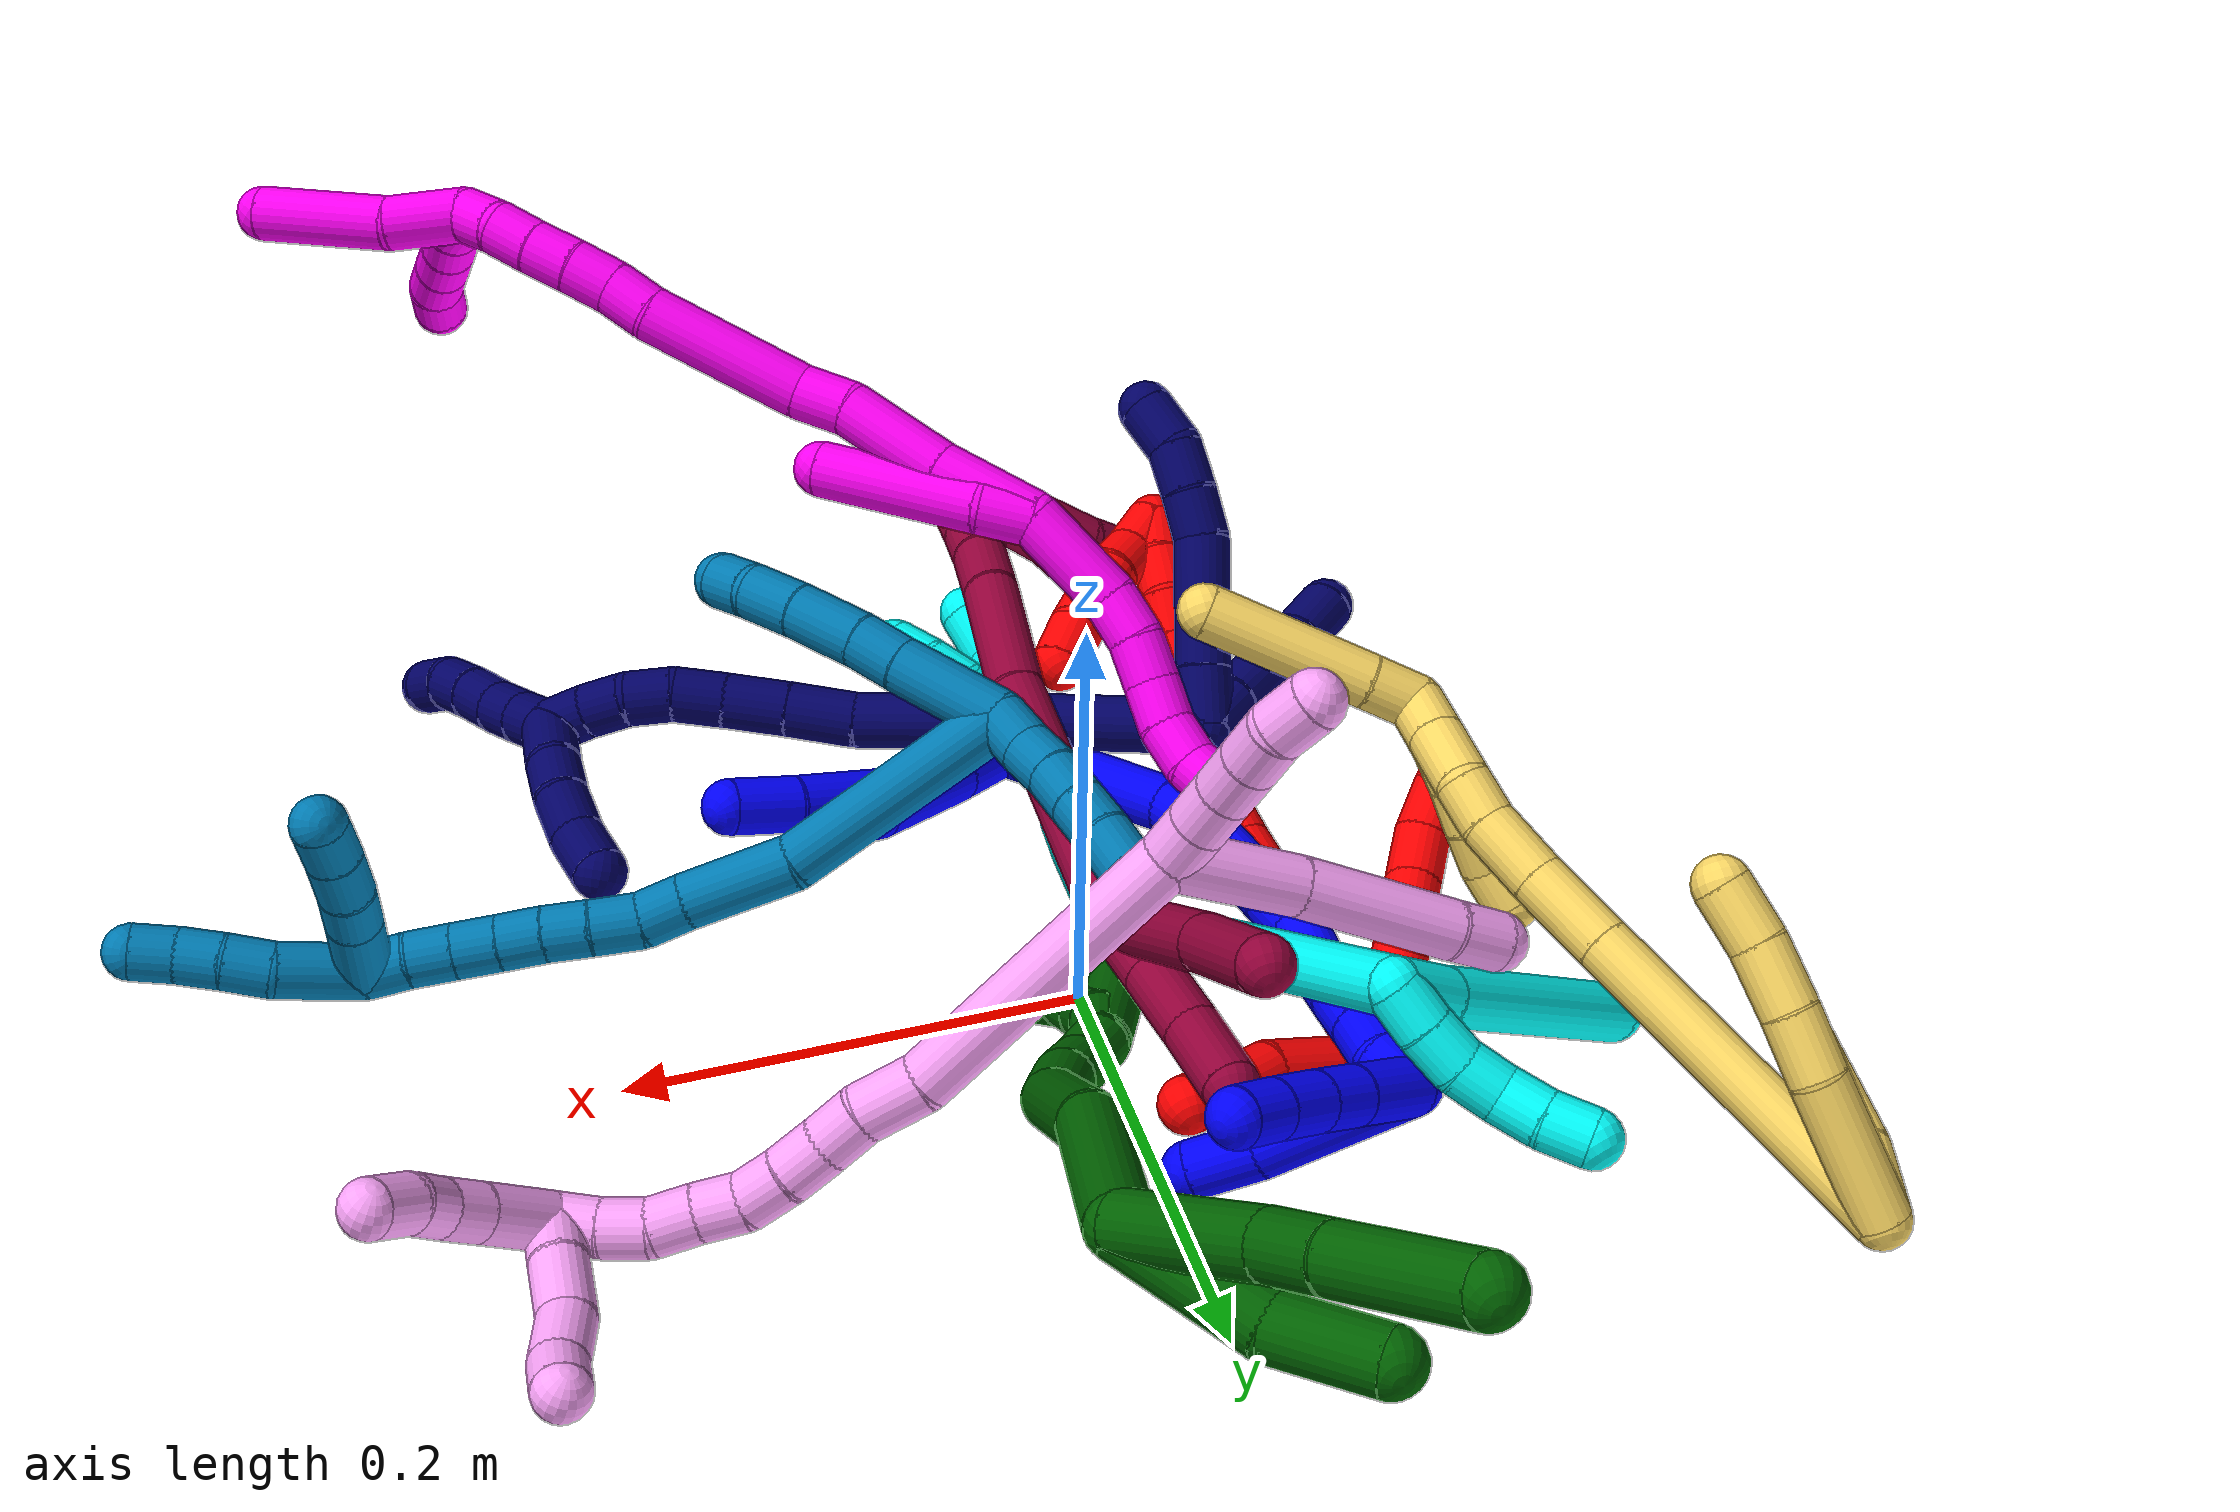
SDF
<sdf version="1.7">
 <world name="default">
  <plugin name="TubeGeneratorPlugin" filename="libtube_generator_plugin.so"/>
  <model name="photoneo_s_sensor">
   <static>1</static>
   <pose>0 0 2 1.57079 1.57079 3.14159</pose>
   <link name="link">
    <inertial><mass>0.1</mass></inertial>
    <sensor name="sensor" type="depth">
     <update_rate>30</update_rate>
     <camera>
      <horizontal_fov>1.22</horizontal_fov>
      <image><width>1920</width><height>1200</height><format>B8G8R8</format></image>
      <clip><near>0.1</near><far>4</far></clip>
      <depth_camera><output>points</output></depth_camera>
     </camera>
     <plugin name="camera_plugin" filename="libgazebo_ros_depth_camera.so">
      <baseline>0.2</baseline>
      <alwaysOn>1</alwaysOn>
      <updateRate>0.0</updateRate>
      <cameraName>camera_ir</cameraName>
      <imageTopicName>/camera/color/image_raw</imageTopicName>
      <cameraInfoTopicName>/camera/color/camera_info</cameraInfoTopicName>
      <depthImageTopicName>/camera/depth/image_raw</depthImageTopicName>
      <depthImageCameraInfoTopicName>/camera/depth/camera_info</depthImageCameraInfoTopicName>
      <pointCloudTopicName>/camera/depth/points</pointCloudTopicName>
      <frameName>fr_optical</frameName>
      <pointCloudCutoff>0.1</pointCloudCutoff>
      <pointCloudCutoffMax>2.0</pointCloudCutoffMax>
      <distortionK1>0</distortionK1>
      <distortionK2>0</distortionK2>
      <distortionK3>0</distortionK3>
      <distortionT1>0</distortionT1>
      <distortionT2>0</distortionT2>
      <CxPrime>0</CxPrime>
      <Cx>0</Cx>
      <Cy>0</Cy>
      <focalLength>0</focalLength>
      <hackBaseline>0</hackBaseline>
     </plugin>
    </sensor>
   </link>
  </model>
  <gravity>0 0 -9.8</gravity>
  <magnetic_field>6e-06 2.3e-05 -4.2e-05</magnetic_field>
  <atmosphere type="adiabatic"/>
  <physics name="default_physics" default="0" type="ode">
   <max_step_size>0.003</max_step_size>
   <real_time_factor>1</real_time_factor>
   <real_time_update_rate>1000</real_time_update_rate>
   <max_contacts>10000</max_contacts>
   <ode>
    <solver>
     <type>quick</type>
     <iters>100</iters>
     <sor>1.3</sor>
     <use_dynamic_moi_rescaling>0</use_dynamic_moi_rescaling>
    </solver>
    <constraints>
     <contact_max_correcting_vel>0</contact_max_correcting_vel>
     <contact_surface_layer>0.001</contact_surface_layer>
     <cfm>0</cfm>
     <erp>0.2</erp>
    </constraints>
   </ode>
  </physics>
  <scene><ambient>0.4 0.4 0.4 1</ambient><background>0.7 0.7 0.7 1</background><shadows>0</shadows></scene>
  <audio><device>default</device></audio>
  <spherical_coordinates>
   <surface_model>EARTH_WGS84</surface_model>
   <latitude_deg>0</latitude_deg>
   <longitude_deg>0</longitude_deg>
   <elevation>0</elevation>
   <heading_deg>0</heading_deg>
  </spherical_coordinates>
  <model name="bin">
   <static>1</static>
   <link name="bottom">
    <collision name="collision-bottom">
     <pose>0 0 -0.01 0 -0 0</pose>
     <geometry><box><size>0.8 0.6 0.02</size></box></geometry>
     <surface>
      <friction><ode><mu>100</mu><mu2>100</mu2></ode></friction>
      <contact><collide_bitmask>65535</collide_bitmask></contact>
     </surface>
    </collision>
   </link>
   <link name="west_wall">
    <collision name="collision-west_wall">
     <pose>-0.41 0 0.1 0 -0 0</pose>
     <geometry><box><size>0.02 0.6 0.2</size></box></geometry>
     <surface>
      <friction><ode><mu>100</mu><mu2>100</mu2></ode></friction>
      <contact><collide_bitmask>65535</collide_bitmask></contact>
     </surface>
    </collision>
   </link>
   <link name="east_wall">
    <collision name="collision-east_wall">
     <pose>0.41 0 0.1 0 -0 0</pose>
     <geometry><box><size>0.02 0.6 0.2</size></box></geometry>
     <surface>
      <friction><ode><mu>100</mu><mu2>100</mu2></ode></friction>
      <contact><collide_bitmask>65535</collide_bitmask></contact>
     </surface>
    </collision>
   </link>
   <link name="south_wall">
    <collision name="collision-south_wall">
     <pose>0 -0.31 0.1 0 -0 0</pose>
     <geometry><box><size>0.8 0.02 0.2</size></box></geometry>
     <surface>
      <friction><ode><mu>100</mu><mu2>100</mu2></ode></friction>
      <contact><collide_bitmask>65535</collide_bitmask></contact>
     </surface>
    </collision>
   </link>
   <link name="north_wall">
    <collision name="collision-north_wall">
     <pose>0 0.31 0.1 0 -0 0</pose>
     <geometry><box><size>0.8 0.02 0.2</size></box></geometry>
     <surface>
      <friction><ode><mu>100</mu><mu2>100</mu2></ode></friction>
      <contact><collide_bitmask>65535</collide_bitmask></contact>
     </surface>
    </collision>
   </link>
  </model>
  <model name="1">
   <static>0</static>
   <link name="1">
    <collision name="collision-cylinder-e_1_2_8">
     <pose>-0.002496 -0.003283 -0.0257 3.01455 -0.096046 -1.29409</pose>
     <geometry><cylinder><radius>0.0125</radius><length>0.052058</length></cylinder></geometry>
     <surface>
      <friction><ode><mu>1.16</mu><mu2>1.16</mu2><slip1>0</slip1><slip2>0</slip2></ode></friction>
      <contact><ode><kp>1e+06</kp><kd>1</kd><max_vel>0</max_vel><min_depth>0.001</min_depth></ode></contact>
     </surface>
    </collision>
    <visual name="visual-cylinder-e_1_2_8">
     <pose>-0.002496 -0.003283 -0.0257 3.01455 -0.096046 -1.29409</pose>
     <geometry><cylinder><radius>0.0125</radius><length>0.052058</length></cylinder></geometry>
     <material><ambient>0 0 1 1</ambient></material>
    </visual>
    <collision name="collision-cylinder-e_2_8_9">
     <pose>-0.002702 -0.008476 -0.064848 3.00044 0.167065 1.73922</pose>
     <geometry><cylinder><radius>0.0125</radius><length>0.027549</length></cylinder></geometry>
     <surface>
      <friction><ode><mu>1.16</mu><mu2>1.16</mu2><slip1>0</slip1><slip2>0</slip2></ode></friction>
      <contact><ode><kp>1e+06</kp><kd>1</kd><max_vel>0</max_vel><min_depth>0.001</min_depth></ode></contact>
     </surface>
    </collision>
    <visual name="visual-cylinder-e_2_8_9">
     <pose>-0.002702 -0.008476 -0.064848 3.00044 0.167065 1.73922</pose>
     <geometry><cylinder><radius>0.0125</radius><length>0.027549</length></cylinder></geometry>
     <material><ambient>0 0 1 1</ambient></material>
    </visual>
    <collision name="collision-cylinder-e_3_9_10">
     <pose>0.000653 -0.018577 -0.096829 2.7255 0.052465 0.24732</pose>
     <geometry><cylinder><radius>0.0125</radius><length>0.040582</length></cylinder></geometry>
     <surface>
      <friction><ode><mu>1.16</mu><mu2>1.16</mu2><slip1>0</slip1><slip2>0</slip2></ode></friction>
      <contact><ode><kp>1e+06</kp><kd>1</kd><max_vel>0</max_vel><min_depth>0.001</min_depth></ode></contact>
     </surface>
    </collision>
    <visual name="visual-cylinder-e_3_9_10">
     <pose>0.000653 -0.018577 -0.096829 2.7255 0.052465 0.24732</pose>
     <geometry><cylinder><radius>0.0125</radius><length>0.040582</length></cylinder></geometry>
     <material><ambient>0 0 1 1</ambient></material>
    </visual>
    <collision name="collision-cylinder-e_4_10_6">
     <pose>0.001737 -0.034445 -0.12814 2.6005 0.00135 0.004867</pose>
     <geometry><cylinder><radius>0.0125</radius><length>0.029812</length></cylinder></geometry>
     <surface>
      <friction><ode><mu>1.16</mu><mu2>1.16</mu2><slip1>0</slip1><slip2>0</slip2></ode></friction>
      <contact><ode><kp>1e+06</kp><kd>1</kd><max_vel>0</max_vel><min_depth>0.001</min_depth></ode></contact>
     </surface>
    </collision>
    <visual name="visual-cylinder-e_4_10_6">
     <pose>0.001737 -0.034445 -0.12814 2.6005 0.00135 0.004867</pose>
     <geometry><cylinder><radius>0.0125</radius><length>0.029812</length></cylinder></geometry>
     <material><ambient>0 0 1 1</ambient></material>
    </visual>
    <collision name="collision-cylinder-e_1_2_11">
     <pose>0.000445 0.000313 -0.018773 -3.1249 0.023691 -1.91379</pose>
     <geometry><cylinder><radius>0.0125</radius><length>0.037562</length></cylinder></geometry>
     <surface>
      <friction><ode><mu>1.16</mu><mu2>1.16</mu2><slip1>0</slip1><slip2>0</slip2></ode></friction>
      <contact><ode><kp>1e+06</kp><kd>1</kd><max_vel>0</max_vel><min_depth>0.001</min_depth></ode></contact>
     </surface>
    </collision>
    <visual name="visual-cylinder-e_1_2_11">
     <pose>0.000445 0.000313 -0.018773 -3.1249 0.023691 -1.91379</pose>
     <geometry><cylinder><radius>0.0125</radius><length>0.037562</length></cylinder></geometry>
     <material><ambient>0 0 1 1</ambient></material>
    </visual>
    <collision name="collision-cylinder-e_2_11_5">
     <pose>0.005136 0.002327 -0.068428 -3.08659 0.136452 -2.37612</pose>
     <geometry><cylinder><radius>0.0125</radius><length>0.062438</length></cylinder></geometry>
     <surface>
      <friction><ode><mu>1.16</mu><mu2>1.16</mu2><slip1>0</slip1><slip2>0</slip2></ode></friction>
      <contact><ode><kp>1e+06</kp><kd>1</kd><max_vel>0</max_vel><min_depth>0.001</min_depth></ode></contact>
     </surface>
    </collision>
    <visual name="visual-cylinder-e_2_11_5">
     <pose>0.005136 0.002327 -0.068428 -3.08659 0.136452 -2.37612</pose>
     <geometry><cylinder><radius>0.0125</radius><length>0.062438</length></cylinder></geometry>
     <material><ambient>0 0 1 1</ambient></material>
    </visual>
    <collision name="collision-cylinder-e_1_2_12">
     <pose>0.01322 0.046098 -0.003635 -1.64949 0.278459 -0.300953</pose>
     <geometry><cylinder><radius>0.0125</radius><length>0.096188</length></cylinder></geometry>
     <surface>
      <friction><ode><mu>1.16</mu><mu2>1.16</mu2><slip1>0</slip1><slip2>0</slip2></ode></friction>
      <contact><ode><kp>1e+06</kp><kd>1</kd><max_vel>0</max_vel><min_depth>0.001</min_depth></ode></contact>
     </surface>
    </collision>
    <visual name="visual-cylinder-e_1_2_12">
     <pose>0.01322 0.046098 -0.003635 -1.64949 0.278459 -0.300953</pose>
     <geometry><cylinder><radius>0.0125</radius><length>0.096188</length></cylinder></geometry>
     <material><ambient>0 0 1 1</ambient></material>
    </visual>
    <collision name="collision-cylinder-e_2_12_13">
     <pose>0.028265 0.103783 -0.010244 -1.82198 0.151411 -0.194925</pose>
     <geometry><cylinder><radius>0.0125</radius><length>0.024202</length></cylinder></geometry>
     <surface>
      <friction><ode><mu>1.16</mu><mu2>1.16</mu2><slip1>0</slip1><slip2>0</slip2></ode></friction>
      <contact><ode><kp>1e+06</kp><kd>1</kd><max_vel>0</max_vel><min_depth>0.001</min_depth></ode></contact>
     </surface>
    </collision>
    <visual name="visual-cylinder-e_2_12_13">
     <pose>0.028265 0.103783 -0.010244 -1.82198 0.151411 -0.194925</pose>
     <geometry><cylinder><radius>0.0125</radius><length>0.024202</length></cylinder></geometry>
     <material><ambient>0 0 1 1</ambient></material>
    </visual>
    <collision name="collision-cylinder-e_3_13_14">
     <pose>0.030612 0.13062 -0.019393 -1.95558 0.031751 -0.047109</pose>
     <geometry><cylinder><radius>0.0125</radius><length>0.032923</length></cylinder></geometry>
     <surface>
      <friction><ode><mu>1.16</mu><mu2>1.16</mu2><slip1>0</slip1><slip2>0</slip2></ode></friction>
      <contact><ode><kp>1e+06</kp><kd>1</kd><max_vel>0</max_vel><min_depth>0.001</min_depth></ode></contact>
     </surface>
    </collision>
    <visual name="visual-cylinder-e_3_13_14">
     <pose>0.030612 0.13062 -0.019393 -1.95558 0.031751 -0.047109</pose>
     <geometry><cylinder><radius>0.0125</radius><length>0.032923</length></cylinder></geometry>
     <material><ambient>0 0 1 1</ambient></material>
    </visual>
    <collision name="collision-cylinder-e_4_14_15">
     <pose>0.031522 0.155193 -0.02977 -1.99418 0.037774 -0.058445</pose>
     <geometry><cylinder><radius>0.0125</radius><length>0.020466</length></cylinder></geometry>
     <surface>
      <friction><ode><mu>1.16</mu><mu2>1.16</mu2><slip1>0</slip1><slip2>0</slip2></ode></friction>
      <contact><ode><kp>1e+06</kp><kd>1</kd><max_vel>0</max_vel><min_depth>0.001</min_depth></ode></contact>
     </surface>
    </collision>
    <visual name="visual-cylinder-e_4_14_15">
     <pose>0.031522 0.155193 -0.02977 -1.99418 0.037774 -0.058445</pose>
     <geometry><cylinder><radius>0.0125</radius><length>0.020466</length></cylinder></geometry>
     <material><ambient>0 0 1 1</ambient></material>
    </visual>
    <collision name="collision-cylinder-e_5_15_16">
     <pose>0.032545 0.173824 -0.037627 -1.94505 0.063569 -0.093229</pose>
     <geometry><cylinder><radius>0.0125</radius><length>0.020042</length></cylinder></geometry>
     <surface>
      <friction><ode><mu>1.16</mu><mu2>1.16</mu2><slip1>0</slip1><slip2>0</slip2></ode></friction>
      <contact><ode><kp>1e+06</kp><kd>1</kd><max_vel>0</max_vel><min_depth>0.001</min_depth></ode></contact>
     </surface>
    </collision>
    <visual name="visual-cylinder-e_5_15_16">
     <pose>0.032545 0.173824 -0.037627 -1.94505 0.063569 -0.093229</pose>
     <geometry><cylinder><radius>0.0125</radius><length>0.020042</length></cylinder></geometry>
     <material><ambient>0 0 1 1</ambient></material>
    </visual>
    <collision name="collision-cylinder-e_6_16_17">
     <pose>0.031242 0.192711 -0.046786 -2.09225 -0.173802 0.298805</pose>
     <geometry><cylinder><radius>0.0125</radius><length>0.022431</length></cylinder></geometry>
     <surface>
      <friction><ode><mu>1.16</mu><mu2>1.16</mu2><slip1>0</slip1><slip2>0</slip2></ode></friction>
      <contact><ode><kp>1e+06</kp><kd>1</kd><max_vel>0</max_vel><min_depth>0.001</min_depth></ode></contact>
     </surface>
    </collision>
    <visual name="visual-cylinder-e_6_16_17">
     <pose>0.031242 0.192711 -0.046786 -2.09225 -0.173802 0.298805</pose>
     <geometry><cylinder><radius>0.0125</radius><length>0.022431</length></cylinder></geometry>
     <material><ambient>0 0 1 1</ambient></material>
    </visual>
    <collision name="collision-cylinder-e_7_17_18">
     <pose>0.030065 0.211417 -0.058378 -2.15913 0.069446 -0.129684</pose>
     <geometry><cylinder><radius>0.0125</radius><length>0.021997</length></cylinder></geometry>
     <surface>
      <friction><ode><mu>1.16</mu><mu2>1.16</mu2><slip1>0</slip1><slip2>0</slip2></ode></friction>
      <contact><ode><kp>1e+06</kp><kd>1</kd><max_vel>0</max_vel><min_depth>0.001</min_depth></ode></contact>
     </surface>
    </collision>
    <visual name="visual-cylinder-e_7_17_18">
     <pose>0.030065 0.211417 -0.058378 -2.15913 0.069446 -0.129684</pose>
     <geometry><cylinder><radius>0.0125</radius><length>0.021997</length></cylinder></geometry>
     <material><ambient>0 0 1 1</ambient></material>
    </visual>
    <collision name="collision-cylinder-e_8_18_19">
     <pose>0.031607 0.229198 -0.069911 -2.13227 0.076008 -0.137453</pose>
     <geometry><cylinder><radius>0.0125</radius><length>0.020506</length></cylinder></geometry>
     <surface>
      <friction><ode><mu>1.16</mu><mu2>1.16</mu2><slip1>0</slip1><slip2>0</slip2></ode></friction>
      <contact><ode><kp>1e+06</kp><kd>1</kd><max_vel>0</max_vel><min_depth>0.001</min_depth></ode></contact>
     </surface>
    </collision>
    <visual name="visual-cylinder-e_8_18_19">
     <pose>0.031607 0.229198 -0.069911 -2.13227 0.076008 -0.137453</pose>
     <geometry><cylinder><radius>0.0125</radius><length>0.020506</length></cylinder></geometry>
     <material><ambient>0 0 1 1</ambient></material>
    </visual>
    <collision name="collision-cylinder-e_9_19_20">
     <pose>0.033085 0.246583 -0.081235 -2.16354 0.066352 -0.124574</pose>
     <geometry><cylinder><radius>0.0125</radius><length>0.0211</length></cylinder></geometry>
     <surface>
      <friction><ode><mu>1.16</mu><mu2>1.16</mu2><slip1>0</slip1><slip2>0</slip2></ode></friction>
      <contact><ode><kp>1e+06</kp><kd>1</kd><max_vel>0</max_vel><min_depth>0.001</min_depth></ode></contact>
     </surface>
    </collision>
    <visual name="visual-cylinder-e_9_19_20">
     <pose>0.033085 0.246583 -0.081235 -2.16354 0.066352 -0.124574</pose>
     <geometry><cylinder><radius>0.0125</radius><length>0.0211</length></cylinder></geometry>
     <material><ambient>0 0 1 1</ambient></material>
    </visual>
    <collision name="collision-cylinder-e_10_20_1">
     <pose>0.034538 0.264775 -0.090491 -1.91346 0.074824 -0.106085</pose>
     <geometry><cylinder><radius>0.0125</radius><length>0.020145</length></cylinder></geometry>
     <surface>
      <friction><ode><mu>1.16</mu><mu2>1.16</mu2><slip1>0</slip1><slip2>0</slip2></ode></friction>
      <contact><ode><kp>1e+06</kp><kd>1</kd><max_vel>0</max_vel><min_depth>0.001</min_depth></ode></contact>
     </surface>
    </collision>
    <visual name="visual-cylinder-e_10_20_1">
     <pose>0.034538 0.264775 -0.090491 -1.91346 0.074824 -0.106085</pose>
     <geometry><cylinder><radius>0.0125</radius><length>0.020145</length></cylinder></geometry>
     <material><ambient>0 0 1 1</ambient></material>
    </visual>
    <collision name="collision-cylinder-e_1_1_21">
     <pose>0.010533 0.25277 -0.106382 2.09872 -0.783579 -1.24697</pose>
     <geometry><cylinder><radius>0.0125</radius><length>0.070153</length></cylinder></geometry>
     <surface>
      <friction><ode><mu>1.16</mu><mu2>1.16</mu2><slip1>0</slip1><slip2>0</slip2></ode></friction>
      <contact><ode><kp>1e+06</kp><kd>1</kd><max_vel>0</max_vel><min_depth>0.001</min_depth></ode></contact>
     </surface>
    </collision>
    <visual name="visual-cylinder-e_1_1_21">
     <pose>0.010533 0.25277 -0.106382 2.09872 -0.783579 -1.24697</pose>
     <geometry><cylinder><radius>0.0125</radius><length>0.070153</length></cylinder></geometry>
     <material><ambient>0 0 1 1</ambient></material>
    </visual>
    <collision name="collision-cylinder-e_2_21_4">
     <pose>-0.02275 0.221395 -0.126098 2.19899 -0.608058 -1.10375</pose>
     <geometry><cylinder><radius>0.0125</radius><length>0.029847</length></cylinder></geometry>
     <surface>
      <friction><ode><mu>1.16</mu><mu2>1.16</mu2><slip1>0</slip1><slip2>0</slip2></ode></friction>
      <contact><ode><kp>1e+06</kp><kd>1</kd><max_vel>0</max_vel><min_depth>0.001</min_depth></ode></contact>
     </surface>
    </collision>
    <visual name="visual-cylinder-e_2_21_4">
     <pose>-0.02275 0.221395 -0.126098 2.19899 -0.608058 -1.10375</pose>
     <geometry><cylinder><radius>0.0125</radius><length>0.029847</length></cylinder></geometry>
     <material><ambient>0 0 1 1</ambient></material>
    </visual>
    <collision name="collision-cylinder-e_1_1_22">
     <pose>0.038395 0.269789 -0.109925 2.87152 0.18418 1.19399</pose>
     <geometry><cylinder><radius>0.0125</radius><length>0.033901</length></cylinder></geometry>
     <surface>
      <friction><ode><mu>1.16</mu><mu2>1.16</mu2><slip1>0</slip1><slip2>0</slip2></ode></friction>
      <contact><ode><kp>1e+06</kp><kd>1</kd><max_vel>0</max_vel><min_depth>0.001</min_depth></ode></contact>
     </surface>
    </collision>
    <visual name="visual-cylinder-e_1_1_22">
     <pose>0.038395 0.269789 -0.109925 2.87152 0.18418 1.19399</pose>
     <geometry><cylinder><radius>0.0125</radius><length>0.033901</length></cylinder></geometry>
     <material><ambient>0 0 1 1</ambient></material>
    </visual>
    <collision name="collision-cylinder-e_2_22_23">
     <pose>0.043288 0.262369 -0.136051 2.85431 0.168794 1.05849</pose>
     <geometry><cylinder><radius>0.0125</radius><length>0.021296</length></cylinder></geometry>
     <surface>
      <friction><ode><mu>1.16</mu><mu2>1.16</mu2><slip1>0</slip1><slip2>0</slip2></ode></friction>
      <contact><ode><kp>1e+06</kp><kd>1</kd><max_vel>0</max_vel><min_depth>0.001</min_depth></ode></contact>
     </surface>
    </collision>
    <visual name="visual-cylinder-e_2_22_23">
     <pose>0.043288 0.262369 -0.136051 2.85431 0.168794 1.05849</pose>
     <geometry><cylinder><radius>0.0125</radius><length>0.021296</length></cylinder></geometry>
     <material><ambient>0 0 1 1</ambient></material>
    </visual>
    <collision name="collision-cylinder-e_3_23_24">
     <pose>0.047227 0.256512 -0.157635 2.89632 0.179202 1.25974</pose>
     <geometry><cylinder><radius>0.0125</radius><length>0.024131</length></cylinder></geometry>
     <surface>
      <friction><ode><mu>1.16</mu><mu2>1.16</mu2><slip1>0</slip1><slip2>0</slip2></ode></friction>
      <contact><ode><kp>1e+06</kp><kd>1</kd><max_vel>0</max_vel><min_depth>0.001</min_depth></ode></contact>
     </surface>
    </collision>
    <visual name="visual-cylinder-e_3_23_24">
     <pose>0.047227 0.256512 -0.157635 2.89632 0.179202 1.25974</pose>
     <geometry><cylinder><radius>0.0125</radius><length>0.024131</length></cylinder></geometry>
     <material><ambient>0 0 1 1</ambient></material>
    </visual>
    <collision name="collision-cylinder-e_4_24_3">
     <pose>0.050918 0.25121 -0.179082 2.90261 0.149545 1.11566</pose>
     <geometry><cylinder><radius>0.0125</radius><length>0.020672</length></cylinder></geometry>
     <surface>
      <friction><ode><mu>1.16</mu><mu2>1.16</mu2><slip1>0</slip1><slip2>0</slip2></ode></friction>
      <contact><ode><kp>1e+06</kp><kd>1</kd><max_vel>0</max_vel><min_depth>0.001</min_depth></ode></contact>
     </surface>
    </collision>
    <visual name="visual-cylinder-e_4_24_3">
     <pose>0.050918 0.25121 -0.179082 2.90261 0.149545 1.11566</pose>
     <geometry><cylinder><radius>0.0125</radius><length>0.020672</length></cylinder></geometry>
     <material><ambient>0 0 1 1</ambient></material>
    </visual>
    <collision name="collision-sphere-3">
     <pose>0.052458 0.248791 -0.189012 0 -0 0</pose>
     <geometry><sphere><radius>0.0125</radius></sphere></geometry>
     <surface>
      <friction><ode><mu>1.16</mu><mu2>1.16</mu2><slip1>0</slip1><slip2>0</slip2></ode></friction>
      <contact><ode><kp>1e+06</kp><kd>1</kd><max_vel>0</max_vel><min_depth>0.001</min_depth></ode></contact>
     </surface>
    </collision>
    <visual name="visual-sphere-3">
     <pose>0.052458 0.248791 -0.189012 0 -0 0</pose>
     <geometry><sphere><radius>0.0125</radius></sphere></geometry>
     <material><ambient>0 0 1 1</ambient></material>
    </visual>
    <collision name="collision-sphere-24">
     <pose>0.049378 0.25363 -0.169152 0 -0 0</pose>
     <geometry><sphere><radius>0.0125</radius></sphere></geometry>
     <surface>
      <friction><ode><mu>1.16</mu><mu2>1.16</mu2><slip1>0</slip1><slip2>0</slip2></ode></friction>
      <contact><ode><kp>1e+06</kp><kd>1</kd><max_vel>0</max_vel><min_depth>0.001</min_depth></ode></contact>
     </surface>
    </collision>
    <visual name="visual-sphere-24">
     <pose>0.049378 0.25363 -0.169152 0 -0 0</pose>
     <geometry><sphere><radius>0.0125</radius></sphere></geometry>
     <material><ambient>0 0 1 1</ambient></material>
    </visual>
    <collision name="collision-sphere-23">
     <pose>0.045077 0.259395 -0.146118 0 -0 0</pose>
     <geometry><sphere><radius>0.0125</radius></sphere></geometry>
     <surface>
      <friction><ode><mu>1.16</mu><mu2>1.16</mu2><slip1>0</slip1><slip2>0</slip2></ode></friction>
      <contact><ode><kp>1e+06</kp><kd>1</kd><max_vel>0</max_vel><min_depth>0.001</min_depth></ode></contact>
     </surface>
    </collision>
    <visual name="visual-sphere-23">
     <pose>0.045077 0.259395 -0.146118 0 -0 0</pose>
     <geometry><sphere><radius>0.0125</radius></sphere></geometry>
     <material><ambient>0 0 1 1</ambient></material>
    </visual>
    <collision name="collision-sphere-22">
     <pose>0.041499 0.265343 -0.125985 0 -0 0</pose>
     <geometry><sphere><radius>0.0125</radius></sphere></geometry>
     <surface>
      <friction><ode><mu>1.16</mu><mu2>1.16</mu2><slip1>0</slip1><slip2>0</slip2></ode></friction>
      <contact><ode><kp>1e+06</kp><kd>1</kd><max_vel>0</max_vel><min_depth>0.001</min_depth></ode></contact>
     </surface>
    </collision>
    <visual name="visual-sphere-22">
     <pose>0.041499 0.265343 -0.125985 0 -0 0</pose>
     <geometry><sphere><radius>0.0125</radius></sphere></geometry>
     <material><ambient>0 0 1 1</ambient></material>
    </visual>
    <collision name="collision-sphere-4">
     <pose>-0.031276 0.211485 -0.133296 0 -0 0</pose>
     <geometry><sphere><radius>0.0125</radius></sphere></geometry>
     <surface>
      <friction><ode><mu>1.16</mu><mu2>1.16</mu2><slip1>0</slip1><slip2>0</slip2></ode></friction>
      <contact><ode><kp>1e+06</kp><kd>1</kd><max_vel>0</max_vel><min_depth>0.001</min_depth></ode></contact>
     </surface>
    </collision>
    <visual name="visual-sphere-4">
     <pose>-0.031276 0.211485 -0.133296 0 -0 0</pose>
     <geometry><sphere><radius>0.0125</radius></sphere></geometry>
     <material><ambient>0 0 1 1</ambient></material>
    </visual>
    <collision name="collision-sphere-21">
     <pose>-0.014225 0.231305 -0.118899 0 -0 0</pose>
     <geometry><sphere><radius>0.0125</radius></sphere></geometry>
     <surface>
      <friction><ode><mu>1.16</mu><mu2>1.16</mu2><slip1>0</slip1><slip2>0</slip2></ode></friction>
      <contact><ode><kp>1e+06</kp><kd>1</kd><max_vel>0</max_vel><min_depth>0.001</min_depth></ode></contact>
     </surface>
    </collision>
    <visual name="visual-sphere-21">
     <pose>-0.014225 0.231305 -0.118899 0 -0 0</pose>
     <geometry><sphere><radius>0.0125</radius></sphere></geometry>
     <material><ambient>0 0 1 1</ambient></material>
    </visual>
    <collision name="collision-sphere-1">
     <pose>0.035291 0.274235 -0.093865 0 -0 0</pose>
     <geometry><sphere><radius>0.0125</radius></sphere></geometry>
     <surface>
      <friction><ode><mu>1.16</mu><mu2>1.16</mu2><slip1>0</slip1><slip2>0</slip2></ode></friction>
      <contact><ode><kp>1e+06</kp><kd>1</kd><max_vel>0</max_vel><min_depth>0.001</min_depth></ode></contact>
     </surface>
    </collision>
    <visual name="visual-sphere-1">
     <pose>0.035291 0.274235 -0.093865 0 -0 0</pose>
     <geometry><sphere><radius>0.0125</radius></sphere></geometry>
     <material><ambient>0 0 1 1</ambient></material>
    </visual>
    <collision name="collision-sphere-11">
     <pose>0.00089 0.000627 -0.037546 0 -0 0</pose>
     <geometry><sphere><radius>0.0125</radius></sphere></geometry>
     <surface>
      <friction><ode><mu>1.16</mu><mu2>1.16</mu2><slip1>0</slip1><slip2>0</slip2></ode></friction>
      <contact><ode><kp>1e+06</kp><kd>1</kd><max_vel>0</max_vel><min_depth>0.001</min_depth></ode></contact>
     </surface>
    </collision>
    <visual name="visual-sphere-11">
     <pose>0.00089 0.000627 -0.037546 0 -0 0</pose>
     <geometry><sphere><radius>0.0125</radius></sphere></geometry>
     <material><ambient>0 0 1 1</ambient></material>
    </visual>
    <collision name="collision-sphere-6">
     <pose>0.001757 -0.042123 -0.140916 0 -0 0</pose>
     <geometry><sphere><radius>0.0125</radius></sphere></geometry>
     <surface>
      <friction><ode><mu>1.16</mu><mu2>1.16</mu2><slip1>0</slip1><slip2>0</slip2></ode></friction>
      <contact><ode><kp>1e+06</kp><kd>1</kd><max_vel>0</max_vel><min_depth>0.001</min_depth></ode></contact>
     </surface>
    </collision>
    <visual name="visual-sphere-6">
     <pose>0.001757 -0.042123 -0.140916 0 -0 0</pose>
     <geometry><sphere><radius>0.0125</radius></sphere></geometry>
     <material><ambient>0 0 1 1</ambient></material>
    </visual>
    <collision name="collision-sphere-10">
     <pose>0.001717 -0.026767 -0.115363 0 -0 0</pose>
     <geometry><sphere><radius>0.0125</radius></sphere></geometry>
     <surface>
      <friction><ode><mu>1.16</mu><mu2>1.16</mu2><slip1>0</slip1><slip2>0</slip2></ode></friction>
      <contact><ode><kp>1e+06</kp><kd>1</kd><max_vel>0</max_vel><min_depth>0.001</min_depth></ode></contact>
     </surface>
    </collision>
    <visual name="visual-sphere-10">
     <pose>0.001717 -0.026767 -0.115363 0 -0 0</pose>
     <geometry><sphere><radius>0.0125</radius></sphere></geometry>
     <material><ambient>0 0 1 1</ambient></material>
    </visual>
    <collision name="collision-sphere-9">
     <pose>-0.000411 -0.010387 -0.078295 0 -0 0</pose>
     <geometry><sphere><radius>0.0125</radius></sphere></geometry>
     <surface>
      <friction><ode><mu>1.16</mu><mu2>1.16</mu2><slip1>0</slip1><slip2>0</slip2></ode></friction>
      <contact><ode><kp>1e+06</kp><kd>1</kd><max_vel>0</max_vel><min_depth>0.001</min_depth></ode></contact>
     </surface>
    </collision>
    <visual name="visual-sphere-9">
     <pose>-0.000411 -0.010387 -0.078295 0 -0 0</pose>
     <geometry><sphere><radius>0.0125</radius></sphere></geometry>
     <material><ambient>0 0 1 1</ambient></material>
    </visual>
    <collision name="collision-sphere-2">
     <geometry><sphere><radius>0.0125</radius></sphere></geometry>
     <surface>
      <friction><ode><mu>1.16</mu><mu2>1.16</mu2><slip1>0</slip1><slip2>0</slip2></ode></friction>
      <contact><ode><kp>1e+06</kp><kd>1</kd><max_vel>0</max_vel><min_depth>0.001</min_depth></ode></contact>
     </surface>
    </collision>
    <visual name="visual-sphere-2">
     <geometry><sphere><radius>0.0125</radius></sphere></geometry>
     <material><ambient>0 0 1 1</ambient></material>
    </visual>
    <collision name="collision-sphere-19">
     <pose>0.032386 0.237852 -0.075354 0 -0 0</pose>
     <geometry><sphere><radius>0.0125</radius></sphere></geometry>
     <surface>
      <friction><ode><mu>1.16</mu><mu2>1.16</mu2><slip1>0</slip1><slip2>0</slip2></ode></friction>
      <contact><ode><kp>1e+06</kp><kd>1</kd><max_vel>0</max_vel><min_depth>0.001</min_depth></ode></contact>
     </surface>
    </collision>
    <visual name="visual-sphere-19">
     <pose>0.032386 0.237852 -0.075354 0 -0 0</pose>
     <geometry><sphere><radius>0.0125</radius></sphere></geometry>
     <material><ambient>0 0 1 1</ambient></material>
    </visual>
    <collision name="collision-sphere-8">
     <pose>-0.004992 -0.006566 -0.0514 0 -0 0</pose>
     <geometry><sphere><radius>0.0125</radius></sphere></geometry>
     <surface>
      <friction><ode><mu>1.16</mu><mu2>1.16</mu2><slip1>0</slip1><slip2>0</slip2></ode></friction>
      <contact><ode><kp>1e+06</kp><kd>1</kd><max_vel>0</max_vel><min_depth>0.001</min_depth></ode></contact>
     </surface>
    </collision>
    <visual name="visual-sphere-8">
     <pose>-0.004992 -0.006566 -0.0514 0 -0 0</pose>
     <geometry><sphere><radius>0.0125</radius></sphere></geometry>
     <material><ambient>0 0 1 1</ambient></material>
    </visual>
    <collision name="collision-sphere-5">
     <pose>0.009383 0.004028 -0.09931 0 -0 0</pose>
     <geometry><sphere><radius>0.0125</radius></sphere></geometry>
     <surface>
      <friction><ode><mu>1.16</mu><mu2>1.16</mu2><slip1>0</slip1><slip2>0</slip2></ode></friction>
      <contact><ode><kp>1e+06</kp><kd>1</kd><max_vel>0</max_vel><min_depth>0.001</min_depth></ode></contact>
     </surface>
    </collision>
    <visual name="visual-sphere-5">
     <pose>0.009383 0.004028 -0.09931 0 -0 0</pose>
     <geometry><sphere><radius>0.0125</radius></sphere></geometry>
     <material><ambient>0 0 1 1</ambient></material>
    </visual>
    <collision name="collision-sphere-12">
     <pose>0.02644 0.092196 -0.007271 0 -0 0</pose>
     <geometry><sphere><radius>0.0125</radius></sphere></geometry>
     <surface>
      <friction><ode><mu>1.16</mu><mu2>1.16</mu2><slip1>0</slip1><slip2>0</slip2></ode></friction>
      <contact><ode><kp>1e+06</kp><kd>1</kd><max_vel>0</max_vel><min_depth>0.001</min_depth></ode></contact>
     </surface>
    </collision>
    <visual name="visual-sphere-12">
     <pose>0.02644 0.092196 -0.007271 0 -0 0</pose>
     <geometry><sphere><radius>0.0125</radius></sphere></geometry>
     <material><ambient>0 0 1 1</ambient></material>
    </visual>
    <collision name="collision-sphere-13">
     <pose>0.03009 0.11537 -0.013217 0 -0 0</pose>
     <geometry><sphere><radius>0.0125</radius></sphere></geometry>
     <surface>
      <friction><ode><mu>1.16</mu><mu2>1.16</mu2><slip1>0</slip1><slip2>0</slip2></ode></friction>
      <contact><ode><kp>1e+06</kp><kd>1</kd><max_vel>0</max_vel><min_depth>0.001</min_depth></ode></contact>
     </surface>
    </collision>
    <visual name="visual-sphere-13">
     <pose>0.03009 0.11537 -0.013217 0 -0 0</pose>
     <geometry><sphere><radius>0.0125</radius></sphere></geometry>
     <material><ambient>0 0 1 1</ambient></material>
    </visual>
    <collision name="collision-sphere-14">
     <pose>0.031135 0.14587 -0.025569 0 -0 0</pose>
     <geometry><sphere><radius>0.0125</radius></sphere></geometry>
     <surface>
      <friction><ode><mu>1.16</mu><mu2>1.16</mu2><slip1>0</slip1><slip2>0</slip2></ode></friction>
      <contact><ode><kp>1e+06</kp><kd>1</kd><max_vel>0</max_vel><min_depth>0.001</min_depth></ode></contact>
     </surface>
    </collision>
    <visual name="visual-sphere-14">
     <pose>0.031135 0.14587 -0.025569 0 -0 0</pose>
     <geometry><sphere><radius>0.0125</radius></sphere></geometry>
     <material><ambient>0 0 1 1</ambient></material>
    </visual>
    <collision name="collision-sphere-15">
     <pose>0.031908 0.164516 -0.033971 0 -0 0</pose>
     <geometry><sphere><radius>0.0125</radius></sphere></geometry>
     <surface>
      <friction><ode><mu>1.16</mu><mu2>1.16</mu2><slip1>0</slip1><slip2>0</slip2></ode></friction>
      <contact><ode><kp>1e+06</kp><kd>1</kd><max_vel>0</max_vel><min_depth>0.001</min_depth></ode></contact>
     </surface>
    </collision>
    <visual name="visual-sphere-15">
     <pose>0.031908 0.164516 -0.033971 0 -0 0</pose>
     <geometry><sphere><radius>0.0125</radius></sphere></geometry>
     <material><ambient>0 0 1 1</ambient></material>
    </visual>
    <collision name="collision-sphere-16">
     <pose>0.033181 0.183133 -0.041283 0 -0 0</pose>
     <geometry><sphere><radius>0.0125</radius></sphere></geometry>
     <surface>
      <friction><ode><mu>1.16</mu><mu2>1.16</mu2><slip1>0</slip1><slip2>0</slip2></ode></friction>
      <contact><ode><kp>1e+06</kp><kd>1</kd><max_vel>0</max_vel><min_depth>0.001</min_depth></ode></contact>
     </surface>
    </collision>
    <visual name="visual-sphere-16">
     <pose>0.033181 0.183133 -0.041283 0 -0 0</pose>
     <geometry><sphere><radius>0.0125</radius></sphere></geometry>
     <material><ambient>0 0 1 1</ambient></material>
    </visual>
    <collision name="collision-sphere-17">
     <pose>0.029302 0.20229 -0.052289 0 -0 0</pose>
     <geometry><sphere><radius>0.0125</radius></sphere></geometry>
     <surface>
      <friction><ode><mu>1.16</mu><mu2>1.16</mu2><slip1>0</slip1><slip2>0</slip2></ode></friction>
      <contact><ode><kp>1e+06</kp><kd>1</kd><max_vel>0</max_vel><min_depth>0.001</min_depth></ode></contact>
     </surface>
    </collision>
    <visual name="visual-sphere-17">
     <pose>0.029302 0.20229 -0.052289 0 -0 0</pose>
     <geometry><sphere><radius>0.0125</radius></sphere></geometry>
     <material><ambient>0 0 1 1</ambient></material>
    </visual>
    <collision name="collision-sphere-18">
     <pose>0.030829 0.220544 -0.064468 0 -0 0</pose>
     <geometry><sphere><radius>0.0125</radius></sphere></geometry>
     <surface>
      <friction><ode><mu>1.16</mu><mu2>1.16</mu2><slip1>0</slip1><slip2>0</slip2></ode></friction>
      <contact><ode><kp>1e+06</kp><kd>1</kd><max_vel>0</max_vel><min_depth>0.001</min_depth></ode></contact>
     </surface>
    </collision>
    <visual name="visual-sphere-18">
     <pose>0.030829 0.220544 -0.064468 0 -0 0</pose>
     <geometry><sphere><radius>0.0125</radius></sphere></geometry>
     <material><ambient>0 0 1 1</ambient></material>
    </visual>
    <collision name="collision-sphere-20">
     <pose>0.033785 0.255314 -0.087116 0 -0 0</pose>
     <geometry><sphere><radius>0.0125</radius></sphere></geometry>
     <surface>
      <friction><ode><mu>1.16</mu><mu2>1.16</mu2><slip1>0</slip1><slip2>0</slip2></ode></friction>
      <contact><ode><kp>1e+06</kp><kd>1</kd><max_vel>0</max_vel><min_depth>0.001</min_depth></ode></contact>
     </surface>
    </collision>
    <visual name="visual-sphere-20">
     <pose>0.033785 0.255314 -0.087116 0 -0 0</pose>
     <geometry><sphere><radius>0.0125</radius></sphere></geometry>
     <material><ambient>0 0 1 1</ambient></material>
    </visual>
    <inertial>
     <pose>0.016469 0.120727 -0.068149 0 -0 0</pose>
     <mass>0.75</mass>
     <inertia><ixx>2.8e-05</ixx><ixy>0</ixy><ixz>0</ixz><iyy>-4.6e-05</iyy><iyz>0</iyz><izz>-0.0001</izz></inertia>
    </inertial>
   </link>
   <pose>-0.005127 -0.132013 0.032965 -2.73665 -1.33992 -2.93916</pose>
  </model>
  <model name="2">
   <static>0</static>
   <link name="2">
    <collision name="collision-cylinder-e_1_2_8">
     <pose>0.005205 0.014963 0.02638 -0.515945 0.169959 -0.044945</pose>
     <geometry><cylinder><radius>0.0125</radius><length>0.061543</length></cylinder></geometry>
     <surface>
      <friction><ode><mu>1.16</mu><mu2>1.16</mu2><slip1>0</slip1><slip2>0</slip2></ode></friction>
      <contact><ode><kp>1e+06</kp><kd>1</kd><max_vel>0</max_vel><min_depth>0.001</min_depth></ode></contact>
     </surface>
    </collision>
    <visual name="visual-cylinder-e_1_2_8">
     <pose>0.005205 0.014963 0.02638 -0.515945 0.169959 -0.044945</pose>
     <geometry><cylinder><radius>0.0125</radius><length>0.061543</length></cylinder></geometry>
     <material><ambient>1 0 0 1</ambient></material>
    </visual>
    <collision name="collision-cylinder-e_2_8_9">
     <pose>0.013946 0.039267 0.069373 -0.512261 0.183496 -0.04818</pose>
     <geometry><cylinder><radius>0.0125</radius><length>0.038768</length></cylinder></geometry>
     <surface>
      <friction><ode><mu>1.16</mu><mu2>1.16</mu2><slip1>0</slip1><slip2>0</slip2></ode></friction>
      <contact><ode><kp>1e+06</kp><kd>1</kd><max_vel>0</max_vel><min_depth>0.001</min_depth></ode></contact>
     </surface>
    </collision>
    <visual name="visual-cylinder-e_2_8_9">
     <pose>0.013946 0.039267 0.069373 -0.512261 0.183496 -0.04818</pose>
     <geometry><cylinder><radius>0.0125</radius><length>0.038768</length></cylinder></geometry>
     <material><ambient>1 0 0 1</ambient></material>
    </visual>
    <collision name="collision-cylinder-e_3_9_10">
     <pose>0.021523 0.054369 0.096964 -0.483182 0.31498 -0.078221</pose>
     <geometry><cylinder><radius>0.0125</radius><length>0.026079</length></cylinder></geometry>
     <surface>
      <friction><ode><mu>1.16</mu><mu2>1.16</mu2><slip1>0</slip1><slip2>0</slip2></ode></friction>
      <contact><ode><kp>1e+06</kp><kd>1</kd><max_vel>0</max_vel><min_depth>0.001</min_depth></ode></contact>
     </surface>
    </collision>
    <visual name="visual-cylinder-e_3_9_10">
     <pose>0.021523 0.054369 0.096964 -0.483182 0.31498 -0.078221</pose>
     <geometry><cylinder><radius>0.0125</radius><length>0.026079</length></cylinder></geometry>
     <material><ambient>1 0 0 1</ambient></material>
    </visual>
    <collision name="collision-cylinder-e_4_10_6">
     <pose>0.032487 0.065304 0.115982 -0.571922 0.626771 -0.189989</pose>
     <geometry><cylinder><radius>0.0125</radius><length>0.023609</length></cylinder></geometry>
     <surface>
      <friction><ode><mu>1.16</mu><mu2>1.16</mu2><slip1>0</slip1><slip2>0</slip2></ode></friction>
      <contact><ode><kp>1e+06</kp><kd>1</kd><max_vel>0</max_vel><min_depth>0.001</min_depth></ode></contact>
     </surface>
    </collision>
    <visual name="visual-cylinder-e_4_10_6">
     <pose>0.032487 0.065304 0.115982 -0.571922 0.626771 -0.189989</pose>
     <geometry><cylinder><radius>0.0125</radius><length>0.023609</length></cylinder></geometry>
     <material><ambient>1 0 0 1</ambient></material>
    </visual>
    <collision name="collision-cylinder-e_1_2_11">
     <pose>-0.002137 -0.011109 0.001568 1.43059 -0.188231 -0.163649</pose>
     <geometry><cylinder><radius>0.0125</radius><length>0.022841</length></cylinder></geometry>
     <surface>
      <friction><ode><mu>1.16</mu><mu2>1.16</mu2><slip1>0</slip1><slip2>0</slip2></ode></friction>
      <contact><ode><kp>1e+06</kp><kd>1</kd><max_vel>0</max_vel><min_depth>0.001</min_depth></ode></contact>
     </surface>
    </collision>
    <visual name="visual-cylinder-e_1_2_11">
     <pose>-0.002137 -0.011109 0.001568 1.43059 -0.188231 -0.163649</pose>
     <geometry><cylinder><radius>0.0125</radius><length>0.022841</length></cylinder></geometry>
     <material><ambient>1 0 0 1</ambient></material>
    </visual>
    <collision name="collision-cylinder-e_2_11_12">
     <pose>-0.004713 -0.037946 0.00268 1.59977 -0.027877 -0.028697</pose>
     <geometry><cylinder><radius>0.0125</radius><length>0.031482</length></cylinder></geometry>
     <surface>
      <friction><ode><mu>1.16</mu><mu2>1.16</mu2><slip1>0</slip1><slip2>0</slip2></ode></friction>
      <contact><ode><kp>1e+06</kp><kd>1</kd><max_vel>0</max_vel><min_depth>0.001</min_depth></ode></contact>
     </surface>
    </collision>
    <visual name="visual-cylinder-e_2_11_12">
     <pose>-0.004713 -0.037946 0.00268 1.59977 -0.027877 -0.028697</pose>
     <geometry><cylinder><radius>0.0125</radius><length>0.031482</length></cylinder></geometry>
     <material><ambient>1 0 0 1</ambient></material>
    </visual>
    <collision name="collision-cylinder-e_3_12_13">
     <pose>-0.006219 -0.063705 -0.001659 1.94012 -0.098869 -0.144155</pose>
     <geometry><cylinder><radius>0.0125</radius><length>0.021618</length></cylinder></geometry>
     <surface>
      <friction><ode><mu>1.16</mu><mu2>1.16</mu2><slip1>0</slip1><slip2>0</slip2></ode></friction>
      <contact><ode><kp>1e+06</kp><kd>1</kd><max_vel>0</max_vel><min_depth>0.001</min_depth></ode></contact>
     </surface>
    </collision>
    <visual name="visual-cylinder-e_3_12_13">
     <pose>-0.006219 -0.063705 -0.001659 1.94012 -0.098869 -0.144155</pose>
     <geometry><cylinder><radius>0.0125</radius><length>0.021618</length></cylinder></geometry>
     <material><ambient>1 0 0 1</ambient></material>
    </visual>
    <collision name="collision-cylinder-e_4_13_5">
     <pose>-0.008641 -0.085318 -0.008494 1.82039 -0.112958 -0.145263</pose>
     <geometry><cylinder><radius>0.0125</radius><length>0.024059</length></cylinder></geometry>
     <surface>
      <friction><ode><mu>1.16</mu><mu2>1.16</mu2><slip1>0</slip1><slip2>0</slip2></ode></friction>
      <contact><ode><kp>1e+06</kp><kd>1</kd><max_vel>0</max_vel><min_depth>0.001</min_depth></ode></contact>
     </surface>
    </collision>
    <visual name="visual-cylinder-e_4_13_5">
     <pose>-0.008641 -0.085318 -0.008494 1.82039 -0.112958 -0.145263</pose>
     <geometry><cylinder><radius>0.0125</radius><length>0.024059</length></cylinder></geometry>
     <material><ambient>1 0 0 1</ambient></material>
    </visual>
    <collision name="collision-cylinder-e_1_2_14">
     <pose>-0.006566 -0.001356 0.067932 0.019954 -0.096336 -0.000962</pose>
     <geometry><cylinder><radius>0.0125</radius><length>0.136524</length></cylinder></geometry>
     <surface>
      <friction><ode><mu>1.16</mu><mu2>1.16</mu2><slip1>0</slip1><slip2>0</slip2></ode></friction>
      <contact><ode><kp>1e+06</kp><kd>1</kd><max_vel>0</max_vel><min_depth>0.001</min_depth></ode></contact>
     </surface>
    </collision>
    <visual name="visual-cylinder-e_1_2_14">
     <pose>-0.006566 -0.001356 0.067932 0.019954 -0.096336 -0.000962</pose>
     <geometry><cylinder><radius>0.0125</radius><length>0.136524</length></cylinder></geometry>
     <material><ambient>1 0 0 1</ambient></material>
    </visual>
    <collision name="collision-cylinder-e_2_14_15">
     <pose>-0.01212 -0.004514 0.146367 0.16995 0.094647 0.008068</pose>
     <geometry><cylinder><radius>0.0125</radius><length>0.021408</length></cylinder></geometry>
     <surface>
      <friction><ode><mu>1.16</mu><mu2>1.16</mu2><slip1>0</slip1><slip2>0</slip2></ode></friction>
      <contact><ode><kp>1e+06</kp><kd>1</kd><max_vel>0</max_vel><min_depth>0.001</min_depth></ode></contact>
     </surface>
    </collision>
    <visual name="visual-cylinder-e_2_14_15">
     <pose>-0.01212 -0.004514 0.146367 0.16995 0.094647 0.008068</pose>
     <geometry><cylinder><radius>0.0125</radius><length>0.021408</length></cylinder></geometry>
     <material><ambient>1 0 0 1</ambient></material>
    </visual>
    <collision name="collision-cylinder-e_3_15_16">
     <pose>-0.00846 -0.005582 0.167 -0.072361 0.255065 -0.009283</pose>
     <geometry><cylinder><radius>0.0125</radius><length>0.020994</length></cylinder></geometry>
     <surface>
      <friction><ode><mu>1.16</mu><mu2>1.16</mu2><slip1>0</slip1><slip2>0</slip2></ode></friction>
      <contact><ode><kp>1e+06</kp><kd>1</kd><max_vel>0</max_vel><min_depth>0.001</min_depth></ode></contact>
     </surface>
    </collision>
    <visual name="visual-cylinder-e_3_15_16">
     <pose>-0.00846 -0.005582 0.167 -0.072361 0.255065 -0.009283</pose>
     <geometry><cylinder><radius>0.0125</radius><length>0.020994</length></cylinder></geometry>
     <material><ambient>1 0 0 1</ambient></material>
    </visual>
    <collision name="collision-cylinder-e_4_16_17">
     <pose>-0.001912 -0.00618 0.186522 0.140965 0.390023 0.027888</pose>
     <geometry><cylinder><radius>0.0125</radius><length>0.020511</length></cylinder></geometry>
     <surface>
      <friction><ode><mu>1.16</mu><mu2>1.16</mu2><slip1>0</slip1><slip2>0</slip2></ode></friction>
      <contact><ode><kp>1e+06</kp><kd>1</kd><max_vel>0</max_vel><min_depth>0.001</min_depth></ode></contact>
     </surface>
    </collision>
    <visual name="visual-cylinder-e_4_16_17">
     <pose>-0.001912 -0.00618 0.186522 0.140965 0.390023 0.027888</pose>
     <geometry><cylinder><radius>0.0125</radius><length>0.020511</length></cylinder></geometry>
     <material><ambient>1 0 0 1</ambient></material>
    </visual>
    <collision name="collision-cylinder-e_5_17_18">
     <pose>0.005635 -0.008652 0.205206 0.121997 0.371618 0.02296</pose>
     <geometry><cylinder><radius>0.0125</radius><length>0.020095</length></cylinder></geometry>
     <surface>
      <friction><ode><mu>1.16</mu><mu2>1.16</mu2><slip1>0</slip1><slip2>0</slip2></ode></friction>
      <contact><ode><kp>1e+06</kp><kd>1</kd><max_vel>0</max_vel><min_depth>0.001</min_depth></ode></contact>
     </surface>
    </collision>
    <visual name="visual-cylinder-e_5_17_18">
     <pose>0.005635 -0.008652 0.205206 0.121997 0.371618 0.02296</pose>
     <geometry><cylinder><radius>0.0125</radius><length>0.020095</length></cylinder></geometry>
     <material><ambient>1 0 0 1</ambient></material>
    </visual>
    <collision name="collision-cylinder-e_6_18_19">
     <pose>0.013185 -0.010955 0.223831 0.124015 0.393192 0.02473</pose>
     <geometry><cylinder><radius>0.0125</radius><length>0.020366</length></cylinder></geometry>
     <surface>
      <friction><ode><mu>1.16</mu><mu2>1.16</mu2><slip1>0</slip1><slip2>0</slip2></ode></friction>
      <contact><ode><kp>1e+06</kp><kd>1</kd><max_vel>0</max_vel><min_depth>0.001</min_depth></ode></contact>
     </surface>
    </collision>
    <visual name="visual-cylinder-e_6_18_19">
     <pose>0.013185 -0.010955 0.223831 0.124015 0.393192 0.02473</pose>
     <geometry><cylinder><radius>0.0125</radius><length>0.020366</length></cylinder></geometry>
     <material><ambient>1 0 0 1</ambient></material>
    </visual>
    <collision name="collision-cylinder-e_7_19_20">
     <pose>0.021463 -0.012744 0.242168 0.069415 0.451525 0.015949</pose>
     <geometry><cylinder><radius>0.0125</radius><length>0.020059</length></cylinder></geometry>
     <surface>
      <friction><ode><mu>1.16</mu><mu2>1.16</mu2><slip1>0</slip1><slip2>0</slip2></ode></friction>
      <contact><ode><kp>1e+06</kp><kd>1</kd><max_vel>0</max_vel><min_depth>0.001</min_depth></ode></contact>
     </surface>
    </collision>
    <visual name="visual-cylinder-e_7_19_20">
     <pose>0.021463 -0.012744 0.242168 0.069415 0.451525 0.015949</pose>
     <geometry><cylinder><radius>0.0125</radius><length>0.020059</length></cylinder></geometry>
     <material><ambient>1 0 0 1</ambient></material>
    </visual>
    <collision name="collision-cylinder-e_8_20_21">
     <pose>0.028445 -0.013106 0.260832 -0.027314 0.263308 -0.003617</pose>
     <geometry><cylinder><radius>0.0125</radius><length>0.020021</length></cylinder></geometry>
     <surface>
      <friction><ode><mu>1.16</mu><mu2>1.16</mu2><slip1>0</slip1><slip2>0</slip2></ode></friction>
      <contact><ode><kp>1e+06</kp><kd>1</kd><max_vel>0</max_vel><min_depth>0.001</min_depth></ode></contact>
     </surface>
    </collision>
    <visual name="visual-cylinder-e_8_20_21">
     <pose>0.028445 -0.013106 0.260832 -0.027314 0.263308 -0.003617</pose>
     <geometry><cylinder><radius>0.0125</radius><length>0.020021</length></cylinder></geometry>
     <material><ambient>1 0 0 1</ambient></material>
    </visual>
    <collision name="collision-cylinder-e_9_21_1">
     <pose>0.033177 -0.011086 0.280118 -0.180528 0.214042 -0.019447</pose>
     <geometry><cylinder><radius>0.0125</radius><length>0.020021</length></cylinder></geometry>
     <surface>
      <friction><ode><mu>1.16</mu><mu2>1.16</mu2><slip1>0</slip1><slip2>0</slip2></ode></friction>
      <contact><ode><kp>1e+06</kp><kd>1</kd><max_vel>0</max_vel><min_depth>0.001</min_depth></ode></contact>
     </surface>
    </collision>
    <visual name="visual-cylinder-e_9_21_1">
     <pose>0.033177 -0.011086 0.280118 -0.180528 0.214042 -0.019447</pose>
     <geometry><cylinder><radius>0.0125</radius><length>0.020021</length></cylinder></geometry>
     <material><ambient>1 0 0 1</ambient></material>
    </visual>
    <collision name="collision-cylinder-e_1_1_22">
     <pose>0.031151 -0.015974 0.283527 2.32269 -0.428184 -0.928894</pose>
     <geometry><cylinder><radius>0.0125</radius><length>0.02</length></cylinder></geometry>
     <surface>
      <friction><ode><mu>1.16</mu><mu2>1.16</mu2><slip1>0</slip1><slip2>0</slip2></ode></friction>
      <contact><ode><kp>1e+06</kp><kd>1</kd><max_vel>0</max_vel><min_depth>0.001</min_depth></ode></contact>
     </surface>
    </collision>
    <visual name="visual-cylinder-e_1_1_22">
     <pose>0.031151 -0.015974 0.283527 2.32269 -0.428184 -0.928894</pose>
     <geometry><cylinder><radius>0.0125</radius><length>0.02</length></cylinder></geometry>
     <material><ambient>1 0 0 1</ambient></material>
    </visual>
    <collision name="collision-cylinder-e_2_22_23">
     <pose>0.026091 -0.030201 0.270857 2.27618 -0.090921 -0.196343</pose>
     <geometry><cylinder><radius>0.0125</radius><length>0.02</length></cylinder></geometry>
     <surface>
      <friction><ode><mu>1.16</mu><mu2>1.16</mu2><slip1>0</slip1><slip2>0</slip2></ode></friction>
      <contact><ode><kp>1e+06</kp><kd>1</kd><max_vel>0</max_vel><min_depth>0.001</min_depth></ode></contact>
     </surface>
    </collision>
    <visual name="visual-cylinder-e_2_22_23">
     <pose>0.026091 -0.030201 0.270857 2.27618 -0.090921 -0.196343</pose>
     <geometry><cylinder><radius>0.0125</radius><length>0.02</length></cylinder></geometry>
     <material><ambient>1 0 0 1</ambient></material>
    </visual>
    <collision name="collision-cylinder-e_3_23_24">
     <pose>0.022926 -0.044457 0.257304 2.3869 -0.227638 -0.561602</pose>
     <geometry><cylinder><radius>0.0125</radius><length>0.02</length></cylinder></geometry>
     <surface>
      <friction><ode><mu>1.16</mu><mu2>1.16</mu2><slip1>0</slip1><slip2>0</slip2></ode></friction>
      <contact><ode><kp>1e+06</kp><kd>1</kd><max_vel>0</max_vel><min_depth>0.001</min_depth></ode></contact>
     </surface>
    </collision>
    <visual name="visual-cylinder-e_3_23_24">
     <pose>0.022926 -0.044457 0.257304 2.3869 -0.227638 -0.561602</pose>
     <geometry><cylinder><radius>0.0125</radius><length>0.02</length></cylinder></geometry>
     <material><ambient>1 0 0 1</ambient></material>
    </visual>
    <collision name="collision-cylinder-e_4_24_25">
     <pose>0.018854 -0.057565 0.24277 2.4284 -0.18255 -0.481858</pose>
     <geometry><cylinder><radius>0.0125</radius><length>0.02</length></cylinder></geometry>
     <surface>
      <friction><ode><mu>1.16</mu><mu2>1.16</mu2><slip1>0</slip1><slip2>0</slip2></ode></friction>
      <contact><ode><kp>1e+06</kp><kd>1</kd><max_vel>0</max_vel><min_depth>0.001</min_depth></ode></contact>
     </surface>
    </collision>
    <visual name="visual-cylinder-e_4_24_25">
     <pose>0.018854 -0.057565 0.24277 2.4284 -0.18255 -0.481858</pose>
     <geometry><cylinder><radius>0.0125</radius><length>0.02</length></cylinder></geometry>
     <material><ambient>1 0 0 1</ambient></material>
    </visual>
    <collision name="collision-cylinder-e_5_25_4">
     <pose>0.012941 -0.06931 0.227916 2.52011 -0.42214 -1.17672</pose>
     <geometry><cylinder><radius>0.0125</radius><length>0.02</length></cylinder></geometry>
     <surface>
      <friction><ode><mu>1.16</mu><mu2>1.16</mu2><slip1>0</slip1><slip2>0</slip2></ode></friction>
      <contact><ode><kp>1e+06</kp><kd>1</kd><max_vel>0</max_vel><min_depth>0.001</min_depth></ode></contact>
     </surface>
    </collision>
    <visual name="visual-cylinder-e_5_25_4">
     <pose>0.012941 -0.06931 0.227916 2.52011 -0.42214 -1.17672</pose>
     <geometry><cylinder><radius>0.0125</radius><length>0.02</length></cylinder></geometry>
     <material><ambient>1 0 0 1</ambient></material>
    </visual>
    <collision name="collision-cylinder-e_1_1_26">
     <pose>0.025262 -0.000736 0.280653 -2.3842 -0.676457 1.44781</pose>
     <geometry><cylinder><radius>0.0125</radius><length>0.032079</length></cylinder></geometry>
     <surface>
      <friction><ode><mu>1.16</mu><mu2>1.16</mu2><slip1>0</slip1><slip2>0</slip2></ode></friction>
      <contact><ode><kp>1e+06</kp><kd>1</kd><max_vel>0</max_vel><min_depth>0.001</min_depth></ode></contact>
     </surface>
    </collision>
    <visual name="visual-cylinder-e_1_1_26">
     <pose>0.025262 -0.000736 0.280653 -2.3842 -0.676457 1.44781</pose>
     <geometry><cylinder><radius>0.0125</radius><length>0.032079</length></cylinder></geometry>
     <material><ambient>1 0 0 1</ambient></material>
    </visual>
    <collision name="collision-cylinder-e_2_26_27">
     <pose>0.007252 0.012475 0.26407 -2.58927 -0.735703 1.87347</pose>
     <geometry><cylinder><radius>0.0125</radius><length>0.023748</length></cylinder></geometry>
     <surface>
      <friction><ode><mu>1.16</mu><mu2>1.16</mu2><slip1>0</slip1><slip2>0</slip2></ode></friction>
      <contact><ode><kp>1e+06</kp><kd>1</kd><max_vel>0</max_vel><min_depth>0.001</min_depth></ode></contact>
     </surface>
    </collision>
    <visual name="visual-cylinder-e_2_26_27">
     <pose>0.007252 0.012475 0.26407 -2.58927 -0.735703 1.87347</pose>
     <geometry><cylinder><radius>0.0125</radius><length>0.023748</length></cylinder></geometry>
     <material><ambient>1 0 0 1</ambient></material>
    </visual>
    <collision name="collision-cylinder-e_3_27_28">
     <pose>-0.008437 0.021693 0.249763 -2.54777 -0.754025 1.82584</pose>
     <geometry><cylinder><radius>0.0125</radius><length>0.022553</length></cylinder></geometry>
     <surface>
      <friction><ode><mu>1.16</mu><mu2>1.16</mu2><slip1>0</slip1><slip2>0</slip2></ode></friction>
      <contact><ode><kp>1e+06</kp><kd>1</kd><max_vel>0</max_vel><min_depth>0.001</min_depth></ode></contact>
     </surface>
    </collision>
    <visual name="visual-cylinder-e_3_27_28">
     <pose>-0.008437 0.021693 0.249763 -2.54777 -0.754025 1.82584</pose>
     <geometry><cylinder><radius>0.0125</radius><length>0.022553</length></cylinder></geometry>
     <material><ambient>1 0 0 1</ambient></material>
    </visual>
    <collision name="collision-cylinder-e_4_28_3">
     <pose>-0.023924 0.027257 0.235495 -3.01299 -0.801723 2.84003</pose>
     <geometry><cylinder><radius>0.0125</radius><length>0.021619</length></cylinder></geometry>
     <surface>
      <friction><ode><mu>1.16</mu><mu2>1.16</mu2><slip1>0</slip1><slip2>0</slip2></ode></friction>
      <contact><ode><kp>1e+06</kp><kd>1</kd><max_vel>0</max_vel><min_depth>0.001</min_depth></ode></contact>
     </surface>
    </collision>
    <visual name="visual-cylinder-e_4_28_3">
     <pose>-0.023924 0.027257 0.235495 -3.01299 -0.801723 2.84003</pose>
     <geometry><cylinder><radius>0.0125</radius><length>0.021619</length></cylinder></geometry>
     <material><ambient>1 0 0 1</ambient></material>
    </visual>
    <collision name="collision-sphere-3">
     <pose>-0.031691 0.028221 0.228039 0 -0 0</pose>
     <geometry><sphere><radius>0.0125</radius></sphere></geometry>
     <surface>
      <friction><ode><mu>1.16</mu><mu2>1.16</mu2><slip1>0</slip1><slip2>0</slip2></ode></friction>
      <contact><ode><kp>1e+06</kp><kd>1</kd><max_vel>0</max_vel><min_depth>0.001</min_depth></ode></contact>
     </surface>
    </collision>
    <visual name="visual-sphere-3">
     <pose>-0.031691 0.028221 0.228039 0 -0 0</pose>
     <geometry><sphere><radius>0.0125</radius></sphere></geometry>
     <material><ambient>1 0 0 1</ambient></material>
    </visual>
    <collision name="collision-sphere-28">
     <pose>-0.016157 0.026293 0.24295 0 -0 0</pose>
     <geometry><sphere><radius>0.0125</radius></sphere></geometry>
     <surface>
      <friction><ode><mu>1.16</mu><mu2>1.16</mu2><slip1>0</slip1><slip2>0</slip2></ode></friction>
      <contact><ode><kp>1e+06</kp><kd>1</kd><max_vel>0</max_vel><min_depth>0.001</min_depth></ode></contact>
     </surface>
    </collision>
    <visual name="visual-sphere-28">
     <pose>-0.016157 0.026293 0.24295 0 -0 0</pose>
     <geometry><sphere><radius>0.0125</radius></sphere></geometry>
     <material><ambient>1 0 0 1</ambient></material>
    </visual>
    <collision name="collision-sphere-27">
     <pose>-0.000717 0.017094 0.256576 0 -0 0</pose>
     <geometry><sphere><radius>0.0125</radius></sphere></geometry>
     <surface>
      <friction><ode><mu>1.16</mu><mu2>1.16</mu2><slip1>0</slip1><slip2>0</slip2></ode></friction>
      <contact><ode><kp>1e+06</kp><kd>1</kd><max_vel>0</max_vel><min_depth>0.001</min_depth></ode></contact>
     </surface>
    </collision>
    <visual name="visual-sphere-27">
     <pose>-0.000717 0.017094 0.256576 0 -0 0</pose>
     <geometry><sphere><radius>0.0125</radius></sphere></geometry>
     <material><ambient>1 0 0 1</ambient></material>
    </visual>
    <collision name="collision-sphere-26">
     <pose>0.015221 0.007857 0.271564 0 -0 0</pose>
     <geometry><sphere><radius>0.0125</radius></sphere></geometry>
     <surface>
      <friction><ode><mu>1.16</mu><mu2>1.16</mu2><slip1>0</slip1><slip2>0</slip2></ode></friction>
      <contact><ode><kp>1e+06</kp><kd>1</kd><max_vel>0</max_vel><min_depth>0.001</min_depth></ode></contact>
     </surface>
    </collision>
    <visual name="visual-sphere-26">
     <pose>0.015221 0.007857 0.271564 0 -0 0</pose>
     <geometry><sphere><radius>0.0125</radius></sphere></geometry>
     <material><ambient>1 0 0 1</ambient></material>
    </visual>
    <collision name="collision-sphere-4">
     <pose>0.008844 -0.074621 0.2205 0 -0 0</pose>
     <geometry><sphere><radius>0.0125</radius></sphere></geometry>
     <surface>
      <friction><ode><mu>1.16</mu><mu2>1.16</mu2><slip1>0</slip1><slip2>0</slip2></ode></friction>
      <contact><ode><kp>1e+06</kp><kd>1</kd><max_vel>0</max_vel><min_depth>0.001</min_depth></ode></contact>
     </surface>
    </collision>
    <visual name="visual-sphere-4">
     <pose>0.008844 -0.074621 0.2205 0 -0 0</pose>
     <geometry><sphere><radius>0.0125</radius></sphere></geometry>
     <material><ambient>1 0 0 1</ambient></material>
    </visual>
    <collision name="collision-sphere-25">
     <pose>0.017039 -0.063998 0.235333 0 -0 0</pose>
     <geometry><sphere><radius>0.0125</radius></sphere></geometry>
     <surface>
      <friction><ode><mu>1.16</mu><mu2>1.16</mu2><slip1>0</slip1><slip2>0</slip2></ode></friction>
      <contact><ode><kp>1e+06</kp><kd>1</kd><max_vel>0</max_vel><min_depth>0.001</min_depth></ode></contact>
     </surface>
    </collision>
    <visual name="visual-sphere-25">
     <pose>0.017039 -0.063998 0.235333 0 -0 0</pose>
     <geometry><sphere><radius>0.0125</radius></sphere></geometry>
     <material><ambient>1 0 0 1</ambient></material>
    </visual>
    <collision name="collision-sphere-24">
     <pose>0.020669 -0.051131 0.250207 0 -0 0</pose>
     <geometry><sphere><radius>0.0125</radius></sphere></geometry>
     <surface>
      <friction><ode><mu>1.16</mu><mu2>1.16</mu2><slip1>0</slip1><slip2>0</slip2></ode></friction>
      <contact><ode><kp>1e+06</kp><kd>1</kd><max_vel>0</max_vel><min_depth>0.001</min_depth></ode></contact>
     </surface>
    </collision>
    <visual name="visual-sphere-24">
     <pose>0.020669 -0.051131 0.250207 0 -0 0</pose>
     <geometry><sphere><radius>0.0125</radius></sphere></geometry>
     <material><ambient>1 0 0 1</ambient></material>
    </visual>
    <collision name="collision-sphere-23">
     <pose>0.025183 -0.037783 0.264401 0 -0 0</pose>
     <geometry><sphere><radius>0.0125</radius></sphere></geometry>
     <surface>
      <friction><ode><mu>1.16</mu><mu2>1.16</mu2><slip1>0</slip1><slip2>0</slip2></ode></friction>
      <contact><ode><kp>1e+06</kp><kd>1</kd><max_vel>0</max_vel><min_depth>0.001</min_depth></ode></contact>
     </surface>
    </collision>
    <visual name="visual-sphere-23">
     <pose>0.025183 -0.037783 0.264401 0 -0 0</pose>
     <geometry><sphere><radius>0.0125</radius></sphere></geometry>
     <material><ambient>1 0 0 1</ambient></material>
    </visual>
    <collision name="collision-sphere-22">
     <pose>0.026999 -0.022619 0.277314 0 -0 0</pose>
     <geometry><sphere><radius>0.0125</radius></sphere></geometry>
     <surface>
      <friction><ode><mu>1.16</mu><mu2>1.16</mu2><slip1>0</slip1><slip2>0</slip2></ode></friction>
      <contact><ode><kp>1e+06</kp><kd>1</kd><max_vel>0</max_vel><min_depth>0.001</min_depth></ode></contact>
     </surface>
    </collision>
    <visual name="visual-sphere-22">
     <pose>0.026999 -0.022619 0.277314 0 -0 0</pose>
     <geometry><sphere><radius>0.0125</radius></sphere></geometry>
     <material><ambient>1 0 0 1</ambient></material>
    </visual>
    <collision name="collision-sphere-1">
     <pose>0.035303 -0.009329 0.289741 0 -0 0</pose>
     <geometry><sphere><radius>0.0125</radius></sphere></geometry>
     <surface>
      <friction><ode><mu>1.16</mu><mu2>1.16</mu2><slip1>0</slip1><slip2>0</slip2></ode></friction>
      <contact><ode><kp>1e+06</kp><kd>1</kd><max_vel>0</max_vel><min_depth>0.001</min_depth></ode></contact>
     </surface>
    </collision>
    <visual name="visual-sphere-1">
     <pose>0.035303 -0.009329 0.289741 0 -0 0</pose>
     <geometry><sphere><radius>0.0125</radius></sphere></geometry>
     <material><ambient>1 0 0 1</ambient></material>
    </visual>
    <collision name="collision-sphere-21">
     <pose>0.03105 -0.012842 0.270494 0 -0 0</pose>
     <geometry><sphere><radius>0.0125</radius></sphere></geometry>
     <surface>
      <friction><ode><mu>1.16</mu><mu2>1.16</mu2><slip1>0</slip1><slip2>0</slip2></ode></friction>
      <contact><ode><kp>1e+06</kp><kd>1</kd><max_vel>0</max_vel><min_depth>0.001</min_depth></ode></contact>
     </surface>
    </collision>
    <visual name="visual-sphere-21">
     <pose>0.03105 -0.012842 0.270494 0 -0 0</pose>
     <geometry><sphere><radius>0.0125</radius></sphere></geometry>
     <material><ambient>1 0 0 1</ambient></material>
    </visual>
    <collision name="collision-sphere-11">
     <pose>-0.004274 -0.022218 0.003136 0 -0 0</pose>
     <geometry><sphere><radius>0.0125</radius></sphere></geometry>
     <surface>
      <friction><ode><mu>1.16</mu><mu2>1.16</mu2><slip1>0</slip1><slip2>0</slip2></ode></friction>
      <contact><ode><kp>1e+06</kp><kd>1</kd><max_vel>0</max_vel><min_depth>0.001</min_depth></ode></contact>
     </surface>
    </collision>
    <visual name="visual-sphere-11">
     <pose>-0.004274 -0.022218 0.003136 0 -0 0</pose>
     <geometry><sphere><radius>0.0125</radius></sphere></geometry>
     <material><ambient>1 0 0 1</ambient></material>
    </visual>
    <collision name="collision-sphere-6">
     <pose>0.039411 0.070478 0.124022 0 -0 0</pose>
     <geometry><sphere><radius>0.0125</radius></sphere></geometry>
     <surface>
      <friction><ode><mu>1.16</mu><mu2>1.16</mu2><slip1>0</slip1><slip2>0</slip2></ode></friction>
      <contact><ode><kp>1e+06</kp><kd>1</kd><max_vel>0</max_vel><min_depth>0.001</min_depth></ode></contact>
     </surface>
    </collision>
    <visual name="visual-sphere-6">
     <pose>0.039411 0.070478 0.124022 0 -0 0</pose>
     <geometry><sphere><radius>0.0125</radius></sphere></geometry>
     <material><ambient>1 0 0 1</ambient></material>
    </visual>
    <collision name="collision-sphere-10">
     <pose>0.025563 0.060129 0.107943 0 -0 0</pose>
     <geometry><sphere><radius>0.0125</radius></sphere></geometry>
     <surface>
      <friction><ode><mu>1.16</mu><mu2>1.16</mu2><slip1>0</slip1><slip2>0</slip2></ode></friction>
      <contact><ode><kp>1e+06</kp><kd>1</kd><max_vel>0</max_vel><min_depth>0.001</min_depth></ode></contact>
     </surface>
    </collision>
    <visual name="visual-sphere-10">
     <pose>0.025563 0.060129 0.107943 0 -0 0</pose>
     <geometry><sphere><radius>0.0125</radius></sphere></geometry>
     <material><ambient>1 0 0 1</ambient></material>
    </visual>
    <collision name="collision-sphere-9">
     <pose>0.017483 0.048608 0.085985 0 -0 0</pose>
     <geometry><sphere><radius>0.0125</radius></sphere></geometry>
     <surface>
      <friction><ode><mu>1.16</mu><mu2>1.16</mu2><slip1>0</slip1><slip2>0</slip2></ode></friction>
      <contact><ode><kp>1e+06</kp><kd>1</kd><max_vel>0</max_vel><min_depth>0.001</min_depth></ode></contact>
     </surface>
    </collision>
    <visual name="visual-sphere-9">
     <pose>0.017483 0.048608 0.085985 0 -0 0</pose>
     <geometry><sphere><radius>0.0125</radius></sphere></geometry>
     <material><ambient>1 0 0 1</ambient></material>
    </visual>
    <collision name="collision-sphere-2">
     <geometry><sphere><radius>0.0125</radius></sphere></geometry>
     <surface>
      <friction><ode><mu>1.16</mu><mu2>1.16</mu2><slip1>0</slip1><slip2>0</slip2></ode></friction>
      <contact><ode><kp>1e+06</kp><kd>1</kd><max_vel>0</max_vel><min_depth>0.001</min_depth></ode></contact>
     </surface>
    </collision>
    <visual name="visual-sphere-2">
     <geometry><sphere><radius>0.0125</radius></sphere></geometry>
     <material><ambient>1 0 0 1</ambient></material>
    </visual>
    <collision name="collision-sphere-19">
     <pose>0.017087 -0.012118 0.233165 0 -0 0</pose>
     <geometry><sphere><radius>0.0125</radius></sphere></geometry>
     <surface>
      <friction><ode><mu>1.16</mu><mu2>1.16</mu2><slip1>0</slip1><slip2>0</slip2></ode></friction>
      <contact><ode><kp>1e+06</kp><kd>1</kd><max_vel>0</max_vel><min_depth>0.001</min_depth></ode></contact>
     </surface>
    </collision>
    <visual name="visual-sphere-19">
     <pose>0.017087 -0.012118 0.233165 0 -0 0</pose>
     <geometry><sphere><radius>0.0125</radius></sphere></geometry>
     <material><ambient>1 0 0 1</ambient></material>
    </visual>
    <collision name="collision-sphere-8">
     <pose>0.010409 0.029925 0.05276 0 -0 0</pose>
     <geometry><sphere><radius>0.0125</radius></sphere></geometry>
     <surface>
      <friction><ode><mu>1.16</mu><mu2>1.16</mu2><slip1>0</slip1><slip2>0</slip2></ode></friction>
      <contact><ode><kp>1e+06</kp><kd>1</kd><max_vel>0</max_vel><min_depth>0.001</min_depth></ode></contact>
     </surface>
    </collision>
    <visual name="visual-sphere-8">
     <pose>0.010409 0.029925 0.05276 0 -0 0</pose>
     <geometry><sphere><radius>0.0125</radius></sphere></geometry>
     <material><ambient>1 0 0 1</ambient></material>
    </visual>
    <collision name="collision-sphere-12">
     <pose>-0.005152 -0.053674 0.002224 0 -0 0</pose>
     <geometry><sphere><radius>0.0125</radius></sphere></geometry>
     <surface>
      <friction><ode><mu>1.16</mu><mu2>1.16</mu2><slip1>0</slip1><slip2>0</slip2></ode></friction>
      <contact><ode><kp>1e+06</kp><kd>1</kd><max_vel>0</max_vel><min_depth>0.001</min_depth></ode></contact>
     </surface>
    </collision>
    <visual name="visual-sphere-12">
     <pose>-0.005152 -0.053674 0.002224 0 -0 0</pose>
     <geometry><sphere><radius>0.0125</radius></sphere></geometry>
     <material><ambient>1 0 0 1</ambient></material>
    </visual>
    <collision name="collision-sphere-13">
     <pose>-0.007285 -0.073736 -0.005542 0 -0 0</pose>
     <geometry><sphere><radius>0.0125</radius></sphere></geometry>
     <surface>
      <friction><ode><mu>1.16</mu><mu2>1.16</mu2><slip1>0</slip1><slip2>0</slip2></ode></friction>
      <contact><ode><kp>1e+06</kp><kd>1</kd><max_vel>0</max_vel><min_depth>0.001</min_depth></ode></contact>
     </surface>
    </collision>
    <visual name="visual-sphere-13">
     <pose>-0.007285 -0.073736 -0.005542 0 -0 0</pose>
     <geometry><sphere><radius>0.0125</radius></sphere></geometry>
     <material><ambient>1 0 0 1</ambient></material>
    </visual>
    <collision name="collision-sphere-5">
     <pose>-0.009997 -0.096901 -0.011447 0 -0 0</pose>
     <geometry><sphere><radius>0.0125</radius></sphere></geometry>
     <surface>
      <friction><ode><mu>1.16</mu><mu2>1.16</mu2><slip1>0</slip1><slip2>0</slip2></ode></friction>
      <contact><ode><kp>1e+06</kp><kd>1</kd><max_vel>0</max_vel><min_depth>0.001</min_depth></ode></contact>
     </surface>
    </collision>
    <visual name="visual-sphere-5">
     <pose>-0.009997 -0.096901 -0.011447 0 -0 0</pose>
     <geometry><sphere><radius>0.0125</radius></sphere></geometry>
     <material><ambient>1 0 0 1</ambient></material>
    </visual>
    <collision name="collision-sphere-14">
     <pose>-0.013132 -0.002711 0.135864 0 -0 0</pose>
     <geometry><sphere><radius>0.0125</radius></sphere></geometry>
     <surface>
      <friction><ode><mu>1.16</mu><mu2>1.16</mu2><slip1>0</slip1><slip2>0</slip2></ode></friction>
      <contact><ode><kp>1e+06</kp><kd>1</kd><max_vel>0</max_vel><min_depth>0.001</min_depth></ode></contact>
     </surface>
    </collision>
    <visual name="visual-sphere-14">
     <pose>-0.013132 -0.002711 0.135864 0 -0 0</pose>
     <geometry><sphere><radius>0.0125</radius></sphere></geometry>
     <material><ambient>1 0 0 1</ambient></material>
    </visual>
    <collision name="collision-sphere-15">
     <pose>-0.011109 -0.006316 0.156869 0 -0 0</pose>
     <geometry><sphere><radius>0.0125</radius></sphere></geometry>
     <surface>
      <friction><ode><mu>1.16</mu><mu2>1.16</mu2><slip1>0</slip1><slip2>0</slip2></ode></friction>
      <contact><ode><kp>1e+06</kp><kd>1</kd><max_vel>0</max_vel><min_depth>0.001</min_depth></ode></contact>
     </surface>
    </collision>
    <visual name="visual-sphere-15">
     <pose>-0.011109 -0.006316 0.156869 0 -0 0</pose>
     <geometry><sphere><radius>0.0125</radius></sphere></geometry>
     <material><ambient>1 0 0 1</ambient></material>
    </visual>
    <collision name="collision-sphere-16">
     <pose>-0.005812 -0.004847 0.177131 0 -0 0</pose>
     <geometry><sphere><radius>0.0125</radius></sphere></geometry>
     <surface>
      <friction><ode><mu>1.16</mu><mu2>1.16</mu2><slip1>0</slip1><slip2>0</slip2></ode></friction>
      <contact><ode><kp>1e+06</kp><kd>1</kd><max_vel>0</max_vel><min_depth>0.001</min_depth></ode></contact>
     </surface>
    </collision>
    <visual name="visual-sphere-16">
     <pose>-0.005812 -0.004847 0.177131 0 -0 0</pose>
     <geometry><sphere><radius>0.0125</radius></sphere></geometry>
     <material><ambient>1 0 0 1</ambient></material>
    </visual>
    <collision name="collision-sphere-17">
     <pose>0.001987 -0.007513 0.195914 0 -0 0</pose>
     <geometry><sphere><radius>0.0125</radius></sphere></geometry>
     <surface>
      <friction><ode><mu>1.16</mu><mu2>1.16</mu2><slip1>0</slip1><slip2>0</slip2></ode></friction>
      <contact><ode><kp>1e+06</kp><kd>1</kd><max_vel>0</max_vel><min_depth>0.001</min_depth></ode></contact>
     </surface>
    </collision>
    <visual name="visual-sphere-17">
     <pose>0.001987 -0.007513 0.195914 0 -0 0</pose>
     <geometry><sphere><radius>0.0125</radius></sphere></geometry>
     <material><ambient>1 0 0 1</ambient></material>
    </visual>
    <collision name="collision-sphere-18">
     <pose>0.009284 -0.009791 0.214498 0 -0 0</pose>
     <geometry><sphere><radius>0.0125</radius></sphere></geometry>
     <surface>
      <friction><ode><mu>1.16</mu><mu2>1.16</mu2><slip1>0</slip1><slip2>0</slip2></ode></friction>
      <contact><ode><kp>1e+06</kp><kd>1</kd><max_vel>0</max_vel><min_depth>0.001</min_depth></ode></contact>
     </surface>
    </collision>
    <visual name="visual-sphere-18">
     <pose>0.009284 -0.009791 0.214498 0 -0 0</pose>
     <geometry><sphere><radius>0.0125</radius></sphere></geometry>
     <material><ambient>1 0 0 1</ambient></material>
    </visual>
    <collision name="collision-sphere-20">
     <pose>0.025839 -0.01337 0.251171 0 -0 0</pose>
     <geometry><sphere><radius>0.0125</radius></sphere></geometry>
     <surface>
      <friction><ode><mu>1.16</mu><mu2>1.16</mu2><slip1>0</slip1><slip2>0</slip2></ode></friction>
      <contact><ode><kp>1e+06</kp><kd>1</kd><max_vel>0</max_vel><min_depth>0.001</min_depth></ode></contact>
     </surface>
    </collision>
    <visual name="visual-sphere-20">
     <pose>0.025839 -0.01337 0.251171 0 -0 0</pose>
     <geometry><sphere><radius>0.0125</radius></sphere></geometry>
     <material><ambient>1 0 0 1</ambient></material>
    </visual>
    <inertial>
     <pose>0.00645 -0.005516 0.140288 0 -0 0</pose>
     <mass>0.75</mass>
     <inertia><ixx>0.00027</ixx><ixy>0</ixy><ixz>0</ixz><iyy>0.000254</iyy><iyz>0</iyz><izz>4e-05</izz></inertia>
    </inertial>
   </link>
   <pose>-0.105888 0.084274 0.011497 -1.11919 -1.16678 2.77488</pose>
  </model>
  <model name="3">
   <static>0</static>
   <link name="3">
    <collision name="collision-cylinder-e_1_2_8">
     <pose>-0.008551 -0.012284 -0.00471 1.93692 -0.576349 -0.814086</pose>
     <geometry><cylinder><radius>0.0125</radius><length>0.031381</length></cylinder></geometry>
     <surface>
      <friction><ode><mu>1.16</mu><mu2>1.16</mu2><slip1>0</slip1><slip2>0</slip2></ode></friction>
      <contact><ode><kp>1e+06</kp><kd>1</kd><max_vel>0</max_vel><min_depth>0.001</min_depth></ode></contact>
     </surface>
    </collision>
    <visual name="visual-cylinder-e_1_2_8">
     <pose>-0.008551 -0.012284 -0.00471 1.93692 -0.576349 -0.814086</pose>
     <geometry><cylinder><radius>0.0125</radius><length>0.031381</length></cylinder></geometry>
     <material><ambient>0.003922 1 0.996078 1</ambient></material>
    </visual>
    <collision name="collision-cylinder-e_2_8_6">
     <pose>-0.050963 -0.071135 -0.023649 1.86736 -0.607633 -0.801431</pose>
     <geometry><cylinder><radius>0.0125</radius><length>0.118619</length></cylinder></geometry>
     <surface>
      <friction><ode><mu>1.16</mu><mu2>1.16</mu2><slip1>0</slip1><slip2>0</slip2></ode></friction>
      <contact><ode><kp>1e+06</kp><kd>1</kd><max_vel>0</max_vel><min_depth>0.001</min_depth></ode></contact>
     </surface>
    </collision>
    <visual name="visual-cylinder-e_2_8_6">
     <pose>-0.050963 -0.071135 -0.023649 1.86736 -0.607633 -0.801431</pose>
     <geometry><cylinder><radius>0.0125</radius><length>0.118619</length></cylinder></geometry>
     <material><ambient>0.003922 1 0.996078 1</ambient></material>
    </visual>
    <collision name="collision-cylinder-e_1_2_9">
     <pose>-0.001126 -0.003043 -0.009459 2.83039 -0.112793 -0.690925</pose>
     <geometry><cylinder><radius>0.0125</radius><length>0.02</length></cylinder></geometry>
     <surface>
      <friction><ode><mu>1.16</mu><mu2>1.16</mu2><slip1>0</slip1><slip2>0</slip2></ode></friction>
      <contact><ode><kp>1e+06</kp><kd>1</kd><max_vel>0</max_vel><min_depth>0.001</min_depth></ode></contact>
     </surface>
    </collision>
    <visual name="visual-cylinder-e_1_2_9">
     <pose>-0.001126 -0.003043 -0.009459 2.83039 -0.112793 -0.690925</pose>
     <geometry><cylinder><radius>0.0125</radius><length>0.02</length></cylinder></geometry>
     <material><ambient>0.003922 1 0.996078 1</ambient></material>
    </visual>
    <collision name="collision-cylinder-e_2_9_10">
     <pose>-0.004398 -0.009331 -0.02813 2.80283 -0.216372 -1.13161</pose>
     <geometry><cylinder><radius>0.0125</radius><length>0.02</length></cylinder></geometry>
     <surface>
      <friction><ode><mu>1.16</mu><mu2>1.16</mu2><slip1>0</slip1><slip2>0</slip2></ode></friction>
      <contact><ode><kp>1e+06</kp><kd>1</kd><max_vel>0</max_vel><min_depth>0.001</min_depth></ode></contact>
     </surface>
    </collision>
    <visual name="visual-cylinder-e_2_9_10">
     <pose>-0.004398 -0.009331 -0.02813 2.80283 -0.216372 -1.13161</pose>
     <geometry><cylinder><radius>0.0125</radius><length>0.02</length></cylinder></geometry>
     <material><ambient>0.003922 1 0.996078 1</ambient></material>
    </visual>
    <collision name="collision-cylinder-e_3_10_11">
     <pose>-0.010889 -0.015098 -0.045989 2.8579 -0.449393 -2.02467</pose>
     <geometry><cylinder><radius>0.0125</radius><length>0.02</length></cylinder></geometry>
     <surface>
      <friction><ode><mu>1.16</mu><mu2>1.16</mu2><slip1>0</slip1><slip2>0</slip2></ode></friction>
      <contact><ode><kp>1e+06</kp><kd>1</kd><max_vel>0</max_vel><min_depth>0.001</min_depth></ode></contact>
     </surface>
    </collision>
    <visual name="visual-cylinder-e_3_10_11">
     <pose>-0.010889 -0.015098 -0.045989 2.8579 -0.449393 -2.02467</pose>
     <geometry><cylinder><radius>0.0125</radius><length>0.02</length></cylinder></geometry>
     <material><ambient>0.003922 1 0.996078 1</ambient></material>
    </visual>
    <collision name="collision-cylinder-e_4_11_12">
     <pose>-0.019859 -0.016734 -0.063458 -3.04163 -0.480901 2.73908</pose>
     <geometry><cylinder><radius>0.0125</radius><length>0.02</length></cylinder></geometry>
     <surface>
      <friction><ode><mu>1.16</mu><mu2>1.16</mu2><slip1>0</slip1><slip2>0</slip2></ode></friction>
      <contact><ode><kp>1e+06</kp><kd>1</kd><max_vel>0</max_vel><min_depth>0.001</min_depth></ode></contact>
     </surface>
    </collision>
    <visual name="visual-cylinder-e_4_11_12">
     <pose>-0.019859 -0.016734 -0.063458 -3.04163 -0.480901 2.73908</pose>
     <geometry><cylinder><radius>0.0125</radius><length>0.02</length></cylinder></geometry>
     <material><ambient>0.003922 1 0.996078 1</ambient></material>
    </visual>
    <collision name="collision-cylinder-e_5_12_5">
     <pose>-0.03045 -0.015384 -0.080291 -3.08362 -0.639223 2.96681</pose>
     <geometry><cylinder><radius>0.0125</radius><length>0.02</length></cylinder></geometry>
     <surface>
      <friction><ode><mu>1.16</mu><mu2>1.16</mu2><slip1>0</slip1><slip2>0</slip2></ode></friction>
      <contact><ode><kp>1e+06</kp><kd>1</kd><max_vel>0</max_vel><min_depth>0.001</min_depth></ode></contact>
     </surface>
    </collision>
    <visual name="visual-cylinder-e_5_12_5">
     <pose>-0.03045 -0.015384 -0.080291 -3.08362 -0.639223 2.96681</pose>
     <geometry><cylinder><radius>0.0125</radius><length>0.02</length></cylinder></geometry>
     <material><ambient>0.003922 1 0.996078 1</ambient></material>
    </visual>
    <collision name="collision-cylinder-e_1_2_13">
     <pose>0.032428 -0.065488 0.048377 0.934555 0.379034 0.192962</pose>
     <geometry><cylinder><radius>0.0125</radius><length>0.175278</length></cylinder></geometry>
     <surface>
      <friction><ode><mu>1.16</mu><mu2>1.16</mu2><slip1>0</slip1><slip2>0</slip2></ode></friction>
      <contact><ode><kp>1e+06</kp><kd>1</kd><max_vel>0</max_vel><min_depth>0.001</min_depth></ode></contact>
     </surface>
    </collision>
    <visual name="visual-cylinder-e_1_2_13">
     <pose>0.032428 -0.065488 0.048377 0.934555 0.379034 0.192962</pose>
     <geometry><cylinder><radius>0.0125</radius><length>0.175278</length></cylinder></geometry>
     <material><ambient>0.003922 1 0.996078 1</ambient></material>
    </visual>
    <collision name="collision-cylinder-e_2_13_14">
     <pose>0.068248 -0.138221 0.104675 0.740849 0.306023 0.119638</pose>
     <geometry><cylinder><radius>0.0125</radius><length>0.022516</length></cylinder></geometry>
     <surface>
      <friction><ode><mu>1.16</mu><mu2>1.16</mu2><slip1>0</slip1><slip2>0</slip2></ode></friction>
      <contact><ode><kp>1e+06</kp><kd>1</kd><max_vel>0</max_vel><min_depth>0.001</min_depth></ode></contact>
     </surface>
    </collision>
    <visual name="visual-cylinder-e_2_13_14">
     <pose>0.068248 -0.138221 0.104675 0.740849 0.306023 0.119638</pose>
     <geometry><cylinder><radius>0.0125</radius><length>0.022516</length></cylinder></geometry>
     <material><ambient>0.003922 1 0.996078 1</ambient></material>
    </visual>
    <collision name="collision-cylinder-e_3_14_15">
     <pose>0.071955 -0.151158 0.121785 0.55463 0.029104 0.008285</pose>
     <geometry><cylinder><radius>0.0125</radius><length>0.021626</length></cylinder></geometry>
     <surface>
      <friction><ode><mu>1.16</mu><mu2>1.16</mu2><slip1>0</slip1><slip2>0</slip2></ode></friction>
      <contact><ode><kp>1e+06</kp><kd>1</kd><max_vel>0</max_vel><min_depth>0.001</min_depth></ode></contact>
     </surface>
    </collision>
    <visual name="visual-cylinder-e_3_14_15">
     <pose>0.071955 -0.151158 0.121785 0.55463 0.029104 0.008285</pose>
     <geometry><cylinder><radius>0.0125</radius><length>0.021626</length></cylinder></geometry>
     <material><ambient>0.003922 1 0.996078 1</ambient></material>
    </visual>
    <collision name="collision-cylinder-e_4_15_16">
     <pose>0.071116 -0.161248 0.140192 0.445165 -0.112442 -0.025475</pose>
     <geometry><cylinder><radius>0.0125</radius><length>0.020559</length></cylinder></geometry>
     <surface>
      <friction><ode><mu>1.16</mu><mu2>1.16</mu2><slip1>0</slip1><slip2>0</slip2></ode></friction>
      <contact><ode><kp>1e+06</kp><kd>1</kd><max_vel>0</max_vel><min_depth>0.001</min_depth></ode></contact>
     </surface>
    </collision>
    <visual name="visual-cylinder-e_4_15_16">
     <pose>0.071116 -0.161248 0.140192 0.445165 -0.112442 -0.025475</pose>
     <geometry><cylinder><radius>0.0125</radius><length>0.020559</length></cylinder></geometry>
     <material><ambient>0.003922 1 0.996078 1</ambient></material>
    </visual>
    <collision name="collision-cylinder-e_5_16_17">
     <pose>0.068359 -0.170433 0.158053 0.505754 -0.160904 -0.041663</pose>
     <geometry><cylinder><radius>0.0125</radius><length>0.020016</length></cylinder></geometry>
     <surface>
      <friction><ode><mu>1.16</mu><mu2>1.16</mu2><slip1>0</slip1><slip2>0</slip2></ode></friction>
      <contact><ode><kp>1e+06</kp><kd>1</kd><max_vel>0</max_vel><min_depth>0.001</min_depth></ode></contact>
     </surface>
    </collision>
    <visual name="visual-cylinder-e_5_16_17">
     <pose>0.068359 -0.170433 0.158053 0.505754 -0.160904 -0.041663</pose>
     <geometry><cylinder><radius>0.0125</radius><length>0.020016</length></cylinder></geometry>
     <material><ambient>0.003922 1 0.996078 1</ambient></material>
    </visual>
    <collision name="collision-cylinder-e_6_17_18">
     <pose>0.063551 -0.18118 0.174058 0.680595 -0.326229 -0.116412</pose>
     <geometry><cylinder><radius>0.0125</radius><length>0.020003</length></cylinder></geometry>
     <surface>
      <friction><ode><mu>1.16</mu><mu2>1.16</mu2><slip1>0</slip1><slip2>0</slip2></ode></friction>
      <contact><ode><kp>1e+06</kp><kd>1</kd><max_vel>0</max_vel><min_depth>0.001</min_depth></ode></contact>
     </surface>
    </collision>
    <visual name="visual-cylinder-e_6_17_18">
     <pose>0.063551 -0.18118 0.174058 0.680595 -0.326229 -0.116412</pose>
     <geometry><cylinder><radius>0.0125</radius><length>0.020003</length></cylinder></geometry>
     <material><ambient>0.003922 1 0.996078 1</ambient></material>
    </visual>
    <collision name="collision-cylinder-e_7_18_1">
     <pose>0.057858 -0.194393 0.187845 0.845831 -0.251313 -0.113586</pose>
     <geometry><cylinder><radius>0.0125</radius><length>0.020002</length></cylinder></geometry>
     <surface>
      <friction><ode><mu>1.16</mu><mu2>1.16</mu2><slip1>0</slip1><slip2>0</slip2></ode></friction>
      <contact><ode><kp>1e+06</kp><kd>1</kd><max_vel>0</max_vel><min_depth>0.001</min_depth></ode></contact>
     </surface>
    </collision>
    <visual name="visual-cylinder-e_7_18_1">
     <pose>0.057858 -0.194393 0.187845 0.845831 -0.251313 -0.113586</pose>
     <geometry><cylinder><radius>0.0125</radius><length>0.020002</length></cylinder></geometry>
     <material><ambient>0.003922 1 0.996078 1</ambient></material>
    </visual>
    <collision name="collision-cylinder-e_1_1_19">
     <pose>0.056942 -0.198263 0.203548 -0.349309 0.157704 -0.027883</pose>
     <geometry><cylinder><radius>0.0125</radius><length>0.02</length></cylinder></geometry>
     <surface>
      <friction><ode><mu>1.16</mu><mu2>1.16</mu2><slip1>0</slip1><slip2>0</slip2></ode></friction>
      <contact><ode><kp>1e+06</kp><kd>1</kd><max_vel>0</max_vel><min_depth>0.001</min_depth></ode></contact>
     </surface>
    </collision>
    <visual name="visual-cylinder-e_1_1_19">
     <pose>0.056942 -0.198263 0.203548 -0.349309 0.157704 -0.027883</pose>
     <geometry><cylinder><radius>0.0125</radius><length>0.02</length></cylinder></geometry>
     <material><ambient>0.003922 1 0.996078 1</ambient></material>
    </visual>
    <collision name="collision-cylinder-e_2_19_20">
     <pose>0.062871 -0.193252 0.221678 -0.182326 0.450968 -0.041933</pose>
     <geometry><cylinder><radius>0.0125</radius><length>0.02</length></cylinder></geometry>
     <surface>
      <friction><ode><mu>1.16</mu><mu2>1.16</mu2><slip1>0</slip1><slip2>0</slip2></ode></friction>
      <contact><ode><kp>1e+06</kp><kd>1</kd><max_vel>0</max_vel><min_depth>0.001</min_depth></ode></contact>
     </surface>
    </collision>
    <visual name="visual-cylinder-e_2_19_20">
     <pose>0.062871 -0.193252 0.221678 -0.182326 0.450968 -0.041933</pose>
     <geometry><cylinder><radius>0.0125</radius><length>0.02</length></cylinder></geometry>
     <material><ambient>0.003922 1 0.996078 1</ambient></material>
    </visual>
    <collision name="collision-cylinder-e_3_20_21">
     <pose>0.071398 -0.188796 0.239169 -0.315922 0.430019 -0.069544</pose>
     <geometry><cylinder><radius>0.0125</radius><length>0.02</length></cylinder></geometry>
     <surface>
      <friction><ode><mu>1.16</mu><mu2>1.16</mu2><slip1>0</slip1><slip2>0</slip2></ode></friction>
      <contact><ode><kp>1e+06</kp><kd>1</kd><max_vel>0</max_vel><min_depth>0.001</min_depth></ode></contact>
     </surface>
    </collision>
    <visual name="visual-cylinder-e_3_20_21">
     <pose>0.071398 -0.188796 0.239169 -0.315922 0.430019 -0.069544</pose>
     <geometry><cylinder><radius>0.0125</radius><length>0.02</length></cylinder></geometry>
     <material><ambient>0.003922 1 0.996078 1</ambient></material>
    </visual>
    <collision name="collision-cylinder-e_4_21_22">
     <pose>0.079911 -0.186392 0.256806 0.046678 0.44936 0.01067</pose>
     <geometry><cylinder><radius>0.0125</radius><length>0.02</length></cylinder></geometry>
     <surface>
      <friction><ode><mu>1.16</mu><mu2>1.16</mu2><slip1>0</slip1><slip2>0</slip2></ode></friction>
      <contact><ode><kp>1e+06</kp><kd>1</kd><max_vel>0</max_vel><min_depth>0.001</min_depth></ode></contact>
     </surface>
    </collision>
    <visual name="visual-cylinder-e_4_21_22">
     <pose>0.079911 -0.186392 0.256806 0.046678 0.44936 0.01067</pose>
     <geometry><cylinder><radius>0.0125</radius><length>0.02</length></cylinder></geometry>
     <material><ambient>0.003922 1 0.996078 1</ambient></material>
    </visual>
    <collision name="collision-cylinder-e_5_22_4">
     <pose>0.088738 -0.189108 0.274443 0.259717 0.464919 0.061813</pose>
     <geometry><cylinder><radius>0.0125</radius><length>0.02</length></cylinder></geometry>
     <surface>
      <friction><ode><mu>1.16</mu><mu2>1.16</mu2><slip1>0</slip1><slip2>0</slip2></ode></friction>
      <contact><ode><kp>1e+06</kp><kd>1</kd><max_vel>0</max_vel><min_depth>0.001</min_depth></ode></contact>
     </surface>
    </collision>
    <visual name="visual-cylinder-e_5_22_4">
     <pose>0.088738 -0.189108 0.274443 0.259717 0.464919 0.061813</pose>
     <geometry><cylinder><radius>0.0125</radius><length>0.02</length></cylinder></geometry>
     <material><ambient>0.003922 1 0.996078 1</ambient></material>
    </visual>
    <collision name="collision-cylinder-e_1_1_23">
     <pose>0.055392 -0.209804 0.219252 0.315712 0.000779 0.000124</pose>
     <geometry><cylinder><radius>0.0125</radius><length>0.052565</length></cylinder></geometry>
     <surface>
      <friction><ode><mu>1.16</mu><mu2>1.16</mu2><slip1>0</slip1><slip2>0</slip2></ode></friction>
      <contact><ode><kp>1e+06</kp><kd>1</kd><max_vel>0</max_vel><min_depth>0.001</min_depth></ode></contact>
     </surface>
    </collision>
    <visual name="visual-cylinder-e_1_1_23">
     <pose>0.055392 -0.209804 0.219252 0.315712 0.000779 0.000124</pose>
     <geometry><cylinder><radius>0.0125</radius><length>0.052565</length></cylinder></geometry>
     <material><ambient>0.003922 1 0.996078 1</ambient></material>
    </visual>
    <collision name="collision-cylinder-e_2_23_24">
     <pose>0.055313 -0.221831 0.25513 0.341005 -0.008632 -0.001486</pose>
     <geometry><cylinder><radius>0.0125</radius><length>0.023121</length></cylinder></geometry>
     <surface>
      <friction><ode><mu>1.16</mu><mu2>1.16</mu2><slip1>0</slip1><slip2>0</slip2></ode></friction>
      <contact><ode><kp>1e+06</kp><kd>1</kd><max_vel>0</max_vel><min_depth>0.001</min_depth></ode></contact>
     </surface>
    </collision>
    <visual name="visual-cylinder-e_2_23_24">
     <pose>0.055313 -0.221831 0.25513 0.341005 -0.008632 -0.001486</pose>
     <geometry><cylinder><radius>0.0125</radius><length>0.023121</length></cylinder></geometry>
     <material><ambient>0.003922 1 0.996078 1</ambient></material>
    </visual>
    <collision name="collision-cylinder-e_3_24_3">
     <pose>0.055256 -0.225878 0.27818 0.014885 0.003514 2.6e-05</pose>
     <geometry><cylinder><radius>0.0125</radius><length>0.024314</length></cylinder></geometry>
     <surface>
      <friction><ode><mu>1.16</mu><mu2>1.16</mu2><slip1>0</slip1><slip2>0</slip2></ode></friction>
      <contact><ode><kp>1e+06</kp><kd>1</kd><max_vel>0</max_vel><min_depth>0.001</min_depth></ode></contact>
     </surface>
    </collision>
    <visual name="visual-cylinder-e_3_24_3">
     <pose>0.055256 -0.225878 0.27818 0.014885 0.003514 2.6e-05</pose>
     <geometry><cylinder><radius>0.0125</radius><length>0.024314</length></cylinder></geometry>
     <material><ambient>0.003922 1 0.996078 1</ambient></material>
    </visual>
    <collision name="collision-sphere-3">
     <pose>0.055298 -0.226059 0.290335 0 -0 0</pose>
     <geometry><sphere><radius>0.0125</radius></sphere></geometry>
     <surface>
      <friction><ode><mu>1.16</mu><mu2>1.16</mu2><slip1>0</slip1><slip2>0</slip2></ode></friction>
      <contact><ode><kp>1e+06</kp><kd>1</kd><max_vel>0</max_vel><min_depth>0.001</min_depth></ode></contact>
     </surface>
    </collision>
    <visual name="visual-sphere-3">
     <pose>0.055298 -0.226059 0.290335 0 -0 0</pose>
     <geometry><sphere><radius>0.0125</radius></sphere></geometry>
     <material><ambient>0.003922 1 0.996078 1</ambient></material>
    </visual>
    <collision name="collision-sphere-24">
     <pose>0.055213 -0.225697 0.266025 0 -0 0</pose>
     <geometry><sphere><radius>0.0125</radius></sphere></geometry>
     <surface>
      <friction><ode><mu>1.16</mu><mu2>1.16</mu2><slip1>0</slip1><slip2>0</slip2></ode></friction>
      <contact><ode><kp>1e+06</kp><kd>1</kd><max_vel>0</max_vel><min_depth>0.001</min_depth></ode></contact>
     </surface>
    </collision>
    <visual name="visual-sphere-24">
     <pose>0.055213 -0.225697 0.266025 0 -0 0</pose>
     <geometry><sphere><radius>0.0125</radius></sphere></geometry>
     <material><ambient>0.003922 1 0.996078 1</ambient></material>
    </visual>
    <collision name="collision-sphere-23">
     <pose>0.055412 -0.217965 0.244235 0 -0 0</pose>
     <geometry><sphere><radius>0.0125</radius></sphere></geometry>
     <surface>
      <friction><ode><mu>1.16</mu><mu2>1.16</mu2><slip1>0</slip1><slip2>0</slip2></ode></friction>
      <contact><ode><kp>1e+06</kp><kd>1</kd><max_vel>0</max_vel><min_depth>0.001</min_depth></ode></contact>
     </surface>
    </collision>
    <visual name="visual-sphere-23">
     <pose>0.055412 -0.217965 0.244235 0 -0 0</pose>
     <geometry><sphere><radius>0.0125</radius></sphere></geometry>
     <material><ambient>0.003922 1 0.996078 1</ambient></material>
    </visual>
    <collision name="collision-sphere-4">
     <pose>0.093222 -0.191403 0.283081 0 -0 0</pose>
     <geometry><sphere><radius>0.0125</radius></sphere></geometry>
     <surface>
      <friction><ode><mu>1.16</mu><mu2>1.16</mu2><slip1>0</slip1><slip2>0</slip2></ode></friction>
      <contact><ode><kp>1e+06</kp><kd>1</kd><max_vel>0</max_vel><min_depth>0.001</min_depth></ode></contact>
     </surface>
    </collision>
    <visual name="visual-sphere-4">
     <pose>0.093222 -0.191403 0.283081 0 -0 0</pose>
     <geometry><sphere><radius>0.0125</radius></sphere></geometry>
     <material><ambient>0.003922 1 0.996078 1</ambient></material>
    </visual>
    <collision name="collision-sphere-22">
     <pose>0.084255 -0.186812 0.265804 0 -0 0</pose>
     <geometry><sphere><radius>0.0125</radius></sphere></geometry>
     <surface>
      <friction><ode><mu>1.16</mu><mu2>1.16</mu2><slip1>0</slip1><slip2>0</slip2></ode></friction>
      <contact><ode><kp>1e+06</kp><kd>1</kd><max_vel>0</max_vel><min_depth>0.001</min_depth></ode></contact>
     </surface>
    </collision>
    <visual name="visual-sphere-22">
     <pose>0.084255 -0.186812 0.265804 0 -0 0</pose>
     <geometry><sphere><radius>0.0125</radius></sphere></geometry>
     <material><ambient>0.003922 1 0.996078 1</ambient></material>
    </visual>
    <collision name="collision-sphere-21">
     <pose>0.075567 -0.185972 0.247809 0 -0 0</pose>
     <geometry><sphere><radius>0.0125</radius></sphere></geometry>
     <surface>
      <friction><ode><mu>1.16</mu><mu2>1.16</mu2><slip1>0</slip1><slip2>0</slip2></ode></friction>
      <contact><ode><kp>1e+06</kp><kd>1</kd><max_vel>0</max_vel><min_depth>0.001</min_depth></ode></contact>
     </surface>
    </collision>
    <visual name="visual-sphere-21">
     <pose>0.075567 -0.185972 0.247809 0 -0 0</pose>
     <geometry><sphere><radius>0.0125</radius></sphere></geometry>
     <material><ambient>0.003922 1 0.996078 1</ambient></material>
    </visual>
    <collision name="collision-sphere-20">
     <pose>0.067229 -0.19162 0.23053 0 -0 0</pose>
     <geometry><sphere><radius>0.0125</radius></sphere></geometry>
     <surface>
      <friction><ode><mu>1.16</mu><mu2>1.16</mu2><slip1>0</slip1><slip2>0</slip2></ode></friction>
      <contact><ode><kp>1e+06</kp><kd>1</kd><max_vel>0</max_vel><min_depth>0.001</min_depth></ode></contact>
     </surface>
    </collision>
    <visual name="visual-sphere-20">
     <pose>0.067229 -0.19162 0.23053 0 -0 0</pose>
     <geometry><sphere><radius>0.0125</radius></sphere></geometry>
     <material><ambient>0.003922 1 0.996078 1</ambient></material>
    </visual>
    <collision name="collision-sphere-11">
     <pose>-0.015233 -0.017619 -0.054636 0 -0 0</pose>
     <geometry><sphere><radius>0.0125</radius></sphere></geometry>
     <surface>
      <friction><ode><mu>1.16</mu><mu2>1.16</mu2><slip1>0</slip1><slip2>0</slip2></ode></friction>
      <contact><ode><kp>1e+06</kp><kd>1</kd><max_vel>0</max_vel><min_depth>0.001</min_depth></ode></contact>
     </surface>
    </collision>
    <visual name="visual-sphere-11">
     <pose>-0.015233 -0.017619 -0.054636 0 -0 0</pose>
     <geometry><sphere><radius>0.0125</radius></sphere></geometry>
     <material><ambient>0.003922 1 0.996078 1</ambient></material>
    </visual>
    <collision name="collision-sphere-10">
     <pose>-0.006545 -0.012577 -0.037342 0 -0 0</pose>
     <geometry><sphere><radius>0.0125</radius></sphere></geometry>
     <surface>
      <friction><ode><mu>1.16</mu><mu2>1.16</mu2><slip1>0</slip1><slip2>0</slip2></ode></friction>
      <contact><ode><kp>1e+06</kp><kd>1</kd><max_vel>0</max_vel><min_depth>0.001</min_depth></ode></contact>
     </surface>
    </collision>
    <visual name="visual-sphere-10">
     <pose>-0.006545 -0.012577 -0.037342 0 -0 0</pose>
     <geometry><sphere><radius>0.0125</radius></sphere></geometry>
     <material><ambient>0.003922 1 0.996078 1</ambient></material>
    </visual>
    <collision name="collision-sphere-6">
     <pose>-0.084824 -0.117703 -0.037879 0 -0 0</pose>
     <geometry><sphere><radius>0.0125</radius></sphere></geometry>
     <surface>
      <friction><ode><mu>1.16</mu><mu2>1.16</mu2><slip1>0</slip1><slip2>0</slip2></ode></friction>
      <contact><ode><kp>1e+06</kp><kd>1</kd><max_vel>0</max_vel><min_depth>0.001</min_depth></ode></contact>
     </surface>
    </collision>
    <visual name="visual-sphere-6">
     <pose>-0.084824 -0.117703 -0.037879 0 -0 0</pose>
     <geometry><sphere><radius>0.0125</radius></sphere></geometry>
     <material><ambient>0.003922 1 0.996078 1</ambient></material>
    </visual>
    <collision name="collision-sphere-9">
     <pose>-0.002251 -0.006085 -0.018918 0 -0 0</pose>
     <geometry><sphere><radius>0.0125</radius></sphere></geometry>
     <surface>
      <friction><ode><mu>1.16</mu><mu2>1.16</mu2><slip1>0</slip1><slip2>0</slip2></ode></friction>
      <contact><ode><kp>1e+06</kp><kd>1</kd><max_vel>0</max_vel><min_depth>0.001</min_depth></ode></contact>
     </surface>
    </collision>
    <visual name="visual-sphere-9">
     <pose>-0.002251 -0.006085 -0.018918 0 -0 0</pose>
     <geometry><sphere><radius>0.0125</radius></sphere></geometry>
     <material><ambient>0.003922 1 0.996078 1</ambient></material>
    </visual>
    <collision name="collision-sphere-2">
     <geometry><sphere><radius>0.0125</radius></sphere></geometry>
     <surface>
      <friction><ode><mu>1.16</mu><mu2>1.16</mu2><slip1>0</slip1><slip2>0</slip2></ode></friction>
      <contact><ode><kp>1e+06</kp><kd>1</kd><max_vel>0</max_vel><min_depth>0.001</min_depth></ode></contact>
     </surface>
    </collision>
    <visual name="visual-sphere-2">
     <geometry><sphere><radius>0.0125</radius></sphere></geometry>
     <material><ambient>0.003922 1 0.996078 1</ambient></material>
    </visual>
    <collision name="collision-sphere-19">
     <pose>0.058512 -0.194883 0.212827 0 -0 0</pose>
     <geometry><sphere><radius>0.0125</radius></sphere></geometry>
     <surface>
      <friction><ode><mu>1.16</mu><mu2>1.16</mu2><slip1>0</slip1><slip2>0</slip2></ode></friction>
      <contact><ode><kp>1e+06</kp><kd>1</kd><max_vel>0</max_vel><min_depth>0.001</min_depth></ode></contact>
     </surface>
    </collision>
    <visual name="visual-sphere-19">
     <pose>0.058512 -0.194883 0.212827 0 -0 0</pose>
     <geometry><sphere><radius>0.0125</radius></sphere></geometry>
     <material><ambient>0.003922 1 0.996078 1</ambient></material>
    </visual>
    <collision name="collision-sphere-8">
     <pose>-0.017102 -0.024568 -0.00942 0 -0 0</pose>
     <geometry><sphere><radius>0.0125</radius></sphere></geometry>
     <surface>
      <friction><ode><mu>1.16</mu><mu2>1.16</mu2><slip1>0</slip1><slip2>0</slip2></ode></friction>
      <contact><ode><kp>1e+06</kp><kd>1</kd><max_vel>0</max_vel><min_depth>0.001</min_depth></ode></contact>
     </surface>
    </collision>
    <visual name="visual-sphere-8">
     <pose>-0.017102 -0.024568 -0.00942 0 -0 0</pose>
     <geometry><sphere><radius>0.0125</radius></sphere></geometry>
     <material><ambient>0.003922 1 0.996078 1</ambient></material>
    </visual>
    <collision name="collision-sphere-12">
     <pose>-0.024485 -0.015849 -0.072279 0 -0 0</pose>
     <geometry><sphere><radius>0.0125</radius></sphere></geometry>
     <surface>
      <friction><ode><mu>1.16</mu><mu2>1.16</mu2><slip1>0</slip1><slip2>0</slip2></ode></friction>
      <contact><ode><kp>1e+06</kp><kd>1</kd><max_vel>0</max_vel><min_depth>0.001</min_depth></ode></contact>
     </surface>
    </collision>
    <visual name="visual-sphere-12">
     <pose>-0.024485 -0.015849 -0.072279 0 -0 0</pose>
     <geometry><sphere><radius>0.0125</radius></sphere></geometry>
     <material><ambient>0.003922 1 0.996078 1</ambient></material>
    </visual>
    <collision name="collision-sphere-5">
     <pose>-0.036416 -0.014919 -0.088303 0 -0 0</pose>
     <geometry><sphere><radius>0.0125</radius></sphere></geometry>
     <surface>
      <friction><ode><mu>1.16</mu><mu2>1.16</mu2><slip1>0</slip1><slip2>0</slip2></ode></friction>
      <contact><ode><kp>1e+06</kp><kd>1</kd><max_vel>0</max_vel><min_depth>0.001</min_depth></ode></contact>
     </surface>
    </collision>
    <visual name="visual-sphere-5">
     <pose>-0.036416 -0.014919 -0.088303 0 -0 0</pose>
     <geometry><sphere><radius>0.0125</radius></sphere></geometry>
     <material><ambient>0.003922 1 0.996078 1</ambient></material>
    </visual>
    <collision name="collision-sphere-13">
     <pose>0.064857 -0.130976 0.096754 0 -0 0</pose>
     <geometry><sphere><radius>0.0125</radius></sphere></geometry>
     <surface>
      <friction><ode><mu>1.16</mu><mu2>1.16</mu2><slip1>0</slip1><slip2>0</slip2></ode></friction>
      <contact><ode><kp>1e+06</kp><kd>1</kd><max_vel>0</max_vel><min_depth>0.001</min_depth></ode></contact>
     </surface>
    </collision>
    <visual name="visual-sphere-13">
     <pose>0.064857 -0.130976 0.096754 0 -0 0</pose>
     <geometry><sphere><radius>0.0125</radius></sphere></geometry>
     <material><ambient>0.003922 1 0.996078 1</ambient></material>
    </visual>
    <collision name="collision-sphere-14">
     <pose>0.07164 -0.145466 0.112596 0 -0 0</pose>
     <geometry><sphere><radius>0.0125</radius></sphere></geometry>
     <surface>
      <friction><ode><mu>1.16</mu><mu2>1.16</mu2><slip1>0</slip1><slip2>0</slip2></ode></friction>
      <contact><ode><kp>1e+06</kp><kd>1</kd><max_vel>0</max_vel><min_depth>0.001</min_depth></ode></contact>
     </surface>
    </collision>
    <visual name="visual-sphere-14">
     <pose>0.07164 -0.145466 0.112596 0 -0 0</pose>
     <geometry><sphere><radius>0.0125</radius></sphere></geometry>
     <material><ambient>0.003922 1 0.996078 1</ambient></material>
    </visual>
    <collision name="collision-sphere-15">
     <pose>0.072269 -0.15685 0.130973 0 -0 0</pose>
     <geometry><sphere><radius>0.0125</radius></sphere></geometry>
     <surface>
      <friction><ode><mu>1.16</mu><mu2>1.16</mu2><slip1>0</slip1><slip2>0</slip2></ode></friction>
      <contact><ode><kp>1e+06</kp><kd>1</kd><max_vel>0</max_vel><min_depth>0.001</min_depth></ode></contact>
     </surface>
    </collision>
    <visual name="visual-sphere-15">
     <pose>0.072269 -0.15685 0.130973 0 -0 0</pose>
     <geometry><sphere><radius>0.0125</radius></sphere></geometry>
     <material><ambient>0.003922 1 0.996078 1</ambient></material>
    </visual>
    <collision name="collision-sphere-16">
     <pose>0.069963 -0.165647 0.149411 0 -0 0</pose>
     <geometry><sphere><radius>0.0125</radius></sphere></geometry>
     <surface>
      <friction><ode><mu>1.16</mu><mu2>1.16</mu2><slip1>0</slip1><slip2>0</slip2></ode></friction>
      <contact><ode><kp>1e+06</kp><kd>1</kd><max_vel>0</max_vel><min_depth>0.001</min_depth></ode></contact>
     </surface>
    </collision>
    <visual name="visual-sphere-16">
     <pose>0.069963 -0.165647 0.149411 0 -0 0</pose>
     <geometry><sphere><radius>0.0125</radius></sphere></geometry>
     <material><ambient>0.003922 1 0.996078 1</ambient></material>
    </visual>
    <collision name="collision-sphere-17">
     <pose>0.066756 -0.175219 0.166695 0 -0 0</pose>
     <geometry><sphere><radius>0.0125</radius></sphere></geometry>
     <surface>
      <friction><ode><mu>1.16</mu><mu2>1.16</mu2><slip1>0</slip1><slip2>0</slip2></ode></friction>
      <contact><ode><kp>1e+06</kp><kd>1</kd><max_vel>0</max_vel><min_depth>0.001</min_depth></ode></contact>
     </surface>
    </collision>
    <visual name="visual-sphere-17">
     <pose>0.066756 -0.175219 0.166695 0 -0 0</pose>
     <geometry><sphere><radius>0.0125</radius></sphere></geometry>
     <material><ambient>0.003922 1 0.996078 1</ambient></material>
    </visual>
    <collision name="collision-sphere-18">
     <pose>0.060345 -0.187142 0.181421 0 -0 0</pose>
     <geometry><sphere><radius>0.0125</radius></sphere></geometry>
     <surface>
      <friction><ode><mu>1.16</mu><mu2>1.16</mu2><slip1>0</slip1><slip2>0</slip2></ode></friction>
      <contact><ode><kp>1e+06</kp><kd>1</kd><max_vel>0</max_vel><min_depth>0.001</min_depth></ode></contact>
     </surface>
    </collision>
    <visual name="visual-sphere-18">
     <pose>0.060345 -0.187142 0.181421 0 -0 0</pose>
     <geometry><sphere><radius>0.0125</radius></sphere></geometry>
     <material><ambient>0.003922 1 0.996078 1</ambient></material>
    </visual>
    <collision name="collision-sphere-1">
     <pose>0.055371 -0.201643 0.194268 0 -0 0</pose>
     <geometry><sphere><radius>0.0125</radius></sphere></geometry>
     <surface>
      <friction><ode><mu>1.16</mu><mu2>1.16</mu2><slip1>0</slip1><slip2>0</slip2></ode></friction>
      <contact><ode><kp>1e+06</kp><kd>1</kd><max_vel>0</max_vel><min_depth>0.001</min_depth></ode></contact>
     </surface>
    </collision>
    <visual name="visual-sphere-1">
     <pose>0.055371 -0.201643 0.194268 0 -0 0</pose>
     <geometry><sphere><radius>0.0125</radius></sphere></geometry>
     <material><ambient>0.003922 1 0.996078 1</ambient></material>
    </visual>
    <inertial>
     <pose>0.025492 -0.110506 0.089807 0 -0 0</pose>
     <mass>0.75</mass>
     <inertia>
      <ixx>0.000521</ixx>
      <ixy>0</ixy>
      <ixz>0</ixz>
      <iyy>0.000317</iyy>
      <iyz>0</iyz>
      <izz>0.000403</izz>
     </inertia>
    </inertial>
   </link>
   <pose>-0.086332 0.130784 0.105016 1.05268 0.367006 0.106832</pose>
  </model>
  <model name="4">
   <static>0</static>
   <link name="4">
    <collision name="collision-cylinder-e_1_2_8">
     <pose>-0.028395 0.001263 -0.002235 -2.6273 -1.48064 2.58111</pose>
     <geometry><cylinder><radius>0.0125</radius><length>0.057022</length></cylinder></geometry>
     <surface>
      <friction><ode><mu>1.16</mu><mu2>1.16</mu2><slip1>0</slip1><slip2>0</slip2></ode></friction>
      <contact><ode><kp>1e+06</kp><kd>1</kd><max_vel>0</max_vel><min_depth>0.001</min_depth></ode></contact>
     </surface>
    </collision>
    <visual name="visual-cylinder-e_1_2_8">
     <pose>-0.028395 0.001263 -0.002235 -2.6273 -1.48064 2.58111</pose>
     <geometry><cylinder><radius>0.0125</radius><length>0.057022</length></cylinder></geometry>
     <material><ambient>1 0.65098 0.996078 1</ambient></material>
    </visual>
    <collision name="collision-cylinder-e_2_8_9">
     <pose>-0.091507 0.006401 -0.008183 -2.33484 -1.41741 2.21777</pose>
     <geometry><cylinder><radius>0.0125</radius><length>0.070258</length></cylinder></geometry>
     <surface>
      <friction><ode><mu>1.16</mu><mu2>1.16</mu2><slip1>0</slip1><slip2>0</slip2></ode></friction>
      <contact><ode><kp>1e+06</kp><kd>1</kd><max_vel>0</max_vel><min_depth>0.001</min_depth></ode></contact>
     </surface>
    </collision>
    <visual name="visual-cylinder-e_2_8_9">
     <pose>-0.091507 0.006401 -0.008183 -2.33484 -1.41741 2.21777</pose>
     <geometry><cylinder><radius>0.0125</radius><length>0.070258</length></cylinder></geometry>
     <material><ambient>1 0.65098 0.996078 1</ambient></material>
    </visual>
    <collision name="collision-cylinder-e_3_9_6">
     <pose>-0.137427 0.010239 -0.013779 3.12155 -1.40429 -3.11791</pose>
     <geometry><cylinder><radius>0.0125</radius><length>0.02272</length></cylinder></geometry>
     <surface>
      <friction><ode><mu>1.16</mu><mu2>1.16</mu2><slip1>0</slip1><slip2>0</slip2></ode></friction>
      <contact><ode><kp>1e+06</kp><kd>1</kd><max_vel>0</max_vel><min_depth>0.001</min_depth></ode></contact>
     </surface>
    </collision>
    <visual name="visual-cylinder-e_3_9_6">
     <pose>-0.137427 0.010239 -0.013779 3.12155 -1.40429 -3.11791</pose>
     <geometry><cylinder><radius>0.0125</radius><length>0.02272</length></cylinder></geometry>
     <material><ambient>1 0.65098 0.996078 1</ambient></material>
    </visual>
    <collision name="collision-cylinder-e_1_2_10">
     <pose>-0.00223 0.000157 0.009747 -0.016084 -0.224896 0.001816</pose>
     <geometry><cylinder><radius>0.0125</radius><length>0.02</length></cylinder></geometry>
     <surface>
      <friction><ode><mu>1.16</mu><mu2>1.16</mu2><slip1>0</slip1><slip2>0</slip2></ode></friction>
      <contact><ode><kp>1e+06</kp><kd>1</kd><max_vel>0</max_vel><min_depth>0.001</min_depth></ode></contact>
     </surface>
    </collision>
    <visual name="visual-cylinder-e_1_2_10">
     <pose>-0.00223 0.000157 0.009747 -0.016084 -0.224896 0.001816</pose>
     <geometry><cylinder><radius>0.0125</radius><length>0.02</length></cylinder></geometry>
     <material><ambient>1 0.65098 0.996078 1</ambient></material>
    </visual>
    <collision name="collision-cylinder-e_2_10_11">
     <pose>-0.005872 0.00135 0.029339 -0.104907 -0.141695 0.007452</pose>
     <geometry><cylinder><radius>0.0125</radius><length>0.02</length></cylinder></geometry>
     <surface>
      <friction><ode><mu>1.16</mu><mu2>1.16</mu2><slip1>0</slip1><slip2>0</slip2></ode></friction>
      <contact><ode><kp>1e+06</kp><kd>1</kd><max_vel>0</max_vel><min_depth>0.001</min_depth></ode></contact>
     </surface>
    </collision>
    <visual name="visual-cylinder-e_2_10_11">
     <pose>-0.005872 0.00135 0.029339 -0.104907 -0.141695 0.007452</pose>
     <geometry><cylinder><radius>0.0125</radius><length>0.02</length></cylinder></geometry>
     <material><ambient>1 0.65098 0.996078 1</ambient></material>
    </visual>
    <collision name="collision-cylinder-e_3_11_12">
     <pose>-0.008098 0.004113 0.049001 -0.174038 -0.081389 0.007104</pose>
     <geometry><cylinder><radius>0.0125</radius><length>0.02</length></cylinder></geometry>
     <surface>
      <friction><ode><mu>1.16</mu><mu2>1.16</mu2><slip1>0</slip1><slip2>0</slip2></ode></friction>
      <contact><ode><kp>1e+06</kp><kd>1</kd><max_vel>0</max_vel><min_depth>0.001</min_depth></ode></contact>
     </surface>
    </collision>
    <visual name="visual-cylinder-e_3_11_12">
     <pose>-0.008098 0.004113 0.049001 -0.174038 -0.081389 0.007104</pose>
     <geometry><cylinder><radius>0.0125</radius><length>0.02</length></cylinder></geometry>
     <material><ambient>1 0.65098 0.996078 1</ambient></material>
    </visual>
    <collision name="collision-cylinder-e_4_12_13">
     <pose>-0.009709 0.007609 0.068627 -0.178554 -0.079949 0.00716</pose>
     <geometry><cylinder><radius>0.0125</radius><length>0.02</length></cylinder></geometry>
     <surface>
      <friction><ode><mu>1.16</mu><mu2>1.16</mu2><slip1>0</slip1><slip2>0</slip2></ode></friction>
      <contact><ode><kp>1e+06</kp><kd>1</kd><max_vel>0</max_vel><min_depth>0.001</min_depth></ode></contact>
     </surface>
    </collision>
    <visual name="visual-cylinder-e_4_12_13">
     <pose>-0.009709 0.007609 0.068627 -0.178554 -0.079949 0.00716</pose>
     <geometry><cylinder><radius>0.0125</radius><length>0.02</length></cylinder></geometry>
     <material><ambient>1 0.65098 0.996078 1</ambient></material>
    </visual>
    <collision name="collision-cylinder-e_5_13_5">
     <pose>-0.014377 0.010329 0.087608 -0.103206 -0.397273 0.020792</pose>
     <geometry><cylinder><radius>0.0125</radius><length>0.02</length></cylinder></geometry>
     <surface>
      <friction><ode><mu>1.16</mu><mu2>1.16</mu2><slip1>0</slip1><slip2>0</slip2></ode></friction>
      <contact><ode><kp>1e+06</kp><kd>1</kd><max_vel>0</max_vel><min_depth>0.001</min_depth></ode></contact>
     </surface>
    </collision>
    <visual name="visual-cylinder-e_5_13_5">
     <pose>-0.014377 0.010329 0.087608 -0.103206 -0.397273 0.020792</pose>
     <geometry><cylinder><radius>0.0125</radius><length>0.02</length></cylinder></geometry>
     <material><ambient>1 0.65098 0.996078 1</ambient></material>
    </visual>
    <collision name="collision-cylinder-e_1_2_14">
     <pose>0.034204 0.012013 -0.054894 -2.92615 0.546792 -2.40548</pose>
     <geometry><cylinder><radius>0.0125</radius><length>0.131568</length></cylinder></geometry>
     <surface>
      <friction><ode><mu>1.16</mu><mu2>1.16</mu2><slip1>0</slip1><slip2>0</slip2></ode></friction>
      <contact><ode><kp>1e+06</kp><kd>1</kd><max_vel>0</max_vel><min_depth>0.001</min_depth></ode></contact>
     </surface>
    </collision>
    <visual name="visual-cylinder-e_1_2_14">
     <pose>0.034204 0.012013 -0.054894 -2.92615 0.546792 -2.40548</pose>
     <geometry><cylinder><radius>0.0125</radius><length>0.131568</length></cylinder></geometry>
     <material><ambient>1 0.65098 0.996078 1</ambient></material>
    </visual>
    <collision name="collision-cylinder-e_2_14_15">
     <pose>0.077721 0.024134 -0.120109 -3.13108 0.733954 -3.11424</pose>
     <geometry><cylinder><radius>0.0125</radius><length>0.027804</length></cylinder></geometry>
     <surface>
      <friction><ode><mu>1.16</mu><mu2>1.16</mu2><slip1>0</slip1><slip2>0</slip2></ode></friction>
      <contact><ode><kp>1e+06</kp><kd>1</kd><max_vel>0</max_vel><min_depth>0.001</min_depth></ode></contact>
     </surface>
    </collision>
    <visual name="visual-cylinder-e_2_14_15">
     <pose>0.077721 0.024134 -0.120109 -3.13108 0.733954 -3.11424</pose>
     <geometry><cylinder><radius>0.0125</radius><length>0.027804</length></cylinder></geometry>
     <material><ambient>1 0.65098 0.996078 1</ambient></material>
    </visual>
    <collision name="collision-cylinder-e_3_15_16">
     <pose>0.092242 0.025347 -0.139001 -3.01342 0.542571 -2.6881</pose>
     <geometry><cylinder><radius>0.0125</radius><length>0.020179</length></cylinder></geometry>
     <surface>
      <friction><ode><mu>1.16</mu><mu2>1.16</mu2><slip1>0</slip1><slip2>0</slip2></ode></friction>
      <contact><ode><kp>1e+06</kp><kd>1</kd><max_vel>0</max_vel><min_depth>0.001</min_depth></ode></contact>
     </surface>
    </collision>
    <visual name="visual-cylinder-e_3_15_16">
     <pose>0.092242 0.025347 -0.139001 -3.01342 0.542571 -2.6881</pose>
     <geometry><cylinder><radius>0.0125</radius><length>0.020179</length></cylinder></geometry>
     <material><ambient>1 0.65098 0.996078 1</ambient></material>
    </visual>
    <collision name="collision-cylinder-e_4_16_17">
     <pose>0.103465 0.028104 -0.155661 -2.94006 0.629476 -2.53933</pose>
     <geometry><cylinder><radius>0.0125</radius><length>0.02043</length></cylinder></geometry>
     <surface>
      <friction><ode><mu>1.16</mu><mu2>1.16</mu2><slip1>0</slip1><slip2>0</slip2></ode></friction>
      <contact><ode><kp>1e+06</kp><kd>1</kd><max_vel>0</max_vel><min_depth>0.001</min_depth></ode></contact>
     </surface>
    </collision>
    <visual name="visual-cylinder-e_4_16_17">
     <pose>0.103465 0.028104 -0.155661 -2.94006 0.629476 -2.53933</pose>
     <geometry><cylinder><radius>0.0125</radius><length>0.02043</length></cylinder></geometry>
     <material><ambient>1 0.65098 0.996078 1</ambient></material>
    </visual>
    <collision name="collision-cylinder-e_5_17_18">
     <pose>0.115404 0.030132 -0.171801 -3.09501 0.633923 -2.9998</pose>
     <geometry><cylinder><radius>0.0125</radius><length>0.020005</length></cylinder></geometry>
     <surface>
      <friction><ode><mu>1.16</mu><mu2>1.16</mu2><slip1>0</slip1><slip2>0</slip2></ode></friction>
      <contact><ode><kp>1e+06</kp><kd>1</kd><max_vel>0</max_vel><min_depth>0.001</min_depth></ode></contact>
     </surface>
    </collision>
    <visual name="visual-cylinder-e_5_17_18">
     <pose>0.115404 0.030132 -0.171801 -3.09501 0.633923 -2.9998</pose>
     <geometry><cylinder><radius>0.0125</radius><length>0.020005</length></cylinder></geometry>
     <material><ambient>1 0.65098 0.996078 1</ambient></material>
    </visual>
    <collision name="collision-cylinder-e_6_18_19">
     <pose>0.129311 0.029335 -0.185765 2.94594 0.923994 2.7524</pose>
     <geometry><cylinder><radius>0.0125</radius><length>0.020007</length></cylinder></geometry>
     <surface>
      <friction><ode><mu>1.16</mu><mu2>1.16</mu2><slip1>0</slip1><slip2>0</slip2></ode></friction>
      <contact><ode><kp>1e+06</kp><kd>1</kd><max_vel>0</max_vel><min_depth>0.001</min_depth></ode></contact>
     </surface>
    </collision>
    <visual name="visual-cylinder-e_6_18_19">
     <pose>0.129311 0.029335 -0.185765 2.94594 0.923994 2.7524</pose>
     <geometry><cylinder><radius>0.0125</radius><length>0.020007</length></cylinder></geometry>
     <material><ambient>1 0.65098 0.996078 1</ambient></material>
    </visual>
    <collision name="collision-cylinder-e_7_19_20">
     <pose>0.145588 0.028122 -0.197266 3.13411 0.977907 3.12753</pose>
     <geometry><cylinder><radius>0.0125</radius><length>0.020001</length></cylinder></geometry>
     <surface>
      <friction><ode><mu>1.16</mu><mu2>1.16</mu2><slip1>0</slip1><slip2>0</slip2></ode></friction>
      <contact><ode><kp>1e+06</kp><kd>1</kd><max_vel>0</max_vel><min_depth>0.001</min_depth></ode></contact>
     </surface>
    </collision>
    <visual name="visual-cylinder-e_7_19_20">
     <pose>0.145588 0.028122 -0.197266 3.13411 0.977907 3.12753</pose>
     <geometry><cylinder><radius>0.0125</radius><length>0.020001</length></cylinder></geometry>
     <material><ambient>1 0.65098 0.996078 1</ambient></material>
    </visual>
    <collision name="collision-cylinder-e_8_20_21">
     <pose>0.162568 0.025385 -0.20701 2.56627 1.05255 2.19947</pose>
     <geometry><cylinder><radius>0.0125</radius><length>0.02</length></cylinder></geometry>
     <surface>
      <friction><ode><mu>1.16</mu><mu2>1.16</mu2><slip1>0</slip1><slip2>0</slip2></ode></friction>
      <contact><ode><kp>1e+06</kp><kd>1</kd><max_vel>0</max_vel><min_depth>0.001</min_depth></ode></contact>
     </surface>
    </collision>
    <visual name="visual-cylinder-e_8_20_21">
     <pose>0.162568 0.025385 -0.20701 2.56627 1.05255 2.19947</pose>
     <geometry><cylinder><radius>0.0125</radius><length>0.02</length></cylinder></geometry>
     <material><ambient>1 0.65098 0.996078 1</ambient></material>
    </visual>
    <collision name="collision-cylinder-e_9_21_1">
     <pose>0.179784 0.018811 -0.214671 2.30554 1.02093 1.80034</pose>
     <geometry><cylinder><radius>0.0125</radius><length>0.020005</length></cylinder></geometry>
     <surface>
      <friction><ode><mu>1.16</mu><mu2>1.16</mu2><slip1>0</slip1><slip2>0</slip2></ode></friction>
      <contact><ode><kp>1e+06</kp><kd>1</kd><max_vel>0</max_vel><min_depth>0.001</min_depth></ode></contact>
     </surface>
    </collision>
    <visual name="visual-cylinder-e_9_21_1">
     <pose>0.179784 0.018811 -0.214671 2.30554 1.02093 1.80034</pose>
     <geometry><cylinder><radius>0.0125</radius><length>0.020005</length></cylinder></geometry>
     <material><ambient>1 0.65098 0.996078 1</ambient></material>
    </visual>
    <collision name="collision-cylinder-e_1_1_22">
     <pose>0.188923 0.026792 -0.216538 -1.43368 0.050994 -0.044444</pose>
     <geometry><cylinder><radius>0.0125</radius><length>0.023975</length></cylinder></geometry>
     <surface>
      <friction><ode><mu>1.16</mu><mu2>1.16</mu2><slip1>0</slip1><slip2>0</slip2></ode></friction>
      <contact><ode><kp>1e+06</kp><kd>1</kd><max_vel>0</max_vel><min_depth>0.001</min_depth></ode></contact>
     </surface>
    </collision>
    <visual name="visual-cylinder-e_1_1_22">
     <pose>0.188923 0.026792 -0.216538 -1.43368 0.050994 -0.044444</pose>
     <geometry><cylinder><radius>0.0125</radius><length>0.023975</length></cylinder></geometry>
     <material><ambient>1 0.65098 0.996078 1</ambient></material>
    </visual>
    <collision name="collision-cylinder-e_2_22_23">
     <pose>0.189679 0.05309 -0.2143 -1.52912 0.010046 -0.009636</pose>
     <geometry><cylinder><radius>0.0125</radius><length>0.028905</length></cylinder></geometry>
     <surface>
      <friction><ode><mu>1.16</mu><mu2>1.16</mu2><slip1>0</slip1><slip2>0</slip2></ode></friction>
      <contact><ode><kp>1e+06</kp><kd>1</kd><max_vel>0</max_vel><min_depth>0.001</min_depth></ode></contact>
     </surface>
    </collision>
    <visual name="visual-cylinder-e_2_22_23">
     <pose>0.189679 0.05309 -0.2143 -1.52912 0.010046 -0.009636</pose>
     <geometry><cylinder><radius>0.0125</radius><length>0.028905</length></cylinder></geometry>
     <material><ambient>1 0.65098 0.996078 1</ambient></material>
    </visual>
    <collision name="collision-cylinder-e_3_23_24">
     <pose>0.19357 0.080254 -0.211863 -1.42758 0.283492 -0.245954</pose>
     <geometry><cylinder><radius>0.0125</radius><length>0.026782</length></cylinder></geometry>
     <surface>
      <friction><ode><mu>1.16</mu><mu2>1.16</mu2><slip1>0</slip1><slip2>0</slip2></ode></friction>
      <contact><ode><kp>1e+06</kp><kd>1</kd><max_vel>0</max_vel><min_depth>0.001</min_depth></ode></contact>
     </surface>
    </collision>
    <visual name="visual-cylinder-e_3_23_24">
     <pose>0.19357 0.080254 -0.211863 -1.42758 0.283492 -0.245954</pose>
     <geometry><cylinder><radius>0.0125</radius><length>0.026782</length></cylinder></geometry>
     <material><ambient>1 0.65098 0.996078 1</ambient></material>
    </visual>
    <collision name="collision-cylinder-e_4_24_4">
     <pose>0.198765 0.10221 -0.206015 -1.16077 0.14305 -0.093892</pose>
     <geometry><cylinder><radius>0.0125</radius><length>0.020338</length></cylinder></geometry>
     <surface>
      <friction><ode><mu>1.16</mu><mu2>1.16</mu2><slip1>0</slip1><slip2>0</slip2></ode></friction>
      <contact><ode><kp>1e+06</kp><kd>1</kd><max_vel>0</max_vel><min_depth>0.001</min_depth></ode></contact>
     </surface>
    </collision>
    <visual name="visual-cylinder-e_4_24_4">
     <pose>0.198765 0.10221 -0.206015 -1.16077 0.14305 -0.093892</pose>
     <geometry><cylinder><radius>0.0125</radius><length>0.020338</length></cylinder></geometry>
     <material><ambient>1 0.65098 0.996078 1</ambient></material>
    </visual>
    <collision name="collision-cylinder-e_1_1_25">
     <pose>0.205523 0.019411 -0.211714 -0.606161 1.14232 -0.396621</pose>
     <geometry><cylinder><radius>0.0125</radius><length>0.037844</length></cylinder></geometry>
     <surface>
      <friction><ode><mu>1.16</mu><mu2>1.16</mu2><slip1>0</slip1><slip2>0</slip2></ode></friction>
      <contact><ode><kp>1e+06</kp><kd>1</kd><max_vel>0</max_vel><min_depth>0.001</min_depth></ode></contact>
     </surface>
    </collision>
    <visual name="visual-cylinder-e_1_1_25">
     <pose>0.205523 0.019411 -0.211714 -0.606161 1.14232 -0.396621</pose>
     <geometry><cylinder><radius>0.0125</radius><length>0.037844</length></cylinder></geometry>
     <material><ambient>1 0.65098 0.996078 1</ambient></material>
    </visual>
    <collision name="collision-cylinder-e_2_25_26">
     <pose>0.23181 0.026316 -0.201808 -0.613697 1.13616 -0.399092</pose>
     <geometry><cylinder><radius>0.0125</radius><length>0.020011</length></cylinder></geometry>
     <surface>
      <friction><ode><mu>1.16</mu><mu2>1.16</mu2><slip1>0</slip1><slip2>0</slip2></ode></friction>
      <contact><ode><kp>1e+06</kp><kd>1</kd><max_vel>0</max_vel><min_depth>0.001</min_depth></ode></contact>
     </surface>
    </collision>
    <visual name="visual-cylinder-e_2_25_26">
     <pose>0.23181 0.026316 -0.201808 -0.613697 1.13616 -0.399092</pose>
     <geometry><cylinder><radius>0.0125</radius><length>0.020011</length></cylinder></geometry>
     <material><ambient>1 0.65098 0.996078 1</ambient></material>
    </visual>
    <collision name="collision-cylinder-e_3_26_27">
     <pose>0.248463 0.032778 -0.192886 -0.634921 0.839176 -0.291067</pose>
     <geometry><cylinder><radius>0.0125</radius><length>0.020369</length></cylinder></geometry>
     <surface>
      <friction><ode><mu>1.16</mu><mu2>1.16</mu2><slip1>0</slip1><slip2>0</slip2></ode></friction>
      <contact><ode><kp>1e+06</kp><kd>1</kd><max_vel>0</max_vel><min_depth>0.001</min_depth></ode></contact>
     </surface>
    </collision>
    <visual name="visual-cylinder-e_3_26_27">
     <pose>0.248463 0.032778 -0.192886 -0.634921 0.839176 -0.291067</pose>
     <geometry><cylinder><radius>0.0125</radius><length>0.020369</length></cylinder></geometry>
     <material><ambient>1 0.65098 0.996078 1</ambient></material>
    </visual>
    <collision name="collision-cylinder-e_4_27_3">
     <pose>0.26497 0.041916 -0.183829 -0.959101 0.961415 -0.529672</pose>
     <geometry><cylinder><radius>0.0125</radius><length>0.021776</length></cylinder></geometry>
     <surface>
      <friction><ode><mu>1.16</mu><mu2>1.16</mu2><slip1>0</slip1><slip2>0</slip2></ode></friction>
      <contact><ode><kp>1e+06</kp><kd>1</kd><max_vel>0</max_vel><min_depth>0.001</min_depth></ode></contact>
     </surface>
    </collision>
    <visual name="visual-cylinder-e_4_27_3">
     <pose>0.26497 0.041916 -0.183829 -0.959101 0.961415 -0.529672</pose>
     <geometry><cylinder><radius>0.0125</radius><length>0.021776</length></cylinder></geometry>
     <material><ambient>1 0.65098 0.996078 1</ambient></material>
    </visual>
    <collision name="collision-sphere-3">
     <pose>0.273898 0.047018 -0.18025 0 -0 0</pose>
     <geometry><sphere><radius>0.0125</radius></sphere></geometry>
     <surface>
      <friction><ode><mu>1.16</mu><mu2>1.16</mu2><slip1>0</slip1><slip2>0</slip2></ode></friction>
      <contact><ode><kp>1e+06</kp><kd>1</kd><max_vel>0</max_vel><min_depth>0.001</min_depth></ode></contact>
     </surface>
    </collision>
    <visual name="visual-sphere-3">
     <pose>0.273898 0.047018 -0.18025 0 -0 0</pose>
     <geometry><sphere><radius>0.0125</radius></sphere></geometry>
     <material><ambient>1 0.65098 0.996078 1</ambient></material>
    </visual>
    <collision name="collision-sphere-27">
     <pose>0.256041 0.036814 -0.187408 0 -0 0</pose>
     <geometry><sphere><radius>0.0125</radius></sphere></geometry>
     <surface>
      <friction><ode><mu>1.16</mu><mu2>1.16</mu2><slip1>0</slip1><slip2>0</slip2></ode></friction>
      <contact><ode><kp>1e+06</kp><kd>1</kd><max_vel>0</max_vel><min_depth>0.001</min_depth></ode></contact>
     </surface>
    </collision>
    <visual name="visual-sphere-27">
     <pose>0.256041 0.036814 -0.187408 0 -0 0</pose>
     <geometry><sphere><radius>0.0125</radius></sphere></geometry>
     <material><ambient>1 0.65098 0.996078 1</ambient></material>
    </visual>
    <collision name="collision-sphere-26">
     <pose>0.240885 0.028743 -0.198364 0 -0 0</pose>
     <geometry><sphere><radius>0.0125</radius></sphere></geometry>
     <surface>
      <friction><ode><mu>1.16</mu><mu2>1.16</mu2><slip1>0</slip1><slip2>0</slip2></ode></friction>
      <contact><ode><kp>1e+06</kp><kd>1</kd><max_vel>0</max_vel><min_depth>0.001</min_depth></ode></contact>
     </surface>
    </collision>
    <visual name="visual-sphere-26">
     <pose>0.240885 0.028743 -0.198364 0 -0 0</pose>
     <geometry><sphere><radius>0.0125</radius></sphere></geometry>
     <material><ambient>1 0.65098 0.996078 1</ambient></material>
    </visual>
    <collision name="collision-sphere-25">
     <pose>0.222735 0.02389 -0.205253 0 -0 0</pose>
     <geometry><sphere><radius>0.0125</radius></sphere></geometry>
     <surface>
      <friction><ode><mu>1.16</mu><mu2>1.16</mu2><slip1>0</slip1><slip2>0</slip2></ode></friction>
      <contact><ode><kp>1e+06</kp><kd>1</kd><max_vel>0</max_vel><min_depth>0.001</min_depth></ode></contact>
     </surface>
    </collision>
    <visual name="visual-sphere-25">
     <pose>0.222735 0.02389 -0.205253 0 -0 0</pose>
     <geometry><sphere><radius>0.0125</radius></sphere></geometry>
     <material><ambient>1 0.65098 0.996078 1</ambient></material>
    </visual>
    <collision name="collision-sphere-4">
     <pose>0.200215 0.111441 -0.202003 0 -0 0</pose>
     <geometry><sphere><radius>0.0125</radius></sphere></geometry>
     <surface>
      <friction><ode><mu>1.16</mu><mu2>1.16</mu2><slip1>0</slip1><slip2>0</slip2></ode></friction>
      <contact><ode><kp>1e+06</kp><kd>1</kd><max_vel>0</max_vel><min_depth>0.001</min_depth></ode></contact>
     </surface>
    </collision>
    <visual name="visual-sphere-4">
     <pose>0.200215 0.111441 -0.202003 0 -0 0</pose>
     <geometry><sphere><radius>0.0125</radius></sphere></geometry>
     <material><ambient>1 0.65098 0.996078 1</ambient></material>
    </visual>
    <collision name="collision-sphere-24">
     <pose>0.197316 0.092979 -0.210028 0 -0 0</pose>
     <geometry><sphere><radius>0.0125</radius></sphere></geometry>
     <surface>
      <friction><ode><mu>1.16</mu><mu2>1.16</mu2><slip1>0</slip1><slip2>0</slip2></ode></friction>
      <contact><ode><kp>1e+06</kp><kd>1</kd><max_vel>0</max_vel><min_depth>0.001</min_depth></ode></contact>
     </surface>
    </collision>
    <visual name="visual-sphere-24">
     <pose>0.197316 0.092979 -0.210028 0 -0 0</pose>
     <geometry><sphere><radius>0.0125</radius></sphere></geometry>
     <material><ambient>1 0.65098 0.996078 1</ambient></material>
    </visual>
    <collision name="collision-sphere-23">
     <pose>0.189824 0.067529 -0.213698 0 -0 0</pose>
     <geometry><sphere><radius>0.0125</radius></sphere></geometry>
     <surface>
      <friction><ode><mu>1.16</mu><mu2>1.16</mu2><slip1>0</slip1><slip2>0</slip2></ode></friction>
      <contact><ode><kp>1e+06</kp><kd>1</kd><max_vel>0</max_vel><min_depth>0.001</min_depth></ode></contact>
     </surface>
    </collision>
    <visual name="visual-sphere-23">
     <pose>0.189824 0.067529 -0.213698 0 -0 0</pose>
     <geometry><sphere><radius>0.0125</radius></sphere></geometry>
     <material><ambient>1 0.65098 0.996078 1</ambient></material>
    </visual>
    <collision name="collision-sphere-22">
     <pose>0.189534 0.038651 -0.214902 0 -0 0</pose>
     <geometry><sphere><radius>0.0125</radius></sphere></geometry>
     <surface>
      <friction><ode><mu>1.16</mu><mu2>1.16</mu2><slip1>0</slip1><slip2>0</slip2></ode></friction>
      <contact><ode><kp>1e+06</kp><kd>1</kd><max_vel>0</max_vel><min_depth>0.001</min_depth></ode></contact>
     </surface>
    </collision>
    <visual name="visual-sphere-22">
     <pose>0.189534 0.038651 -0.214902 0 -0 0</pose>
     <geometry><sphere><radius>0.0125</radius></sphere></geometry>
     <material><ambient>1 0.65098 0.996078 1</ambient></material>
    </visual>
    <collision name="collision-sphere-1">
     <pose>0.188312 0.014932 -0.218175 0 -0 0</pose>
     <geometry><sphere><radius>0.0125</radius></sphere></geometry>
     <surface>
      <friction><ode><mu>1.16</mu><mu2>1.16</mu2><slip1>0</slip1><slip2>0</slip2></ode></friction>
      <contact><ode><kp>1e+06</kp><kd>1</kd><max_vel>0</max_vel><min_depth>0.001</min_depth></ode></contact>
     </surface>
    </collision>
    <visual name="visual-sphere-1">
     <pose>0.188312 0.014932 -0.218175 0 -0 0</pose>
     <geometry><sphere><radius>0.0125</radius></sphere></geometry>
     <material><ambient>1 0.65098 0.996078 1</ambient></material>
    </visual>
    <collision name="collision-sphere-21">
     <pose>0.171256 0.022689 -0.211166 0 -0 0</pose>
     <geometry><sphere><radius>0.0125</radius></sphere></geometry>
     <surface>
      <friction><ode><mu>1.16</mu><mu2>1.16</mu2><slip1>0</slip1><slip2>0</slip2></ode></friction>
      <contact><ode><kp>1e+06</kp><kd>1</kd><max_vel>0</max_vel><min_depth>0.001</min_depth></ode></contact>
     </surface>
    </collision>
    <visual name="visual-sphere-21">
     <pose>0.171256 0.022689 -0.211166 0 -0 0</pose>
     <geometry><sphere><radius>0.0125</radius></sphere></geometry>
     <material><ambient>1 0.65098 0.996078 1</ambient></material>
    </visual>
    <collision name="collision-sphere-11">
     <pose>-0.007285 0.002387 0.039185 0 -0 0</pose>
     <geometry><sphere><radius>0.0125</radius></sphere></geometry>
     <surface>
      <friction><ode><mu>1.16</mu><mu2>1.16</mu2><slip1>0</slip1><slip2>0</slip2></ode></friction>
      <contact><ode><kp>1e+06</kp><kd>1</kd><max_vel>0</max_vel><min_depth>0.001</min_depth></ode></contact>
     </surface>
    </collision>
    <visual name="visual-sphere-11">
     <pose>-0.007285 0.002387 0.039185 0 -0 0</pose>
     <geometry><sphere><radius>0.0125</radius></sphere></geometry>
     <material><ambient>1 0.65098 0.996078 1</ambient></material>
    </visual>
    <collision name="collision-sphere-10">
     <pose>-0.00446 0.000314 0.019494 0 -0 0</pose>
     <geometry><sphere><radius>0.0125</radius></sphere></geometry>
     <surface>
      <friction><ode><mu>1.16</mu><mu2>1.16</mu2><slip1>0</slip1><slip2>0</slip2></ode></friction>
      <contact><ode><kp>1e+06</kp><kd>1</kd><max_vel>0</max_vel><min_depth>0.001</min_depth></ode></contact>
     </surface>
    </collision>
    <visual name="visual-sphere-10">
     <pose>-0.00446 0.000314 0.019494 0 -0 0</pose>
     <geometry><sphere><radius>0.0125</radius></sphere></geometry>
     <material><ambient>1 0.65098 0.996078 1</ambient></material>
    </visual>
    <collision name="collision-sphere-6">
     <pose>-0.148629 0.010201 -0.015661 0 -0 0</pose>
     <geometry><sphere><radius>0.0125</radius></sphere></geometry>
     <surface>
      <friction><ode><mu>1.16</mu><mu2>1.16</mu2><slip1>0</slip1><slip2>0</slip2></ode></friction>
      <contact><ode><kp>1e+06</kp><kd>1</kd><max_vel>0</max_vel><min_depth>0.001</min_depth></ode></contact>
     </surface>
    </collision>
    <visual name="visual-sphere-6">
     <pose>-0.148629 0.010201 -0.015661 0 -0 0</pose>
     <geometry><sphere><radius>0.0125</radius></sphere></geometry>
     <material><ambient>1 0.65098 0.996078 1</ambient></material>
    </visual>
    <collision name="collision-sphere-9">
     <pose>-0.126224 0.010276 -0.011896 0 -0 0</pose>
     <geometry><sphere><radius>0.0125</radius></sphere></geometry>
     <surface>
      <friction><ode><mu>1.16</mu><mu2>1.16</mu2><slip1>0</slip1><slip2>0</slip2></ode></friction>
      <contact><ode><kp>1e+06</kp><kd>1</kd><max_vel>0</max_vel><min_depth>0.001</min_depth></ode></contact>
     </surface>
    </collision>
    <visual name="visual-sphere-9">
     <pose>-0.126224 0.010276 -0.011896 0 -0 0</pose>
     <geometry><sphere><radius>0.0125</radius></sphere></geometry>
     <material><ambient>1 0.65098 0.996078 1</ambient></material>
    </visual>
    <collision name="collision-sphere-2">
     <geometry><sphere><radius>0.0125</radius></sphere></geometry>
     <surface>
      <friction><ode><mu>1.16</mu><mu2>1.16</mu2><slip1>0</slip1><slip2>0</slip2></ode></friction>
      <contact><ode><kp>1e+06</kp><kd>1</kd><max_vel>0</max_vel><min_depth>0.001</min_depth></ode></contact>
     </surface>
    </collision>
    <visual name="visual-sphere-2">
     <geometry><sphere><radius>0.0125</radius></sphere></geometry>
     <material><ambient>1 0.65098 0.996078 1</ambient></material>
    </visual>
    <collision name="collision-sphere-19">
     <pose>0.137294 0.028164 -0.191678 0 -0 0</pose>
     <geometry><sphere><radius>0.0125</radius></sphere></geometry>
     <surface>
      <friction><ode><mu>1.16</mu><mu2>1.16</mu2><slip1>0</slip1><slip2>0</slip2></ode></friction>
      <contact><ode><kp>1e+06</kp><kd>1</kd><max_vel>0</max_vel><min_depth>0.001</min_depth></ode></contact>
     </surface>
    </collision>
    <visual name="visual-sphere-19">
     <pose>0.137294 0.028164 -0.191678 0 -0 0</pose>
     <geometry><sphere><radius>0.0125</radius></sphere></geometry>
     <material><ambient>1 0.65098 0.996078 1</ambient></material>
    </visual>
    <collision name="collision-sphere-8">
     <pose>-0.05679 0.002526 -0.00447 0 -0 0</pose>
     <geometry><sphere><radius>0.0125</radius></sphere></geometry>
     <surface>
      <friction><ode><mu>1.16</mu><mu2>1.16</mu2><slip1>0</slip1><slip2>0</slip2></ode></friction>
      <contact><ode><kp>1e+06</kp><kd>1</kd><max_vel>0</max_vel><min_depth>0.001</min_depth></ode></contact>
     </surface>
    </collision>
    <visual name="visual-sphere-8">
     <pose>-0.05679 0.002526 -0.00447 0 -0 0</pose>
     <geometry><sphere><radius>0.0125</radius></sphere></geometry>
     <material><ambient>1 0.65098 0.996078 1</ambient></material>
    </visual>
    <collision name="collision-sphere-12">
     <pose>-0.008911 0.005839 0.058817 0 -0 0</pose>
     <geometry><sphere><radius>0.0125</radius></sphere></geometry>
     <surface>
      <friction><ode><mu>1.16</mu><mu2>1.16</mu2><slip1>0</slip1><slip2>0</slip2></ode></friction>
      <contact><ode><kp>1e+06</kp><kd>1</kd><max_vel>0</max_vel><min_depth>0.001</min_depth></ode></contact>
     </surface>
    </collision>
    <visual name="visual-sphere-12">
     <pose>-0.008911 0.005839 0.058817 0 -0 0</pose>
     <geometry><sphere><radius>0.0125</radius></sphere></geometry>
     <material><ambient>1 0.65098 0.996078 1</ambient></material>
    </visual>
    <collision name="collision-sphere-13">
     <pose>-0.010508 0.009379 0.078436 0 -0 0</pose>
     <geometry><sphere><radius>0.0125</radius></sphere></geometry>
     <surface>
      <friction><ode><mu>1.16</mu><mu2>1.16</mu2><slip1>0</slip1><slip2>0</slip2></ode></friction>
      <contact><ode><kp>1e+06</kp><kd>1</kd><max_vel>0</max_vel><min_depth>0.001</min_depth></ode></contact>
     </surface>
    </collision>
    <visual name="visual-sphere-13">
     <pose>-0.010508 0.009379 0.078436 0 -0 0</pose>
     <geometry><sphere><radius>0.0125</radius></sphere></geometry>
     <material><ambient>1 0.65098 0.996078 1</ambient></material>
    </visual>
    <collision name="collision-sphere-5">
     <pose>-0.018246 0.011279 0.096781 0 -0 0</pose>
     <geometry><sphere><radius>0.0125</radius></sphere></geometry>
     <surface>
      <friction><ode><mu>1.16</mu><mu2>1.16</mu2><slip1>0</slip1><slip2>0</slip2></ode></friction>
      <contact><ode><kp>1e+06</kp><kd>1</kd><max_vel>0</max_vel><min_depth>0.001</min_depth></ode></contact>
     </surface>
    </collision>
    <visual name="visual-sphere-5">
     <pose>-0.018246 0.011279 0.096781 0 -0 0</pose>
     <geometry><sphere><radius>0.0125</radius></sphere></geometry>
     <material><ambient>1 0.65098 0.996078 1</ambient></material>
    </visual>
    <collision name="collision-sphere-14">
     <pose>0.068409 0.024025 -0.109787 0 -0 0</pose>
     <geometry><sphere><radius>0.0125</radius></sphere></geometry>
     <surface>
      <friction><ode><mu>1.16</mu><mu2>1.16</mu2><slip1>0</slip1><slip2>0</slip2></ode></friction>
      <contact><ode><kp>1e+06</kp><kd>1</kd><max_vel>0</max_vel><min_depth>0.001</min_depth></ode></contact>
     </surface>
    </collision>
    <visual name="visual-sphere-14">
     <pose>0.068409 0.024025 -0.109787 0 -0 0</pose>
     <geometry><sphere><radius>0.0125</radius></sphere></geometry>
     <material><ambient>1 0.65098 0.996078 1</ambient></material>
    </visual>
    <collision name="collision-sphere-15">
     <pose>0.087032 0.024242 -0.130431 0 -0 0</pose>
     <geometry><sphere><radius>0.0125</radius></sphere></geometry>
     <surface>
      <friction><ode><mu>1.16</mu><mu2>1.16</mu2><slip1>0</slip1><slip2>0</slip2></ode></friction>
      <contact><ode><kp>1e+06</kp><kd>1</kd><max_vel>0</max_vel><min_depth>0.001</min_depth></ode></contact>
     </surface>
    </collision>
    <visual name="visual-sphere-15">
     <pose>0.087032 0.024242 -0.130431 0 -0 0</pose>
     <geometry><sphere><radius>0.0125</radius></sphere></geometry>
     <material><ambient>1 0.65098 0.996078 1</ambient></material>
    </visual>
    <collision name="collision-sphere-16">
     <pose>0.097452 0.026451 -0.147571 0 -0 0</pose>
     <geometry><sphere><radius>0.0125</radius></sphere></geometry>
     <surface>
      <friction><ode><mu>1.16</mu><mu2>1.16</mu2><slip1>0</slip1><slip2>0</slip2></ode></friction>
      <contact><ode><kp>1e+06</kp><kd>1</kd><max_vel>0</max_vel><min_depth>0.001</min_depth></ode></contact>
     </surface>
    </collision>
    <visual name="visual-sphere-16">
     <pose>0.097452 0.026451 -0.147571 0 -0 0</pose>
     <geometry><sphere><radius>0.0125</radius></sphere></geometry>
     <material><ambient>1 0.65098 0.996078 1</ambient></material>
    </visual>
    <collision name="collision-sphere-17">
     <pose>0.109479 0.029757 -0.163751 0 -0 0</pose>
     <geometry><sphere><radius>0.0125</radius></sphere></geometry>
     <surface>
      <friction><ode><mu>1.16</mu><mu2>1.16</mu2><slip1>0</slip1><slip2>0</slip2></ode></friction>
      <contact><ode><kp>1e+06</kp><kd>1</kd><max_vel>0</max_vel><min_depth>0.001</min_depth></ode></contact>
     </surface>
    </collision>
    <visual name="visual-sphere-17">
     <pose>0.109479 0.029757 -0.163751 0 -0 0</pose>
     <geometry><sphere><radius>0.0125</radius></sphere></geometry>
     <material><ambient>1 0.65098 0.996078 1</ambient></material>
    </visual>
    <collision name="collision-sphere-18">
     <pose>0.121328 0.030507 -0.179852 0 -0 0</pose>
     <geometry><sphere><radius>0.0125</radius></sphere></geometry>
     <surface>
      <friction><ode><mu>1.16</mu><mu2>1.16</mu2><slip1>0</slip1><slip2>0</slip2></ode></friction>
      <contact><ode><kp>1e+06</kp><kd>1</kd><max_vel>0</max_vel><min_depth>0.001</min_depth></ode></contact>
     </surface>
    </collision>
    <visual name="visual-sphere-18">
     <pose>0.121328 0.030507 -0.179852 0 -0 0</pose>
     <geometry><sphere><radius>0.0125</radius></sphere></geometry>
     <material><ambient>1 0.65098 0.996078 1</ambient></material>
    </visual>
    <collision name="collision-sphere-20">
     <pose>0.153881 0.02808 -0.202854 0 -0 0</pose>
     <geometry><sphere><radius>0.0125</radius></sphere></geometry>
     <surface>
      <friction><ode><mu>1.16</mu><mu2>1.16</mu2><slip1>0</slip1><slip2>0</slip2></ode></friction>
      <contact><ode><kp>1e+06</kp><kd>1</kd><max_vel>0</max_vel><min_depth>0.001</min_depth></ode></contact>
     </surface>
    </collision>
    <visual name="visual-sphere-20">
     <pose>0.153881 0.02808 -0.202854 0 -0 0</pose>
     <geometry><sphere><radius>0.0125</radius></sphere></geometry>
     <material><ambient>1 0.65098 0.996078 1</ambient></material>
    </visual>
    <inertial>
     <pose>0.074403 0.021927 -0.097923 0 -0 0</pose>
     <mass>0.75</mass>
     <inertia>
      <ixx>-0.000215</ixx>
      <ixy>0</ixy>
      <ixz>0</ixz>
      <iyy>0.00014</iyy>
      <iyz>0</iyz>
      <izz>-0.000128</izz>
     </inertia>
    </inertial>
   </link>
   <pose>-0.004644 0.092117 0.158992 -0.075654 -0.325107 -0.062244</pose>
  </model>
  <model name="5">
   <static>0</static>
   <link name="5">
    <collision name="collision-cylinder-e_1_2_8">
     <pose>0.009493 0.011631 0.028688 -0.38517 0.297558 -0.05844</pose>
     <geometry><cylinder><radius>0.0125</radius><length>0.064758</length></cylinder></geometry>
     <surface>
      <friction><ode><mu>1.16</mu><mu2>1.16</mu2><slip1>0</slip1><slip2>0</slip2></ode></friction>
      <contact><ode><kp>1e+06</kp><kd>1</kd><max_vel>0</max_vel><min_depth>0.001</min_depth></ode></contact>
     </surface>
    </collision>
    <visual name="visual-cylinder-e_1_2_8">
     <pose>0.009493 0.011631 0.028688 -0.38517 0.297558 -0.05844</pose>
     <geometry><cylinder><radius>0.0125</radius><length>0.064758</length></cylinder></geometry>
     <material><ambient>1 0.858824 0.4 1</ambient></material>
    </visual>
    <collision name="collision-cylinder-e_2_8_9">
     <pose>0.021835 0.026399 0.071068 -0.225282 0.20007 -0.022707</pose>
     <geometry><cylinder><radius>0.0125</radius><length>0.028665</length></cylinder></geometry>
     <surface>
      <friction><ode><mu>1.16</mu><mu2>1.16</mu2><slip1>0</slip1><slip2>0</slip2></ode></friction>
      <contact><ode><kp>1e+06</kp><kd>1</kd><max_vel>0</max_vel><min_depth>0.001</min_depth></ode></contact>
     </surface>
    </collision>
    <visual name="visual-cylinder-e_2_8_9">
     <pose>0.021835 0.026399 0.071068 -0.225282 0.20007 -0.022707</pose>
     <geometry><cylinder><radius>0.0125</radius><length>0.028665</length></cylinder></geometry>
     <material><ambient>1 0.858824 0.4 1</ambient></material>
    </visual>
    <collision name="collision-cylinder-e_3_9_10">
     <pose>0.027501 0.031329 0.099182 -0.1236 0.191525 -0.011888</pose>
     <geometry><cylinder><radius>0.0125</radius><length>0.029607</length></cylinder></geometry>
     <surface>
      <friction><ode><mu>1.16</mu><mu2>1.16</mu2><slip1>0</slip1><slip2>0</slip2></ode></friction>
      <contact><ode><kp>1e+06</kp><kd>1</kd><max_vel>0</max_vel><min_depth>0.001</min_depth></ode></contact>
     </surface>
    </collision>
    <visual name="visual-cylinder-e_3_9_10">
     <pose>0.027501 0.031329 0.099182 -0.1236 0.191525 -0.011888</pose>
     <geometry><cylinder><radius>0.0125</radius><length>0.029607</length></cylinder></geometry>
     <material><ambient>1 0.858824 0.4 1</ambient></material>
    </visual>
    <collision name="collision-cylinder-e_4_10_6">
     <pose>0.034319 0.034075 0.126446 -0.074182 0.301142 -0.01126</pose>
     <geometry><cylinder><radius>0.0125</radius><length>0.02697</length></cylinder></geometry>
     <surface>
      <friction><ode><mu>1.16</mu><mu2>1.16</mu2><slip1>0</slip1><slip2>0</slip2></ode></friction>
      <contact><ode><kp>1e+06</kp><kd>1</kd><max_vel>0</max_vel><min_depth>0.001</min_depth></ode></contact>
     </surface>
    </collision>
    <visual name="visual-cylinder-e_4_10_6">
     <pose>0.034319 0.034075 0.126446 -0.074182 0.301142 -0.01126</pose>
     <geometry><cylinder><radius>0.0125</radius><length>0.02697</length></cylinder></geometry>
     <material><ambient>1 0.858824 0.4 1</ambient></material>
    </visual>
    <collision name="collision-cylinder-e_1_2_11">
     <pose>-0.004835 -0.007612 0.015737 0.450525 -0.269827 -0.062189</pose>
     <geometry><cylinder><radius>0.0125</radius><length>0.036276</length></cylinder></geometry>
     <surface>
      <friction><ode><mu>1.16</mu><mu2>1.16</mu2><slip1>0</slip1><slip2>0</slip2></ode></friction>
      <contact><ode><kp>1e+06</kp><kd>1</kd><max_vel>0</max_vel><min_depth>0.001</min_depth></ode></contact>
     </surface>
    </collision>
    <visual name="visual-cylinder-e_1_2_11">
     <pose>-0.004835 -0.007612 0.015737 0.450525 -0.269827 -0.062189</pose>
     <geometry><cylinder><radius>0.0125</radius><length>0.036276</length></cylinder></geometry>
     <material><ambient>1 0.858824 0.4 1</ambient></material>
    </visual>
    <collision name="collision-cylinder-e_2_11_5">
     <pose>-0.012452 -0.029035 0.060053 0.450148 -0.087416 -0.020026</pose>
     <geometry><cylinder><radius>0.0125</radius><length>0.063724</length></cylinder></geometry>
     <surface>
      <friction><ode><mu>1.16</mu><mu2>1.16</mu2><slip1>0</slip1><slip2>0</slip2></ode></friction>
      <contact><ode><kp>1e+06</kp><kd>1</kd><max_vel>0</max_vel><min_depth>0.001</min_depth></ode></contact>
     </surface>
    </collision>
    <visual name="visual-cylinder-e_2_11_5">
     <pose>-0.012452 -0.029035 0.060053 0.450148 -0.087416 -0.020026</pose>
     <geometry><cylinder><radius>0.0125</radius><length>0.063724</length></cylinder></geometry>
     <material><ambient>1 0.858824 0.4 1</ambient></material>
    </visual>
    <collision name="collision-cylinder-e_1_2_12">
     <pose>0.02919 -0.020925 0.070917 0.286929 0.375998 0.054951</pose>
     <geometry><cylinder><radius>0.0125</radius><length>0.158985</length></cylinder></geometry>
     <surface>
      <friction><ode><mu>1.16</mu><mu2>1.16</mu2><slip1>0</slip1><slip2>0</slip2></ode></friction>
      <contact><ode><kp>1e+06</kp><kd>1</kd><max_vel>0</max_vel><min_depth>0.001</min_depth></ode></contact>
     </surface>
    </collision>
    <visual name="visual-cylinder-e_1_2_12">
     <pose>0.02919 -0.020925 0.070917 0.286929 0.375998 0.054951</pose>
     <geometry><cylinder><radius>0.0125</radius><length>0.158985</length></cylinder></geometry>
     <material><ambient>1 0.858824 0.4 1</ambient></material>
    </visual>
    <collision name="collision-cylinder-e_2_12_13">
     <pose>0.065374 -0.047416 0.159628 0.303084 0.358895 0.05539</pose>
     <geometry><cylinder><radius>0.0125</radius><length>0.039826</length></cylinder></geometry>
     <surface>
      <friction><ode><mu>1.16</mu><mu2>1.16</mu2><slip1>0</slip1><slip2>0</slip2></ode></friction>
      <contact><ode><kp>1e+06</kp><kd>1</kd><max_vel>0</max_vel><min_depth>0.001</min_depth></ode></contact>
     </surface>
    </collision>
    <visual name="visual-cylinder-e_2_12_13">
     <pose>0.065374 -0.047416 0.159628 0.303084 0.358895 0.05539</pose>
     <geometry><cylinder><radius>0.0125</radius><length>0.039826</length></cylinder></geometry>
     <material><ambient>1 0.858824 0.4 1</ambient></material>
    </visual>
    <collision name="collision-cylinder-e_3_13_14">
     <pose>0.077793 -0.056535 0.192102 0.237566 0.344836 0.041561</pose>
     <geometry><cylinder><radius>0.0125</radius><length>0.032098</length></cylinder></geometry>
     <surface>
      <friction><ode><mu>1.16</mu><mu2>1.16</mu2><slip1>0</slip1><slip2>0</slip2></ode></friction>
      <contact><ode><kp>1e+06</kp><kd>1</kd><max_vel>0</max_vel><min_depth>0.001</min_depth></ode></contact>
     </surface>
    </collision>
    <visual name="visual-cylinder-e_3_13_14">
     <pose>0.077793 -0.056535 0.192102 0.237566 0.344836 0.041561</pose>
     <geometry><cylinder><radius>0.0125</radius><length>0.032098</length></cylinder></geometry>
     <material><ambient>1 0.858824 0.4 1</ambient></material>
    </visual>
    <collision name="collision-cylinder-e_4_14_15">
     <pose>0.085277 -0.061367 0.217103 0.123108 0.195352 0.012078</pose>
     <geometry><cylinder><radius>0.0125</radius><length>0.021203</length></cylinder></geometry>
     <surface>
      <friction><ode><mu>1.16</mu><mu2>1.16</mu2><slip1>0</slip1><slip2>0</slip2></ode></friction>
      <contact><ode><kp>1e+06</kp><kd>1</kd><max_vel>0</max_vel><min_depth>0.001</min_depth></ode></contact>
     </surface>
    </collision>
    <visual name="visual-cylinder-e_4_14_15">
     <pose>0.085277 -0.061367 0.217103 0.123108 0.195352 0.012078</pose>
     <geometry><cylinder><radius>0.0125</radius><length>0.021203</length></cylinder></geometry>
     <material><ambient>1 0.858824 0.4 1</ambient></material>
    </visual>
    <collision name="collision-cylinder-e_5_15_16">
     <pose>0.087737 -0.067857 0.240007 0.392818 0.029568 0.005884</pose>
     <geometry><cylinder><radius>0.0125</radius><length>0.027251</length></cylinder></geometry>
     <surface>
      <friction><ode><mu>1.16</mu><mu2>1.16</mu2><slip1>0</slip1><slip2>0</slip2></ode></friction>
      <contact><ode><kp>1e+06</kp><kd>1</kd><max_vel>0</max_vel><min_depth>0.001</min_depth></ode></contact>
     </surface>
    </collision>
    <visual name="visual-cylinder-e_5_15_16">
     <pose>0.087737 -0.067857 0.240007 0.392818 0.029568 0.005884</pose>
     <geometry><cylinder><radius>0.0125</radius><length>0.027251</length></cylinder></geometry>
     <material><ambient>1 0.858824 0.4 1</ambient></material>
    </visual>
    <collision name="collision-cylinder-e_6_16_1">
     <pose>0.088468 -0.077009 0.26212 0.391868 0.031792 0.006311</pose>
     <geometry><cylinder><radius>0.0125</radius><length>0.020636</length></cylinder></geometry>
     <surface>
      <friction><ode><mu>1.16</mu><mu2>1.16</mu2><slip1>0</slip1><slip2>0</slip2></ode></friction>
      <contact><ode><kp>1e+06</kp><kd>1</kd><max_vel>0</max_vel><min_depth>0.001</min_depth></ode></contact>
     </surface>
    </collision>
    <visual name="visual-cylinder-e_6_16_1">
     <pose>0.088468 -0.077009 0.26212 0.391868 0.031792 0.006311</pose>
     <geometry><cylinder><radius>0.0125</radius><length>0.020636</length></cylinder></geometry>
     <material><ambient>1 0.858824 0.4 1</ambient></material>
    </visual>
    <collision name="collision-cylinder-e_1_1_17">
     <pose>0.098443 -0.080011 0.278014 -0.146193 0.982826 -0.078343</pose>
     <geometry><cylinder><radius>0.0125</radius><length>0.023188</length></cylinder></geometry>
     <surface>
      <friction><ode><mu>1.16</mu><mu2>1.16</mu2><slip1>0</slip1><slip2>0</slip2></ode></friction>
      <contact><ode><kp>1e+06</kp><kd>1</kd><max_vel>0</max_vel><min_depth>0.001</min_depth></ode></contact>
     </surface>
    </collision>
    <visual name="visual-cylinder-e_1_1_17">
     <pose>0.098443 -0.080011 0.278014 -0.146193 0.982826 -0.078343</pose>
     <geometry><cylinder><radius>0.0125</radius><length>0.023188</length></cylinder></geometry>
     <material><ambient>1 0.858824 0.4 1</ambient></material>
    </visual>
    <collision name="collision-cylinder-e_2_17_4">
     <pose>0.13944 -0.079016 0.306561 -0.002637 0.954951 -0.001364</pose>
     <geometry><cylinder><radius>0.0125</radius><length>0.076812</length></cylinder></geometry>
     <surface>
      <friction><ode><mu>1.16</mu><mu2>1.16</mu2><slip1>0</slip1><slip2>0</slip2></ode></friction>
      <contact><ode><kp>1e+06</kp><kd>1</kd><max_vel>0</max_vel><min_depth>0.001</min_depth></ode></contact>
     </surface>
    </collision>
    <visual name="visual-cylinder-e_2_17_4">
     <pose>0.13944 -0.079016 0.306561 -0.002637 0.954951 -0.001364</pose>
     <geometry><cylinder><radius>0.0125</radius><length>0.076812</length></cylinder></geometry>
     <material><ambient>1 0.858824 0.4 1</ambient></material>
    </visual>
    <collision name="collision-cylinder-e_1_1_18">
     <pose>0.086131 -0.081832 0.262054 3.04973 -0.269711 -2.48833</pose>
     <geometry><cylinder><radius>0.0125</radius><length>0.02</length></cylinder></geometry>
     <surface>
      <friction><ode><mu>1.16</mu><mu2>1.16</mu2><slip1>0</slip1><slip2>0</slip2></ode></friction>
      <contact><ode><kp>1e+06</kp><kd>1</kd><max_vel>0</max_vel><min_depth>0.001</min_depth></ode></contact>
     </surface>
    </collision>
    <visual name="visual-cylinder-e_1_1_18">
     <pose>0.086131 -0.081832 0.262054 3.04973 -0.269711 -2.48833</pose>
     <geometry><cylinder><radius>0.0125</radius><length>0.02</length></cylinder></geometry>
     <material><ambient>1 0.858824 0.4 1</ambient></material>
    </visual>
    <collision name="collision-cylinder-e_2_18_19">
     <pose>0.080694 -0.08623 0.243513 2.76725 -0.280943 -1.28268</pose>
     <geometry><cylinder><radius>0.0125</radius><length>0.02</length></cylinder></geometry>
     <surface>
      <friction><ode><mu>1.16</mu><mu2>1.16</mu2><slip1>0</slip1><slip2>0</slip2></ode></friction>
      <contact><ode><kp>1e+06</kp><kd>1</kd><max_vel>0</max_vel><min_depth>0.001</min_depth></ode></contact>
     </surface>
    </collision>
    <visual name="visual-cylinder-e_2_18_19">
     <pose>0.080694 -0.08623 0.243513 2.76725 -0.280943 -1.28268</pose>
     <geometry><cylinder><radius>0.0125</radius><length>0.02</length></cylinder></geometry>
     <material><ambient>1 0.858824 0.4 1</ambient></material>
    </visual>
    <collision name="collision-cylinder-e_3_19_20">
     <pose>0.075531 -0.094025 0.225856 2.68493 -0.241369 -0.96198</pose>
     <geometry><cylinder><radius>0.0125</radius><length>0.02</length></cylinder></geometry>
     <surface>
      <friction><ode><mu>1.16</mu><mu2>1.16</mu2><slip1>0</slip1><slip2>0</slip2></ode></friction>
      <contact><ode><kp>1e+06</kp><kd>1</kd><max_vel>0</max_vel><min_depth>0.001</min_depth></ode></contact>
     </surface>
    </collision>
    <visual name="visual-cylinder-e_3_19_20">
     <pose>0.075531 -0.094025 0.225856 2.68493 -0.241369 -0.96198</pose>
     <geometry><cylinder><radius>0.0125</radius><length>0.02</length></cylinder></geometry>
     <material><ambient>1 0.858824 0.4 1</ambient></material>
    </visual>
    <collision name="collision-cylinder-e_4_20_21">
     <pose>0.070177 -0.103382 0.20905 2.5813 -0.300877 -0.969804</pose>
     <geometry><cylinder><radius>0.0125</radius><length>0.02</length></cylinder></geometry>
     <surface>
      <friction><ode><mu>1.16</mu><mu2>1.16</mu2><slip1>0</slip1><slip2>0</slip2></ode></friction>
      <contact><ode><kp>1e+06</kp><kd>1</kd><max_vel>0</max_vel><min_depth>0.001</min_depth></ode></contact>
     </surface>
    </collision>
    <visual name="visual-cylinder-e_4_20_21">
     <pose>0.070177 -0.103382 0.20905 2.5813 -0.300877 -0.969804</pose>
     <geometry><cylinder><radius>0.0125</radius><length>0.02</length></cylinder></geometry>
     <material><ambient>1 0.858824 0.4 1</ambient></material>
    </visual>
    <collision name="collision-cylinder-e_5_21_3">
     <pose>0.063433 -0.111225 0.192125 2.838 -0.387745 -1.81782</pose>
     <geometry><cylinder><radius>0.0125</radius><length>0.02</length></cylinder></geometry>
     <surface>
      <friction><ode><mu>1.16</mu><mu2>1.16</mu2><slip1>0</slip1><slip2>0</slip2></ode></friction>
      <contact><ode><kp>1e+06</kp><kd>1</kd><max_vel>0</max_vel><min_depth>0.001</min_depth></ode></contact>
     </surface>
    </collision>
    <visual name="visual-cylinder-e_5_21_3">
     <pose>0.063433 -0.111225 0.192125 2.838 -0.387745 -1.81782</pose>
     <geometry><cylinder><radius>0.0125</radius><length>0.02</length></cylinder></geometry>
     <material><ambient>1 0.858824 0.4 1</ambient></material>
    </visual>
    <collision name="collision-sphere-3">
     <pose>0.059652 -0.113993 0.183291 0 -0 0</pose>
     <geometry><sphere><radius>0.0125</radius></sphere></geometry>
     <surface>
      <friction><ode><mu>1.16</mu><mu2>1.16</mu2><slip1>0</slip1><slip2>0</slip2></ode></friction>
      <contact><ode><kp>1e+06</kp><kd>1</kd><max_vel>0</max_vel><min_depth>0.001</min_depth></ode></contact>
     </surface>
    </collision>
    <visual name="visual-sphere-3">
     <pose>0.059652 -0.113993 0.183291 0 -0 0</pose>
     <geometry><sphere><radius>0.0125</radius></sphere></geometry>
     <material><ambient>1 0.858824 0.4 1</ambient></material>
    </visual>
    <collision name="collision-sphere-21">
     <pose>0.067214 -0.108457 0.20096 0 -0 0</pose>
     <geometry><sphere><radius>0.0125</radius></sphere></geometry>
     <surface>
      <friction><ode><mu>1.16</mu><mu2>1.16</mu2><slip1>0</slip1><slip2>0</slip2></ode></friction>
      <contact><ode><kp>1e+06</kp><kd>1</kd><max_vel>0</max_vel><min_depth>0.001</min_depth></ode></contact>
     </surface>
    </collision>
    <visual name="visual-sphere-21">
     <pose>0.067214 -0.108457 0.20096 0 -0 0</pose>
     <geometry><sphere><radius>0.0125</radius></sphere></geometry>
     <material><ambient>1 0.858824 0.4 1</ambient></material>
    </visual>
    <collision name="collision-sphere-20">
     <pose>0.073141 -0.098306 0.21714 0 -0 0</pose>
     <geometry><sphere><radius>0.0125</radius></sphere></geometry>
     <surface>
      <friction><ode><mu>1.16</mu><mu2>1.16</mu2><slip1>0</slip1><slip2>0</slip2></ode></friction>
      <contact><ode><kp>1e+06</kp><kd>1</kd><max_vel>0</max_vel><min_depth>0.001</min_depth></ode></contact>
     </surface>
    </collision>
    <visual name="visual-sphere-20">
     <pose>0.073141 -0.098306 0.21714 0 -0 0</pose>
     <geometry><sphere><radius>0.0125</radius></sphere></geometry>
     <material><ambient>1 0.858824 0.4 1</ambient></material>
    </visual>
    <collision name="collision-sphere-19">
     <pose>0.077922 -0.089743 0.234571 0 -0 0</pose>
     <geometry><sphere><radius>0.0125</radius></sphere></geometry>
     <surface>
      <friction><ode><mu>1.16</mu><mu2>1.16</mu2><slip1>0</slip1><slip2>0</slip2></ode></friction>
      <contact><ode><kp>1e+06</kp><kd>1</kd><max_vel>0</max_vel><min_depth>0.001</min_depth></ode></contact>
     </surface>
    </collision>
    <visual name="visual-sphere-19">
     <pose>0.077922 -0.089743 0.234571 0 -0 0</pose>
     <geometry><sphere><radius>0.0125</radius></sphere></geometry>
     <material><ambient>1 0.858824 0.4 1</ambient></material>
    </visual>
    <collision name="collision-sphere-11">
     <pose>-0.00967 -0.015224 0.031474 0 -0 0</pose>
     <geometry><sphere><radius>0.0125</radius></sphere></geometry>
     <surface>
      <friction><ode><mu>1.16</mu><mu2>1.16</mu2><slip1>0</slip1><slip2>0</slip2></ode></friction>
      <contact><ode><kp>1e+06</kp><kd>1</kd><max_vel>0</max_vel><min_depth>0.001</min_depth></ode></contact>
     </surface>
    </collision>
    <visual name="visual-sphere-11">
     <pose>-0.00967 -0.015224 0.031474 0 -0 0</pose>
     <geometry><sphere><radius>0.0125</radius></sphere></geometry>
     <material><ambient>1 0.858824 0.4 1</ambient></material>
    </visual>
    <collision name="collision-sphere-6">
     <pose>0.038318 0.035029 0.139289 0 -0 0</pose>
     <geometry><sphere><radius>0.0125</radius></sphere></geometry>
     <surface>
      <friction><ode><mu>1.16</mu><mu2>1.16</mu2><slip1>0</slip1><slip2>0</slip2></ode></friction>
      <contact><ode><kp>1e+06</kp><kd>1</kd><max_vel>0</max_vel><min_depth>0.001</min_depth></ode></contact>
     </surface>
    </collision>
    <visual name="visual-sphere-6">
     <pose>0.038318 0.035029 0.139289 0 -0 0</pose>
     <geometry><sphere><radius>0.0125</radius></sphere></geometry>
     <material><ambient>1 0.858824 0.4 1</ambient></material>
    </visual>
    <collision name="collision-sphere-10">
     <pose>0.030319 0.03312 0.113603 0 -0 0</pose>
     <geometry><sphere><radius>0.0125</radius></sphere></geometry>
     <surface>
      <friction><ode><mu>1.16</mu><mu2>1.16</mu2><slip1>0</slip1><slip2>0</slip2></ode></friction>
      <contact><ode><kp>1e+06</kp><kd>1</kd><max_vel>0</max_vel><min_depth>0.001</min_depth></ode></contact>
     </surface>
    </collision>
    <visual name="visual-sphere-10">
     <pose>0.030319 0.03312 0.113603 0 -0 0</pose>
     <geometry><sphere><radius>0.0125</radius></sphere></geometry>
     <material><ambient>1 0.858824 0.4 1</ambient></material>
    </visual>
    <collision name="collision-sphere-9">
     <pose>0.024683 0.029537 0.08476 0 -0 0</pose>
     <geometry><sphere><radius>0.0125</radius></sphere></geometry>
     <surface>
      <friction><ode><mu>1.16</mu><mu2>1.16</mu2><slip1>0</slip1><slip2>0</slip2></ode></friction>
      <contact><ode><kp>1e+06</kp><kd>1</kd><max_vel>0</max_vel><min_depth>0.001</min_depth></ode></contact>
     </surface>
    </collision>
    <visual name="visual-sphere-9">
     <pose>0.024683 0.029537 0.08476 0 -0 0</pose>
     <geometry><sphere><radius>0.0125</radius></sphere></geometry>
     <material><ambient>1 0.858824 0.4 1</ambient></material>
    </visual>
    <collision name="collision-sphere-2">
     <geometry><sphere><radius>0.0125</radius></sphere></geometry>
     <surface>
      <friction><ode><mu>1.16</mu><mu2>1.16</mu2><slip1>0</slip1><slip2>0</slip2></ode></friction>
      <contact><ode><kp>1e+06</kp><kd>1</kd><max_vel>0</max_vel><min_depth>0.001</min_depth></ode></contact>
     </surface>
    </collision>
    <visual name="visual-sphere-2">
     <geometry><sphere><radius>0.0125</radius></sphere></geometry>
     <material><ambient>1 0.858824 0.4 1</ambient></material>
    </visual>
    <collision name="collision-sphere-8">
     <pose>0.018986 0.023262 0.057377 0 -0 0</pose>
     <geometry><sphere><radius>0.0125</radius></sphere></geometry>
     <surface>
      <friction><ode><mu>1.16</mu><mu2>1.16</mu2><slip1>0</slip1><slip2>0</slip2></ode></friction>
      <contact><ode><kp>1e+06</kp><kd>1</kd><max_vel>0</max_vel><min_depth>0.001</min_depth></ode></contact>
     </surface>
    </collision>
    <visual name="visual-sphere-8">
     <pose>0.018986 0.023262 0.057377 0 -0 0</pose>
     <geometry><sphere><radius>0.0125</radius></sphere></geometry>
     <material><ambient>1 0.858824 0.4 1</ambient></material>
    </visual>
    <collision name="collision-sphere-5">
     <pose>-0.015233 -0.042845 0.088632 0 -0 0</pose>
     <geometry><sphere><radius>0.0125</radius></sphere></geometry>
     <surface>
      <friction><ode><mu>1.16</mu><mu2>1.16</mu2><slip1>0</slip1><slip2>0</slip2></ode></friction>
      <contact><ode><kp>1e+06</kp><kd>1</kd><max_vel>0</max_vel><min_depth>0.001</min_depth></ode></contact>
     </surface>
    </collision>
    <visual name="visual-sphere-5">
     <pose>-0.015233 -0.042845 0.088632 0 -0 0</pose>
     <geometry><sphere><radius>0.0125</radius></sphere></geometry>
     <material><ambient>1 0.858824 0.4 1</ambient></material>
    </visual>
    <collision name="collision-sphere-12">
     <pose>0.05838 -0.041851 0.141833 0 -0 0</pose>
     <geometry><sphere><radius>0.0125</radius></sphere></geometry>
     <surface>
      <friction><ode><mu>1.16</mu><mu2>1.16</mu2><slip1>0</slip1><slip2>0</slip2></ode></friction>
      <contact><ode><kp>1e+06</kp><kd>1</kd><max_vel>0</max_vel><min_depth>0.001</min_depth></ode></contact>
     </surface>
    </collision>
    <visual name="visual-sphere-12">
     <pose>0.05838 -0.041851 0.141833 0 -0 0</pose>
     <geometry><sphere><radius>0.0125</radius></sphere></geometry>
     <material><ambient>1 0.858824 0.4 1</ambient></material>
    </visual>
    <collision name="collision-sphere-13">
     <pose>0.072368 -0.05298 0.177422 0 -0 0</pose>
     <geometry><sphere><radius>0.0125</radius></sphere></geometry>
     <surface>
      <friction><ode><mu>1.16</mu><mu2>1.16</mu2><slip1>0</slip1><slip2>0</slip2></ode></friction>
      <contact><ode><kp>1e+06</kp><kd>1</kd><max_vel>0</max_vel><min_depth>0.001</min_depth></ode></contact>
     </surface>
    </collision>
    <visual name="visual-sphere-13">
     <pose>0.072368 -0.05298 0.177422 0 -0 0</pose>
     <geometry><sphere><radius>0.0125</radius></sphere></geometry>
     <material><ambient>1 0.858824 0.4 1</ambient></material>
    </visual>
    <collision name="collision-sphere-14">
     <pose>0.083219 -0.060089 0.206782 0 -0 0</pose>
     <geometry><sphere><radius>0.0125</radius></sphere></geometry>
     <surface>
      <friction><ode><mu>1.16</mu><mu2>1.16</mu2><slip1>0</slip1><slip2>0</slip2></ode></friction>
      <contact><ode><kp>1e+06</kp><kd>1</kd><max_vel>0</max_vel><min_depth>0.001</min_depth></ode></contact>
     </surface>
    </collision>
    <visual name="visual-sphere-14">
     <pose>0.083219 -0.060089 0.206782 0 -0 0</pose>
     <geometry><sphere><radius>0.0125</radius></sphere></geometry>
     <material><ambient>1 0.858824 0.4 1</ambient></material>
    </visual>
    <collision name="collision-sphere-15">
     <pose>0.087334 -0.062644 0.227424 0 -0 0</pose>
     <geometry><sphere><radius>0.0125</radius></sphere></geometry>
     <surface>
      <friction><ode><mu>1.16</mu><mu2>1.16</mu2><slip1>0</slip1><slip2>0</slip2></ode></friction>
      <contact><ode><kp>1e+06</kp><kd>1</kd><max_vel>0</max_vel><min_depth>0.001</min_depth></ode></contact>
     </surface>
    </collision>
    <visual name="visual-sphere-15">
     <pose>0.087334 -0.062644 0.227424 0 -0 0</pose>
     <geometry><sphere><radius>0.0125</radius></sphere></geometry>
     <material><ambient>1 0.858824 0.4 1</ambient></material>
    </visual>
    <collision name="collision-sphere-16">
     <pose>0.08814 -0.073071 0.252589 0 -0 0</pose>
     <geometry><sphere><radius>0.0125</radius></sphere></geometry>
     <surface>
      <friction><ode><mu>1.16</mu><mu2>1.16</mu2><slip1>0</slip1><slip2>0</slip2></ode></friction>
      <contact><ode><kp>1e+06</kp><kd>1</kd><max_vel>0</max_vel><min_depth>0.001</min_depth></ode></contact>
     </surface>
    </collision>
    <visual name="visual-sphere-16">
     <pose>0.08814 -0.073071 0.252589 0 -0 0</pose>
     <geometry><sphere><radius>0.0125</radius></sphere></geometry>
     <material><ambient>1 0.858824 0.4 1</ambient></material>
    </visual>
    <collision name="collision-sphere-1">
     <pose>0.088796 -0.080948 0.271652 0 -0 0</pose>
     <geometry><sphere><radius>0.0125</radius></sphere></geometry>
     <surface>
      <friction><ode><mu>1.16</mu><mu2>1.16</mu2><slip1>0</slip1><slip2>0</slip2></ode></friction>
      <contact><ode><kp>1e+06</kp><kd>1</kd><max_vel>0</max_vel><min_depth>0.001</min_depth></ode></contact>
     </surface>
    </collision>
    <visual name="visual-sphere-1">
     <pose>0.088796 -0.080948 0.271652 0 -0 0</pose>
     <geometry><sphere><radius>0.0125</radius></sphere></geometry>
     <material><ambient>1 0.858824 0.4 1</ambient></material>
    </visual>
    <collision name="collision-sphere-18">
     <pose>0.083467 -0.082716 0.252456 0 -0 0</pose>
     <geometry><sphere><radius>0.0125</radius></sphere></geometry>
     <surface>
      <friction><ode><mu>1.16</mu><mu2>1.16</mu2><slip1>0</slip1><slip2>0</slip2></ode></friction>
      <contact><ode><kp>1e+06</kp><kd>1</kd><max_vel>0</max_vel><min_depth>0.001</min_depth></ode></contact>
     </surface>
    </collision>
    <visual name="visual-sphere-18">
     <pose>0.083467 -0.082716 0.252456 0 -0 0</pose>
     <geometry><sphere><radius>0.0125</radius></sphere></geometry>
     <material><ambient>1 0.858824 0.4 1</ambient></material>
    </visual>
    <collision name="collision-sphere-17">
     <pose>0.10809 -0.079074 0.284376 0 -0 0</pose>
     <geometry><sphere><radius>0.0125</radius></sphere></geometry>
     <surface>
      <friction><ode><mu>1.16</mu><mu2>1.16</mu2><slip1>0</slip1><slip2>0</slip2></ode></friction>
      <contact><ode><kp>1e+06</kp><kd>1</kd><max_vel>0</max_vel><min_depth>0.001</min_depth></ode></contact>
     </surface>
    </collision>
    <visual name="visual-sphere-17">
     <pose>0.10809 -0.079074 0.284376 0 -0 0</pose>
     <geometry><sphere><radius>0.0125</radius></sphere></geometry>
     <material><ambient>1 0.858824 0.4 1</ambient></material>
    </visual>
    <collision name="collision-sphere-4">
     <pose>0.17079 -0.078957 0.328746 0 -0 0</pose>
     <geometry><sphere><radius>0.0125</radius></sphere></geometry>
     <surface>
      <friction><ode><mu>1.16</mu><mu2>1.16</mu2><slip1>0</slip1><slip2>0</slip2></ode></friction>
      <contact><ode><kp>1e+06</kp><kd>1</kd><max_vel>0</max_vel><min_depth>0.001</min_depth></ode></contact>
     </surface>
    </collision>
    <visual name="visual-sphere-4">
     <pose>0.17079 -0.078957 0.328746 0 -0 0</pose>
     <geometry><sphere><radius>0.0125</radius></sphere></geometry>
     <material><ambient>1 0.858824 0.4 1</ambient></material>
    </visual>
    <inertial>
     <pose>0.051054 -0.03733 0.143515 0 -0 0</pose>
     <mass>0.75</mass>
     <inertia>
      <ixx>0.000443</ixx>
      <ixy>0</ixy>
      <ixz>0</ixz>
      <iyy>0.000447</iyy>
      <iyz>0</iyz>
      <izz>-3.3e-05</izz>
     </inertia>
    </inertial>
   </link>
   <pose>-0.266535 0.221402 0.011624 1.01478 -0.046887 0.056487</pose>
  </model>
  <model name="6">
   <static>0</static>
   <link name="6">
    <collision name="collision-cylinder-e_1_2_8">
     <pose>0.019673 0.000867 0.023843 -0.036365 0.689556 -0.013061</pose>
     <geometry><cylinder><radius>0.0125</radius><length>0.061847</length></cylinder></geometry>
     <surface>
      <friction><ode><mu>1.16</mu><mu2>1.16</mu2><slip1>0</slip1><slip2>0</slip2></ode></friction>
      <contact><ode><kp>1e+06</kp><kd>1</kd><max_vel>0</max_vel><min_depth>0.001</min_depth></ode></contact>
     </surface>
    </collision>
    <visual name="visual-cylinder-e_1_2_8">
     <pose>0.019673 0.000867 0.023843 -0.036365 0.689556 -0.013061</pose>
     <geometry><cylinder><radius>0.0125</radius><length>0.061847</length></cylinder></geometry>
     <material><ambient>0 0.392157 0.003922 1</ambient></material>
    </visual>
    <collision name="collision-cylinder-e_2_8_9">
     <pose>0.046901 0.003336 0.05966 -0.132912 0.558805 -0.038185</pose>
     <geometry><cylinder><radius>0.0125</radius><length>0.028497</length></cylinder></geometry>
     <surface>
      <friction><ode><mu>1.16</mu><mu2>1.16</mu2><slip1>0</slip1><slip2>0</slip2></ode></friction>
      <contact><ode><kp>1e+06</kp><kd>1</kd><max_vel>0</max_vel><min_depth>0.001</min_depth></ode></contact>
     </surface>
    </collision>
    <visual name="visual-cylinder-e_2_8_9">
     <pose>0.046901 0.003336 0.05966 -0.132912 0.558805 -0.038185</pose>
     <geometry><cylinder><radius>0.0125</radius><length>0.028497</length></cylinder></geometry>
     <material><ambient>0 0.392157 0.003922 1</ambient></material>
    </visual>
    <collision name="collision-cylinder-e_3_9_6">
     <pose>0.071782 0.005804 0.095898 -0.035741 0.619841 -0.011447</pose>
     <geometry><cylinder><radius>0.0125</radius><length>0.059656</length></cylinder></geometry>
     <surface>
      <friction><ode><mu>1.16</mu><mu2>1.16</mu2><slip1>0</slip1><slip2>0</slip2></ode></friction>
      <contact><ode><kp>1e+06</kp><kd>1</kd><max_vel>0</max_vel><min_depth>0.001</min_depth></ode></contact>
     </surface>
    </collision>
    <visual name="visual-cylinder-e_3_9_6">
     <pose>0.071782 0.005804 0.095898 -0.035741 0.619841 -0.011447</pose>
     <geometry><cylinder><radius>0.0125</radius><length>0.059656</length></cylinder></geometry>
     <material><ambient>0 0.392157 0.003922 1</ambient></material>
    </visual>
    <collision name="collision-cylinder-e_1_2_10">
     <pose>0.012502 -0.014762 0.022282 0.585121 0.437506 0.133722</pose>
     <geometry><cylinder><radius>0.0125</radius><length>0.059015</length></cylinder></geometry>
     <surface>
      <friction><ode><mu>1.16</mu><mu2>1.16</mu2><slip1>0</slip1><slip2>0</slip2></ode></friction>
      <contact><ode><kp>1e+06</kp><kd>1</kd><max_vel>0</max_vel><min_depth>0.001</min_depth></ode></contact>
     </surface>
    </collision>
    <visual name="visual-cylinder-e_1_2_10">
     <pose>0.012502 -0.014762 0.022282 0.585121 0.437506 0.133722</pose>
     <geometry><cylinder><radius>0.0125</radius><length>0.059015</length></cylinder></geometry>
     <material><ambient>0 0.392157 0.003922 1</ambient></material>
    </visual>
    <collision name="collision-cylinder-e_2_10_5">
     <pose>0.038477 -0.036348 0.058415 0.457736 0.71744 0.174243</pose>
     <geometry><cylinder><radius>0.0125</radius><length>0.040985</length></cylinder></geometry>
     <surface>
      <friction><ode><mu>1.16</mu><mu2>1.16</mu2><slip1>0</slip1><slip2>0</slip2></ode></friction>
      <contact><ode><kp>1e+06</kp><kd>1</kd><max_vel>0</max_vel><min_depth>0.001</min_depth></ode></contact>
     </surface>
    </collision>
    <visual name="visual-cylinder-e_2_10_5">
     <pose>0.038477 -0.036348 0.058415 0.457736 0.71744 0.174243</pose>
     <geometry><cylinder><radius>0.0125</radius><length>0.040985</length></cylinder></geometry>
     <material><ambient>0 0.392157 0.003922 1</ambient></material>
    </visual>
    <collision name="collision-cylinder-e_1_2_11">
     <pose>0.001909 -0.011539 -0.040567 2.86448 0.045234 0.321629</pose>
     <geometry><cylinder><radius>0.0125</radius><length>0.084439</length></cylinder></geometry>
     <surface>
      <friction><ode><mu>1.16</mu><mu2>1.16</mu2><slip1>0</slip1><slip2>0</slip2></ode></friction>
      <contact><ode><kp>1e+06</kp><kd>1</kd><max_vel>0</max_vel><min_depth>0.001</min_depth></ode></contact>
     </surface>
    </collision>
    <visual name="visual-cylinder-e_1_2_11">
     <pose>0.001909 -0.011539 -0.040567 2.86448 0.045234 0.321629</pose>
     <geometry><cylinder><radius>0.0125</radius><length>0.084439</length></cylinder></geometry>
     <material><ambient>0 0.392157 0.003922 1</ambient></material>
    </visual>
    <collision name="collision-cylinder-e_2_11_12">
     <pose>-0.004475 -0.059962 -0.140325 2.58433 -0.118363 -0.408458</pose>
     <geometry><cylinder><radius>0.0125</radius><length>0.140467</length></cylinder></geometry>
     <surface>
      <friction><ode><mu>1.16</mu><mu2>1.16</mu2><slip1>0</slip1><slip2>0</slip2></ode></friction>
      <contact><ode><kp>1e+06</kp><kd>1</kd><max_vel>0</max_vel><min_depth>0.001</min_depth></ode></contact>
     </surface>
    </collision>
    <visual name="visual-cylinder-e_2_11_12">
     <pose>-0.004475 -0.059962 -0.140325 2.58433 -0.118363 -0.408458</pose>
     <geometry><cylinder><radius>0.0125</radius><length>0.140467</length></cylinder></geometry>
     <material><ambient>0 0.392157 0.003922 1</ambient></material>
    </visual>
    <collision name="collision-cylinder-e_3_12_13">
     <pose>-0.009866 -0.103981 -0.212592 2.64207 0.192475 0.723575</pose>
     <geometry><cylinder><radius>0.0125</radius><length>0.030353</length></cylinder></geometry>
     <surface>
      <friction><ode><mu>1.16</mu><mu2>1.16</mu2><slip1>0</slip1><slip2>0</slip2></ode></friction>
      <contact><ode><kp>1e+06</kp><kd>1</kd><max_vel>0</max_vel><min_depth>0.001</min_depth></ode></contact>
     </surface>
    </collision>
    <visual name="visual-cylinder-e_3_12_13">
     <pose>-0.009866 -0.103981 -0.212592 2.64207 0.192475 0.723575</pose>
     <geometry><cylinder><radius>0.0125</radius><length>0.030353</length></cylinder></geometry>
     <material><ambient>0 0.392157 0.003922 1</ambient></material>
    </visual>
    <collision name="collision-cylinder-e_4_13_14">
     <pose>-0.003529 -0.117389 -0.235044 2.552 0.295469 0.911409</pose>
     <geometry><cylinder><radius>0.0125</radius><length>0.023583</length></cylinder></geometry>
     <surface>
      <friction><ode><mu>1.16</mu><mu2>1.16</mu2><slip1>0</slip1><slip2>0</slip2></ode></friction>
      <contact><ode><kp>1e+06</kp><kd>1</kd><max_vel>0</max_vel><min_depth>0.001</min_depth></ode></contact>
     </surface>
    </collision>
    <visual name="visual-cylinder-e_4_13_14">
     <pose>-0.003529 -0.117389 -0.235044 2.552 0.295469 0.911409</pose>
     <geometry><cylinder><radius>0.0125</radius><length>0.023583</length></cylinder></geometry>
     <material><ambient>0 0.392157 0.003922 1</ambient></material>
    </visual>
    <collision name="collision-cylinder-e_5_14_1">
     <pose>0.005251 -0.127745 -0.252584 2.6777 0.52986 1.70893</pose>
     <geometry><cylinder><radius>0.0125</radius><length>0.021157</length></cylinder></geometry>
     <surface>
      <friction><ode><mu>1.16</mu><mu2>1.16</mu2><slip1>0</slip1><slip2>0</slip2></ode></friction>
      <contact><ode><kp>1e+06</kp><kd>1</kd><max_vel>0</max_vel><min_depth>0.001</min_depth></ode></contact>
     </surface>
    </collision>
    <visual name="visual-cylinder-e_5_14_1">
     <pose>0.005251 -0.127745 -0.252584 2.6777 0.52986 1.70893</pose>
     <geometry><cylinder><radius>0.0125</radius><length>0.021157</length></cylinder></geometry>
     <material><ambient>0 0.392157 0.003922 1</ambient></material>
    </visual>
    <collision name="collision-cylinder-e_1_1_15">
     <pose>0.012099 -0.135299 -0.271522 2.83008 0.131843 0.795978</pose>
     <geometry><cylinder><radius>0.0125</radius><length>0.022839</length></cylinder></geometry>
     <surface>
      <friction><ode><mu>1.16</mu><mu2>1.16</mu2><slip1>0</slip1><slip2>0</slip2></ode></friction>
      <contact><ode><kp>1e+06</kp><kd>1</kd><max_vel>0</max_vel><min_depth>0.001</min_depth></ode></contact>
     </surface>
    </collision>
    <visual name="visual-cylinder-e_1_1_15">
     <pose>0.012099 -0.135299 -0.271522 2.83008 0.131843 0.795978</pose>
     <geometry><cylinder><radius>0.0125</radius><length>0.022839</length></cylinder></geometry>
     <material><ambient>0 0.392157 0.003922 1</ambient></material>
    </visual>
    <collision name="collision-cylinder-e_2_15_16">
     <pose>0.011461 -0.146103 -0.296129 2.65406 -0.135796 -0.533791</pose>
     <geometry><cylinder><radius>0.0125</radius><length>0.031602</length></cylinder></geometry>
     <surface>
      <friction><ode><mu>1.16</mu><mu2>1.16</mu2><slip1>0</slip1><slip2>0</slip2></ode></friction>
      <contact><ode><kp>1e+06</kp><kd>1</kd><max_vel>0</max_vel><min_depth>0.001</min_depth></ode></contact>
     </surface>
    </collision>
    <visual name="visual-cylinder-e_2_15_16">
     <pose>0.011461 -0.146103 -0.296129 2.65406 -0.135796 -0.533791</pose>
     <geometry><cylinder><radius>0.0125</radius><length>0.031602</length></cylinder></geometry>
     <material><ambient>0 0.392157 0.003922 1</ambient></material>
    </visual>
    <collision name="collision-cylinder-e_3_16_17">
     <pose>0.006533 -0.156065 -0.321673 2.92084 -0.22823 -1.60439</pose>
     <geometry><cylinder><radius>0.0125</radius><length>0.024647</length></cylinder></geometry>
     <surface>
      <friction><ode><mu>1.16</mu><mu2>1.16</mu2><slip1>0</slip1><slip2>0</slip2></ode></friction>
      <contact><ode><kp>1e+06</kp><kd>1</kd><max_vel>0</max_vel><min_depth>0.001</min_depth></ode></contact>
     </surface>
    </collision>
    <visual name="visual-cylinder-e_3_16_17">
     <pose>0.006533 -0.156065 -0.321673 2.92084 -0.22823 -1.60439</pose>
     <geometry><cylinder><radius>0.0125</radius><length>0.024647</length></cylinder></geometry>
     <material><ambient>0 0.392157 0.003922 1</ambient></material>
    </visual>
    <collision name="collision-cylinder-e_4_17_4">
     <pose>-0.001382 -0.160348 -0.342348 2.95895 -0.512431 -2.46902</pose>
     <geometry><cylinder><radius>0.0125</radius><length>0.020913</length></cylinder></geometry>
     <surface>
      <friction><ode><mu>1.16</mu><mu2>1.16</mu2><slip1>0</slip1><slip2>0</slip2></ode></friction>
      <contact><ode><kp>1e+06</kp><kd>1</kd><max_vel>0</max_vel><min_depth>0.001</min_depth></ode></contact>
     </surface>
    </collision>
    <visual name="visual-cylinder-e_4_17_4">
     <pose>-0.001382 -0.160348 -0.342348 2.95895 -0.512431 -2.46902</pose>
     <geometry><cylinder><radius>0.0125</radius><length>0.020913</length></cylinder></geometry>
     <material><ambient>0 0.392157 0.003922 1</ambient></material>
    </visual>
    <collision name="collision-cylinder-e_1_1_18">
     <pose>0.019089 -0.146245 -0.29482 2.74135 0.225608 1.0187</pose>
     <geometry><cylinder><radius>0.0125</radius><length>0.075919</length></cylinder></geometry>
     <surface>
      <friction><ode><mu>1.16</mu><mu2>1.16</mu2><slip1>0</slip1><slip2>0</slip2></ode></friction>
      <contact><ode><kp>1e+06</kp><kd>1</kd><max_vel>0</max_vel><min_depth>0.001</min_depth></ode></contact>
     </surface>
    </collision>
    <visual name="visual-cylinder-e_1_1_18">
     <pose>0.019089 -0.146245 -0.29482 2.74135 0.225608 1.0187</pose>
     <geometry><cylinder><radius>0.0125</radius><length>0.075919</length></cylinder></geometry>
     <material><ambient>0 0.392157 0.003922 1</ambient></material>
    </visual>
    <collision name="collision-cylinder-e_2_18_3">
     <pose>0.026889 -0.165812 -0.339755 2.69872 -0.057401 -0.253671</pose>
     <geometry><cylinder><radius>0.0125</radius><length>0.024081</length></cylinder></geometry>
     <surface>
      <friction><ode><mu>1.16</mu><mu2>1.16</mu2><slip1>0</slip1><slip2>0</slip2></ode></friction>
      <contact><ode><kp>1e+06</kp><kd>1</kd><max_vel>0</max_vel><min_depth>0.001</min_depth></ode></contact>
     </surface>
    </collision>
    <visual name="visual-cylinder-e_2_18_3">
     <pose>0.026889 -0.165812 -0.339755 2.69872 -0.057401 -0.253671</pose>
     <geometry><cylinder><radius>0.0125</radius><length>0.024081</length></cylinder></geometry>
     <material><ambient>0 0.392157 0.003922 1</ambient></material>
    </visual>
    <collision name="collision-sphere-3">
     <pose>0.026199 -0.170964 -0.350616 0 -0 0</pose>
     <geometry><sphere><radius>0.0125</radius></sphere></geometry>
     <surface>
      <friction><ode><mu>1.16</mu><mu2>1.16</mu2><slip1>0</slip1><slip2>0</slip2></ode></friction>
      <contact><ode><kp>1e+06</kp><kd>1</kd><max_vel>0</max_vel><min_depth>0.001</min_depth></ode></contact>
     </surface>
    </collision>
    <visual name="visual-sphere-3">
     <pose>0.026199 -0.170964 -0.350616 0 -0 0</pose>
     <geometry><sphere><radius>0.0125</radius></sphere></geometry>
     <material><ambient>0 0.392157 0.003922 1</ambient></material>
    </visual>
    <collision name="collision-sphere-5">
     <pose>0.05195 -0.043171 0.072266 0 -0 0</pose>
     <geometry><sphere><radius>0.0125</radius></sphere></geometry>
     <surface>
      <friction><ode><mu>1.16</mu><mu2>1.16</mu2><slip1>0</slip1><slip2>0</slip2></ode></friction>
      <contact><ode><kp>1e+06</kp><kd>1</kd><max_vel>0</max_vel><min_depth>0.001</min_depth></ode></contact>
     </surface>
    </collision>
    <visual name="visual-sphere-5">
     <pose>0.05195 -0.043171 0.072266 0 -0 0</pose>
     <geometry><sphere><radius>0.0125</radius></sphere></geometry>
     <material><ambient>0 0.392157 0.003922 1</ambient></material>
    </visual>
    <collision name="collision-sphere-10">
     <pose>0.025004 -0.029524 0.044564 0 -0 0</pose>
     <geometry><sphere><radius>0.0125</radius></sphere></geometry>
     <surface>
      <friction><ode><mu>1.16</mu><mu2>1.16</mu2><slip1>0</slip1><slip2>0</slip2></ode></friction>
      <contact><ode><kp>1e+06</kp><kd>1</kd><max_vel>0</max_vel><min_depth>0.001</min_depth></ode></contact>
     </surface>
    </collision>
    <visual name="visual-sphere-10">
     <pose>0.025004 -0.029524 0.044564 0 -0 0</pose>
     <geometry><sphere><radius>0.0125</radius></sphere></geometry>
     <material><ambient>0 0.392157 0.003922 1</ambient></material>
    </visual>
    <collision name="collision-sphere-6">
     <pose>0.08911 0.006672 0.120162 0 -0 0</pose>
     <geometry><sphere><radius>0.0125</radius></sphere></geometry>
     <surface>
      <friction><ode><mu>1.16</mu><mu2>1.16</mu2><slip1>0</slip1><slip2>0</slip2></ode></friction>
      <contact><ode><kp>1e+06</kp><kd>1</kd><max_vel>0</max_vel><min_depth>0.001</min_depth></ode></contact>
     </surface>
    </collision>
    <visual name="visual-sphere-6">
     <pose>0.08911 0.006672 0.120162 0 -0 0</pose>
     <geometry><sphere><radius>0.0125</radius></sphere></geometry>
     <material><ambient>0 0.392157 0.003922 1</ambient></material>
    </visual>
    <collision name="collision-sphere-9">
     <pose>0.054455 0.004937 0.071634 0 -0 0</pose>
     <geometry><sphere><radius>0.0125</radius></sphere></geometry>
     <surface>
      <friction><ode><mu>1.16</mu><mu2>1.16</mu2><slip1>0</slip1><slip2>0</slip2></ode></friction>
      <contact><ode><kp>1e+06</kp><kd>1</kd><max_vel>0</max_vel><min_depth>0.001</min_depth></ode></contact>
     </surface>
    </collision>
    <visual name="visual-sphere-9">
     <pose>0.054455 0.004937 0.071634 0 -0 0</pose>
     <geometry><sphere><radius>0.0125</radius></sphere></geometry>
     <material><ambient>0 0.392157 0.003922 1</ambient></material>
    </visual>
    <collision name="collision-sphere-2">
     <geometry><sphere><radius>0.0125</radius></sphere></geometry>
     <surface>
      <friction><ode><mu>1.16</mu><mu2>1.16</mu2><slip1>0</slip1><slip2>0</slip2></ode></friction>
      <contact><ode><kp>1e+06</kp><kd>1</kd><max_vel>0</max_vel><min_depth>0.001</min_depth></ode></contact>
     </surface>
    </collision>
    <visual name="visual-sphere-2">
     <geometry><sphere><radius>0.0125</radius></sphere></geometry>
     <material><ambient>0 0.392157 0.003922 1</ambient></material>
    </visual>
    <collision name="collision-sphere-8">
     <pose>0.039347 0.001735 0.047685 0 -0 0</pose>
     <geometry><sphere><radius>0.0125</radius></sphere></geometry>
     <surface>
      <friction><ode><mu>1.16</mu><mu2>1.16</mu2><slip1>0</slip1><slip2>0</slip2></ode></friction>
      <contact><ode><kp>1e+06</kp><kd>1</kd><max_vel>0</max_vel><min_depth>0.001</min_depth></ode></contact>
     </surface>
    </collision>
    <visual name="visual-sphere-8">
     <pose>0.039347 0.001735 0.047685 0 -0 0</pose>
     <geometry><sphere><radius>0.0125</radius></sphere></geometry>
     <material><ambient>0 0.392157 0.003922 1</ambient></material>
    </visual>
    <collision name="collision-sphere-11">
     <pose>0.003818 -0.023077 -0.081135 0 -0 0</pose>
     <geometry><sphere><radius>0.0125</radius></sphere></geometry>
     <surface>
      <friction><ode><mu>1.16</mu><mu2>1.16</mu2><slip1>0</slip1><slip2>0</slip2></ode></friction>
      <contact><ode><kp>1e+06</kp><kd>1</kd><max_vel>0</max_vel><min_depth>0.001</min_depth></ode></contact>
     </surface>
    </collision>
    <visual name="visual-sphere-11">
     <pose>0.003818 -0.023077 -0.081135 0 -0 0</pose>
     <geometry><sphere><radius>0.0125</radius></sphere></geometry>
     <material><ambient>0 0.392157 0.003922 1</ambient></material>
    </visual>
    <collision name="collision-sphere-12">
     <pose>-0.012769 -0.096846 -0.199516 0 -0 0</pose>
     <geometry><sphere><radius>0.0125</radius></sphere></geometry>
     <surface>
      <friction><ode><mu>1.16</mu><mu2>1.16</mu2><slip1>0</slip1><slip2>0</slip2></ode></friction>
      <contact><ode><kp>1e+06</kp><kd>1</kd><max_vel>0</max_vel><min_depth>0.001</min_depth></ode></contact>
     </surface>
    </collision>
    <visual name="visual-sphere-12">
     <pose>-0.012769 -0.096846 -0.199516 0 -0 0</pose>
     <geometry><sphere><radius>0.0125</radius></sphere></geometry>
     <material><ambient>0 0.392157 0.003922 1</ambient></material>
    </visual>
    <collision name="collision-sphere-13">
     <pose>-0.006963 -0.111117 -0.225668 0 -0 0</pose>
     <geometry><sphere><radius>0.0125</radius></sphere></geometry>
     <surface>
      <friction><ode><mu>1.16</mu><mu2>1.16</mu2><slip1>0</slip1><slip2>0</slip2></ode></friction>
      <contact><ode><kp>1e+06</kp><kd>1</kd><max_vel>0</max_vel><min_depth>0.001</min_depth></ode></contact>
     </surface>
    </collision>
    <visual name="visual-sphere-13">
     <pose>-0.006963 -0.111117 -0.225668 0 -0 0</pose>
     <geometry><sphere><radius>0.0125</radius></sphere></geometry>
     <material><ambient>0 0.392157 0.003922 1</ambient></material>
    </visual>
    <collision name="collision-sphere-14">
     <pose>-9.6e-05 -0.123661 -0.24442 0 -0 0</pose>
     <geometry><sphere><radius>0.0125</radius></sphere></geometry>
     <surface>
      <friction><ode><mu>1.16</mu><mu2>1.16</mu2><slip1>0</slip1><slip2>0</slip2></ode></friction>
      <contact><ode><kp>1e+06</kp><kd>1</kd><max_vel>0</max_vel><min_depth>0.001</min_depth></ode></contact>
     </surface>
    </collision>
    <visual name="visual-sphere-14">
     <pose>-9.6e-05 -0.123661 -0.24442 0 -0 0</pose>
     <geometry><sphere><radius>0.0125</radius></sphere></geometry>
     <material><ambient>0 0.392157 0.003922 1</ambient></material>
    </visual>
    <collision name="collision-sphere-1">
     <pose>0.010597 -0.13183 -0.260747 0 -0 0</pose>
     <geometry><sphere><radius>0.0125</radius></sphere></geometry>
     <surface>
      <friction><ode><mu>1.16</mu><mu2>1.16</mu2><slip1>0</slip1><slip2>0</slip2></ode></friction>
      <contact><ode><kp>1e+06</kp><kd>1</kd><max_vel>0</max_vel><min_depth>0.001</min_depth></ode></contact>
     </surface>
    </collision>
    <visual name="visual-sphere-1">
     <pose>0.010597 -0.13183 -0.260747 0 -0 0</pose>
     <geometry><sphere><radius>0.0125</radius></sphere></geometry>
     <material><ambient>0 0.392157 0.003922 1</ambient></material>
    </visual>
    <collision name="collision-sphere-18">
     <pose>0.02758 -0.160661 -0.328894 0 -0 0</pose>
     <geometry><sphere><radius>0.0125</radius></sphere></geometry>
     <surface>
      <friction><ode><mu>1.16</mu><mu2>1.16</mu2><slip1>0</slip1><slip2>0</slip2></ode></friction>
      <contact><ode><kp>1e+06</kp><kd>1</kd><max_vel>0</max_vel><min_depth>0.001</min_depth></ode></contact>
     </surface>
    </collision>
    <visual name="visual-sphere-18">
     <pose>0.02758 -0.160661 -0.328894 0 -0 0</pose>
     <geometry><sphere><radius>0.0125</radius></sphere></geometry>
     <material><ambient>0 0.392157 0.003922 1</ambient></material>
    </visual>
    <collision name="collision-sphere-15">
     <pose>0.0136 -0.138769 -0.282298 0 -0 0</pose>
     <geometry><sphere><radius>0.0125</radius></sphere></geometry>
     <surface>
      <friction><ode><mu>1.16</mu><mu2>1.16</mu2><slip1>0</slip1><slip2>0</slip2></ode></friction>
      <contact><ode><kp>1e+06</kp><kd>1</kd><max_vel>0</max_vel><min_depth>0.001</min_depth></ode></contact>
     </surface>
    </collision>
    <visual name="visual-sphere-15">
     <pose>0.0136 -0.138769 -0.282298 0 -0 0</pose>
     <geometry><sphere><radius>0.0125</radius></sphere></geometry>
     <material><ambient>0 0.392157 0.003922 1</ambient></material>
    </visual>
    <collision name="collision-sphere-16">
     <pose>0.009322 -0.153436 -0.309961 0 -0 0</pose>
     <geometry><sphere><radius>0.0125</radius></sphere></geometry>
     <surface>
      <friction><ode><mu>1.16</mu><mu2>1.16</mu2><slip1>0</slip1><slip2>0</slip2></ode></friction>
      <contact><ode><kp>1e+06</kp><kd>1</kd><max_vel>0</max_vel><min_depth>0.001</min_depth></ode></contact>
     </surface>
    </collision>
    <visual name="visual-sphere-16">
     <pose>0.009322 -0.153436 -0.309961 0 -0 0</pose>
     <geometry><sphere><radius>0.0125</radius></sphere></geometry>
     <material><ambient>0 0.392157 0.003922 1</ambient></material>
    </visual>
    <collision name="collision-sphere-17">
     <pose>0.003745 -0.158693 -0.333386 0 -0 0</pose>
     <geometry><sphere><radius>0.0125</radius></sphere></geometry>
     <surface>
      <friction><ode><mu>1.16</mu><mu2>1.16</mu2><slip1>0</slip1><slip2>0</slip2></ode></friction>
      <contact><ode><kp>1e+06</kp><kd>1</kd><max_vel>0</max_vel><min_depth>0.001</min_depth></ode></contact>
     </surface>
    </collision>
    <visual name="visual-sphere-17">
     <pose>0.003745 -0.158693 -0.333386 0 -0 0</pose>
     <geometry><sphere><radius>0.0125</radius></sphere></geometry>
     <material><ambient>0 0.392157 0.003922 1</ambient></material>
    </visual>
    <collision name="collision-sphere-4">
     <pose>-0.006508 -0.162003 -0.351309 0 -0 0</pose>
     <geometry><sphere><radius>0.0125</radius></sphere></geometry>
     <surface>
      <friction><ode><mu>1.16</mu><mu2>1.16</mu2><slip1>0</slip1><slip2>0</slip2></ode></friction>
      <contact><ode><kp>1e+06</kp><kd>1</kd><max_vel>0</max_vel><min_depth>0.001</min_depth></ode></contact>
     </surface>
    </collision>
    <visual name="visual-sphere-4">
     <pose>-0.006508 -0.162003 -0.351309 0 -0 0</pose>
     <geometry><sphere><radius>0.0125</radius></sphere></geometry>
     <material><ambient>0 0.392157 0.003922 1</ambient></material>
    </visual>
    <inertial>
     <pose>0.015038 -0.066524 -0.118777 0 -0 0</pose>
     <mass>0.75</mass>
     <inertia>
      <ixx>0.000326</ixx>
      <ixy>0</ixy>
      <ixz>0</ixz>
      <iyy>-0.000239</iyy>
      <iyz>0</iyz>
      <izz>0.000128</izz>
     </inertia>
    </inertial>
   </link>
   <pose>0.08997 0.321004 0.221859 1.36722 -0.442327 -3.07129</pose>
  </model>
  <model name="7">
   <static>0</static>
   <link name="7">
    <collision name="collision-cylinder-e_1_2_8">
     <pose>0.002628 -0.001179 0.012652 0.092919 0.203932 0.009514</pose>
     <geometry><cylinder><radius>0.0125</radius><length>0.025951</length></cylinder></geometry>
     <surface>
      <friction><ode><mu>1.16</mu><mu2>1.16</mu2><slip1>0</slip1><slip2>0</slip2></ode></friction>
      <contact><ode><kp>1e+06</kp><kd>1</kd><max_vel>0</max_vel><min_depth>0.001</min_depth></ode></contact>
     </surface>
    </collision>
    <visual name="visual-cylinder-e_1_2_8">
     <pose>0.002628 -0.001179 0.012652 0.092919 0.203932 0.009514</pose>
     <geometry><cylinder><radius>0.0125</radius><length>0.025951</length></cylinder></geometry>
     <material><ambient>0.003922 0 0.403922 1</ambient></material>
    </visual>
    <collision name="collision-cylinder-e_2_8_9">
     <pose>0.009874 -0.00553 0.0538 0.110856 0.159695 0.008879</pose>
     <geometry><cylinder><radius>0.0125</radius><length>0.058084</length></cylinder></geometry>
     <surface>
      <friction><ode><mu>1.16</mu><mu2>1.16</mu2><slip1>0</slip1><slip2>0</slip2></ode></friction>
      <contact><ode><kp>1e+06</kp><kd>1</kd><max_vel>0</max_vel><min_depth>0.001</min_depth></ode></contact>
     </surface>
    </collision>
    <visual name="visual-cylinder-e_2_8_9">
     <pose>0.009874 -0.00553 0.0538 0.110856 0.159695 0.008879</pose>
     <geometry><cylinder><radius>0.0125</radius><length>0.058084</length></cylinder></geometry>
     <material><ambient>0.003922 0 0.403922 1</ambient></material>
    </visual>
    <collision name="collision-cylinder-e_3_9_10">
     <pose>0.018879 -0.009656 0.091929 0.098713 0.42557 0.021344</pose>
     <geometry><cylinder><radius>0.0125</radius><length>0.021255</length></cylinder></geometry>
     <surface>
      <friction><ode><mu>1.16</mu><mu2>1.16</mu2><slip1>0</slip1><slip2>0</slip2></ode></friction>
      <contact><ode><kp>1e+06</kp><kd>1</kd><max_vel>0</max_vel><min_depth>0.001</min_depth></ode></contact>
     </surface>
    </collision>
    <visual name="visual-cylinder-e_3_9_10">
     <pose>0.018879 -0.009656 0.091929 0.098713 0.42557 0.021344</pose>
     <geometry><cylinder><radius>0.0125</radius><length>0.021255</length></cylinder></geometry>
     <material><ambient>0.003922 0 0.403922 1</ambient></material>
    </visual>
    <collision name="collision-cylinder-e_4_10_11">
     <pose>0.027761 -0.012919 0.111178 0.235604 0.426521 0.051247</pose>
     <geometry><cylinder><radius>0.0125</radius><length>0.021728</length></cylinder></geometry>
     <surface>
      <friction><ode><mu>1.16</mu><mu2>1.16</mu2><slip1>0</slip1><slip2>0</slip2></ode></friction>
      <contact><ode><kp>1e+06</kp><kd>1</kd><max_vel>0</max_vel><min_depth>0.001</min_depth></ode></contact>
     </surface>
    </collision>
    <visual name="visual-cylinder-e_4_10_11">
     <pose>0.027761 -0.012919 0.111178 0.235604 0.426521 0.051247</pose>
     <geometry><cylinder><radius>0.0125</radius><length>0.021728</length></cylinder></geometry>
     <material><ambient>0.003922 0 0.403922 1</ambient></material>
    </visual>
    <collision name="collision-cylinder-e_5_11_6">
     <pose>0.039106 -0.020001 0.128692 0.54375 0.638637 0.183827</pose>
     <geometry><cylinder><radius>0.0125</radius><length>0.022982</length></cylinder></geometry>
     <surface>
      <friction><ode><mu>1.16</mu><mu2>1.16</mu2><slip1>0</slip1><slip2>0</slip2></ode></friction>
      <contact><ode><kp>1e+06</kp><kd>1</kd><max_vel>0</max_vel><min_depth>0.001</min_depth></ode></contact>
     </surface>
    </collision>
    <visual name="visual-cylinder-e_5_11_6">
     <pose>0.039106 -0.020001 0.128692 0.54375 0.638637 0.183827</pose>
     <geometry><cylinder><radius>0.0125</radius><length>0.022982</length></cylinder></geometry>
     <material><ambient>0.003922 0 0.403922 1</ambient></material>
    </visual>
    <collision name="collision-cylinder-e_1_2_12">
     <pose>-0.006102 -0.004435 0.007813 0.516281 -0.596611 -0.162014</pose>
     <geometry><cylinder><radius>0.0125</radius><length>0.02172</length></cylinder></geometry>
     <surface>
      <friction><ode><mu>1.16</mu><mu2>1.16</mu2><slip1>0</slip1><slip2>0</slip2></ode></friction>
      <contact><ode><kp>1e+06</kp><kd>1</kd><max_vel>0</max_vel><min_depth>0.001</min_depth></ode></contact>
     </surface>
    </collision>
    <visual name="visual-cylinder-e_1_2_12">
     <pose>-0.006102 -0.004435 0.007813 0.516281 -0.596611 -0.162014</pose>
     <geometry><cylinder><radius>0.0125</radius><length>0.02172</length></cylinder></geometry>
     <material><ambient>0.003922 0 0.403922 1</ambient></material>
    </visual>
    <collision name="collision-cylinder-e_2_12_13">
     <pose>-0.027405 -0.020312 0.033162 0.578136 -0.627977 -0.192552</pose>
     <geometry><cylinder><radius>0.0125</radius><length>0.051752</length></cylinder></geometry>
     <surface>
      <friction><ode><mu>1.16</mu><mu2>1.16</mu2><slip1>0</slip1><slip2>0</slip2></ode></friction>
      <contact><ode><kp>1e+06</kp><kd>1</kd><max_vel>0</max_vel><min_depth>0.001</min_depth></ode></contact>
     </surface>
    </collision>
    <visual name="visual-cylinder-e_2_12_13">
     <pose>-0.027405 -0.020312 0.033162 0.578136 -0.627977 -0.192552</pose>
     <geometry><cylinder><radius>0.0125</radius><length>0.051752</length></cylinder></geometry>
     <material><ambient>0.003922 0 0.403922 1</ambient></material>
    </visual>
    <collision name="collision-cylinder-e_3_13_5">
     <pose>-0.049649 -0.03825 0.059873 0.616083 -0.559564 -0.182325</pose>
     <geometry><cylinder><radius>0.0125</radius><length>0.026529</length></cylinder></geometry>
     <surface>
      <friction><ode><mu>1.16</mu><mu2>1.16</mu2><slip1>0</slip1><slip2>0</slip2></ode></friction>
      <contact><ode><kp>1e+06</kp><kd>1</kd><max_vel>0</max_vel><min_depth>0.001</min_depth></ode></contact>
     </surface>
    </collision>
    <visual name="visual-cylinder-e_3_13_5">
     <pose>-0.049649 -0.03825 0.059873 0.616083 -0.559564 -0.182325</pose>
     <geometry><cylinder><radius>0.0125</radius><length>0.026529</length></cylinder></geometry>
     <material><ambient>0.003922 0 0.403922 1</ambient></material>
    </visual>
    <collision name="collision-cylinder-e_1_2_14">
     <pose>0.040327 -0.015566 -0.005729 1.92348 1.18059 1.53053</pose>
     <geometry><cylinder><radius>0.0125</radius><length>0.087209</length></cylinder></geometry>
     <surface>
      <friction><ode><mu>1.16</mu><mu2>1.16</mu2><slip1>0</slip1><slip2>0</slip2></ode></friction>
      <contact><ode><kp>1e+06</kp><kd>1</kd><max_vel>0</max_vel><min_depth>0.001</min_depth></ode></contact>
     </surface>
    </collision>
    <visual name="visual-cylinder-e_1_2_14">
     <pose>0.040327 -0.015566 -0.005729 1.92348 1.18059 1.53053</pose>
     <geometry><cylinder><radius>0.0125</radius><length>0.087209</length></cylinder></geometry>
     <material><ambient>0.003922 0 0.403922 1</ambient></material>
    </visual>
    <collision name="collision-cylinder-e_2_14_15">
     <pose>0.112539 -0.042748 -0.01695 2.01237 1.18772 1.63462</pose>
     <geometry><cylinder><radius>0.0125</radius><length>0.068753</length></cylinder></geometry>
     <surface>
      <friction><ode><mu>1.16</mu><mu2>1.16</mu2><slip1>0</slip1><slip2>0</slip2></ode></friction>
      <contact><ode><kp>1e+06</kp><kd>1</kd><max_vel>0</max_vel><min_depth>0.001</min_depth></ode></contact>
     </surface>
    </collision>
    <visual name="visual-cylinder-e_2_14_15">
     <pose>0.112539 -0.042748 -0.01695 2.01237 1.18772 1.63462</pose>
     <geometry><cylinder><radius>0.0125</radius><length>0.068753</length></cylinder></geometry>
     <material><ambient>0.003922 0 0.403922 1</ambient></material>
    </visual>
    <collision name="collision-cylinder-e_3_15_16">
     <pose>0.159105 -0.0588 -0.022618 1.61081 1.27718 1.31571</pose>
     <geometry><cylinder><radius>0.0125</radius><length>0.030677</length></cylinder></geometry>
     <surface>
      <friction><ode><mu>1.16</mu><mu2>1.16</mu2><slip1>0</slip1><slip2>0</slip2></ode></friction>
      <contact><ode><kp>1e+06</kp><kd>1</kd><max_vel>0</max_vel><min_depth>0.001</min_depth></ode></contact>
     </surface>
    </collision>
    <visual name="visual-cylinder-e_3_15_16">
     <pose>0.159105 -0.0588 -0.022618 1.61081 1.27718 1.31571</pose>
     <geometry><cylinder><radius>0.0125</radius><length>0.030677</length></cylinder></geometry>
     <material><ambient>0.003922 0 0.403922 1</ambient></material>
    </visual>
    <collision name="collision-cylinder-e_4_16_17">
     <pose>0.187555 -0.067601 -0.023241 1.67229 1.26227 1.36049</pose>
     <geometry><cylinder><radius>0.0125</radius><length>0.028899</length></cylinder></geometry>
     <surface>
      <friction><ode><mu>1.16</mu><mu2>1.16</mu2><slip1>0</slip1><slip2>0</slip2></ode></friction>
      <contact><ode><kp>1e+06</kp><kd>1</kd><max_vel>0</max_vel><min_depth>0.001</min_depth></ode></contact>
     </surface>
    </collision>
    <visual name="visual-cylinder-e_4_16_17">
     <pose>0.187555 -0.067601 -0.023241 1.67229 1.26227 1.36049</pose>
     <geometry><cylinder><radius>0.0125</radius><length>0.028899</length></cylinder></geometry>
     <material><ambient>0.003922 0 0.403922 1</ambient></material>
    </visual>
    <collision name="collision-cylinder-e_5_17_18">
     <pose>0.212716 -0.074399 -0.02436 1.84136 1.3527 1.62485</pose>
     <geometry><cylinder><radius>0.0125</radius><length>0.023341</length></cylinder></geometry>
     <surface>
      <friction><ode><mu>1.16</mu><mu2>1.16</mu2><slip1>0</slip1><slip2>0</slip2></ode></friction>
      <contact><ode><kp>1e+06</kp><kd>1</kd><max_vel>0</max_vel><min_depth>0.001</min_depth></ode></contact>
     </surface>
    </collision>
    <visual name="visual-cylinder-e_5_17_18">
     <pose>0.212716 -0.074399 -0.02436 1.84136 1.3527 1.62485</pose>
     <geometry><cylinder><radius>0.0125</radius><length>0.023341</length></cylinder></geometry>
     <material><ambient>0.003922 0 0.403922 1</ambient></material>
    </visual>
    <collision name="collision-cylinder-e_6_18_19">
     <pose>0.233737 -0.079924 -0.027842 2.30787 1.1615 1.9544</pose>
     <geometry><cylinder><radius>0.0125</radius><length>0.020988</length></cylinder></geometry>
     <surface>
      <friction><ode><mu>1.16</mu><mu2>1.16</mu2><slip1>0</slip1><slip2>0</slip2></ode></friction>
      <contact><ode><kp>1e+06</kp><kd>1</kd><max_vel>0</max_vel><min_depth>0.001</min_depth></ode></contact>
     </surface>
    </collision>
    <visual name="visual-cylinder-e_6_18_19">
     <pose>0.233737 -0.079924 -0.027842 2.30787 1.1615 1.9544</pose>
     <geometry><cylinder><radius>0.0125</radius><length>0.020988</length></cylinder></geometry>
     <material><ambient>0.003922 0 0.403922 1</ambient></material>
    </visual>
    <collision name="collision-cylinder-e_7_19_20">
     <pose>0.251064 -0.088136 -0.034575 2.22497 0.873386 1.5154</pose>
     <geometry><cylinder><radius>0.0125</radius><length>0.02009</length></cylinder></geometry>
     <surface>
      <friction><ode><mu>1.16</mu><mu2>1.16</mu2><slip1>0</slip1><slip2>0</slip2></ode></friction>
      <contact><ode><kp>1e+06</kp><kd>1</kd><max_vel>0</max_vel><min_depth>0.001</min_depth></ode></contact>
     </surface>
    </collision>
    <visual name="visual-cylinder-e_7_19_20">
     <pose>0.251064 -0.088136 -0.034575 2.22497 0.873386 1.5154</pose>
     <geometry><cylinder><radius>0.0125</radius><length>0.02009</length></cylinder></geometry>
     <material><ambient>0.003922 0 0.403922 1</ambient></material>
    </visual>
    <collision name="collision-cylinder-e_8_20_1">
     <pose>0.266571 -0.096948 -0.043583 2.51336 0.893166 1.94937</pose>
     <geometry><cylinder><radius>0.0125</radius><length>0.020043</length></cylinder></geometry>
     <surface>
      <friction><ode><mu>1.16</mu><mu2>1.16</mu2><slip1>0</slip1><slip2>0</slip2></ode></friction>
      <contact><ode><kp>1e+06</kp><kd>1</kd><max_vel>0</max_vel><min_depth>0.001</min_depth></ode></contact>
     </surface>
    </collision>
    <visual name="visual-cylinder-e_8_20_1">
     <pose>0.266571 -0.096948 -0.043583 2.51336 0.893166 1.94937</pose>
     <geometry><cylinder><radius>0.0125</radius><length>0.020043</length></cylinder></geometry>
     <material><ambient>0.003922 0 0.403922 1</ambient></material>
    </visual>
    <collision name="collision-cylinder-e_1_1_21">
     <pose>0.272618 -0.087435 -0.057517 -2.16125 -0.11029 0.206164</pose>
     <geometry><cylinder><radius>0.0125</radius><length>0.031989</length></cylinder></geometry>
     <surface>
      <friction><ode><mu>1.16</mu><mu2>1.16</mu2><slip1>0</slip1><slip2>0</slip2></ode></friction>
      <contact><ode><kp>1e+06</kp><kd>1</kd><max_vel>0</max_vel><min_depth>0.001</min_depth></ode></contact>
     </surface>
    </collision>
    <visual name="visual-cylinder-e_1_1_21">
     <pose>0.272618 -0.087435 -0.057517 -2.16125 -0.11029 0.206164</pose>
     <geometry><cylinder><radius>0.0125</radius><length>0.031989</length></cylinder></geometry>
     <material><ambient>0.003922 0 0.403922 1</ambient></material>
    </visual>
    <collision name="collision-cylinder-e_2_21_22">
     <pose>0.268452 -0.067166 -0.073327 -2.34882 -0.238017 0.556556</pose>
     <geometry><cylinder><radius>0.0125</radius><length>0.020406</length></cylinder></geometry>
     <surface>
      <friction><ode><mu>1.16</mu><mu2>1.16</mu2><slip1>0</slip1><slip2>0</slip2></ode></friction>
      <contact><ode><kp>1e+06</kp><kd>1</kd><max_vel>0</max_vel><min_depth>0.001</min_depth></ode></contact>
     </surface>
    </collision>
    <visual name="visual-cylinder-e_2_21_22">
     <pose>0.268452 -0.067166 -0.073327 -2.34882 -0.238017 0.556556</pose>
     <geometry><cylinder><radius>0.0125</radius><length>0.020406</length></cylinder></geometry>
     <material><ambient>0.003922 0 0.403922 1</ambient></material>
    </visual>
    <collision name="collision-cylinder-e_3_22_23">
     <pose>0.26155 -0.053225 -0.088525 -2.44588 -0.396694 1.01228</pose>
     <geometry><cylinder><radius>0.0125</radius><length>0.023273</length></cylinder></geometry>
     <surface>
      <friction><ode><mu>1.16</mu><mu2>1.16</mu2><slip1>0</slip1><slip2>0</slip2></ode></friction>
      <contact><ode><kp>1e+06</kp><kd>1</kd><max_vel>0</max_vel><min_depth>0.001</min_depth></ode></contact>
     </surface>
    </collision>
    <visual name="visual-cylinder-e_3_22_23">
     <pose>0.26155 -0.053225 -0.088525 -2.44588 -0.396694 1.01228</pose>
     <geometry><cylinder><radius>0.0125</radius><length>0.023273</length></cylinder></geometry>
     <material><ambient>0.003922 0 0.403922 1</ambient></material>
    </visual>
    <collision name="collision-cylinder-e_4_23_4">
     <pose>0.251739 -0.037743 -0.103527 -2.23706 -0.45214 0.88428</pose>
     <geometry><cylinder><radius>0.0125</radius><length>0.024332</length></cylinder></geometry>
     <surface>
      <friction><ode><mu>1.16</mu><mu2>1.16</mu2><slip1>0</slip1><slip2>0</slip2></ode></friction>
      <contact><ode><kp>1e+06</kp><kd>1</kd><max_vel>0</max_vel><min_depth>0.001</min_depth></ode></contact>
     </surface>
    </collision>
    <visual name="visual-cylinder-e_4_23_4">
     <pose>0.251739 -0.037743 -0.103527 -2.23706 -0.45214 0.88428</pose>
     <geometry><cylinder><radius>0.0125</radius><length>0.024332</length></cylinder></geometry>
     <material><ambient>0.003922 0 0.403922 1</ambient></material>
    </visual>
    <collision name="collision-cylinder-e_1_1_24">
     <pose>0.279593 -0.109028 -0.047099 1.38603 0.548579 0.459092</pose>
     <geometry><cylinder><radius>0.0125</radius><length>0.02</length></cylinder></geometry>
     <surface>
      <friction><ode><mu>1.16</mu><mu2>1.16</mu2><slip1>0</slip1><slip2>0</slip2></ode></friction>
      <contact><ode><kp>1e+06</kp><kd>1</kd><max_vel>0</max_vel><min_depth>0.001</min_depth></ode></contact>
     </surface>
    </collision>
    <visual name="visual-cylinder-e_1_1_24">
     <pose>0.279593 -0.109028 -0.047099 1.38603 0.548579 0.459092</pose>
     <geometry><cylinder><radius>0.0125</radius><length>0.02</length></cylinder></geometry>
     <material><ambient>0.003922 0 0.403922 1</ambient></material>
    </visual>
    <collision name="collision-cylinder-e_2_24_25">
     <pose>0.290361 -0.125517 -0.043654 1.34308 0.588783 0.472932</pose>
     <geometry><cylinder><radius>0.0125</radius><length>0.02</length></cylinder></geometry>
     <surface>
      <friction><ode><mu>1.16</mu><mu2>1.16</mu2><slip1>0</slip1><slip2>0</slip2></ode></friction>
      <contact><ode><kp>1e+06</kp><kd>1</kd><max_vel>0</max_vel><min_depth>0.001</min_depth></ode></contact>
     </surface>
    </collision>
    <visual name="visual-cylinder-e_2_24_25">
     <pose>0.290361 -0.125517 -0.043654 1.34308 0.588783 0.472932</pose>
     <geometry><cylinder><radius>0.0125</radius><length>0.02</length></cylinder></geometry>
     <material><ambient>0.003922 0 0.403922 1</ambient></material>
    </visual>
    <collision name="collision-cylinder-e_3_25_26">
     <pose>0.301761 -0.141318 -0.039218 1.24993 0.624421 0.457555</pose>
     <geometry><cylinder><radius>0.0125</radius><length>0.02</length></cylinder></geometry>
     <surface>
      <friction><ode><mu>1.16</mu><mu2>1.16</mu2><slip1>0</slip1><slip2>0</slip2></ode></friction>
      <contact><ode><kp>1e+06</kp><kd>1</kd><max_vel>0</max_vel><min_depth>0.001</min_depth></ode></contact>
     </surface>
    </collision>
    <visual name="visual-cylinder-e_3_25_26">
     <pose>0.301761 -0.141318 -0.039218 1.24993 0.624421 0.457555</pose>
     <geometry><cylinder><radius>0.0125</radius><length>0.02</length></cylinder></geometry>
     <material><ambient>0.003922 0 0.403922 1</ambient></material>
    </visual>
    <collision name="collision-cylinder-e_4_26_27">
     <pose>0.313066 -0.157188 -0.03481 1.34824 0.577457 0.466021</pose>
     <geometry><cylinder><radius>0.0125</radius><length>0.02</length></cylinder></geometry>
     <surface>
      <friction><ode><mu>1.16</mu><mu2>1.16</mu2><slip1>0</slip1><slip2>0</slip2></ode></friction>
      <contact><ode><kp>1e+06</kp><kd>1</kd><max_vel>0</max_vel><min_depth>0.001</min_depth></ode></contact>
     </surface>
    </collision>
    <visual name="visual-cylinder-e_4_26_27">
     <pose>0.313066 -0.157188 -0.03481 1.34824 0.577457 0.466021</pose>
     <geometry><cylinder><radius>0.0125</radius><length>0.02</length></cylinder></geometry>
     <material><ambient>0.003922 0 0.403922 1</ambient></material>
    </visual>
    <collision name="collision-cylinder-e_5_27_3">
     <pose>0.322814 -0.174319 -0.034118 1.69929 0.4433 0.501877</pose>
     <geometry><cylinder><radius>0.0125</radius><length>0.02</length></cylinder></geometry>
     <surface>
      <friction><ode><mu>1.16</mu><mu2>1.16</mu2><slip1>0</slip1><slip2>0</slip2></ode></friction>
      <contact><ode><kp>1e+06</kp><kd>1</kd><max_vel>0</max_vel><min_depth>0.001</min_depth></ode></contact>
     </surface>
    </collision>
    <visual name="visual-cylinder-e_5_27_3">
     <pose>0.322814 -0.174319 -0.034118 1.69929 0.4433 0.501877</pose>
     <geometry><cylinder><radius>0.0125</radius><length>0.02</length></cylinder></geometry>
     <material><ambient>0.003922 0 0.403922 1</ambient></material>
    </visual>
    <collision name="collision-sphere-3">
     <pose>0.327104 -0.183278 -0.035276 0 -0 0</pose>
     <geometry><sphere><radius>0.0125</radius></sphere></geometry>
     <surface>
      <friction><ode><mu>1.16</mu><mu2>1.16</mu2><slip1>0</slip1><slip2>0</slip2></ode></friction>
      <contact><ode><kp>1e+06</kp><kd>1</kd><max_vel>0</max_vel><min_depth>0.001</min_depth></ode></contact>
     </surface>
    </collision>
    <visual name="visual-sphere-3">
     <pose>0.327104 -0.183278 -0.035276 0 -0 0</pose>
     <geometry><sphere><radius>0.0125</radius></sphere></geometry>
     <material><ambient>0.003922 0 0.403922 1</ambient></material>
    </visual>
    <collision name="collision-sphere-27">
     <pose>0.318525 -0.16536 -0.032961 0 -0 0</pose>
     <geometry><sphere><radius>0.0125</radius></sphere></geometry>
     <surface>
      <friction><ode><mu>1.16</mu><mu2>1.16</mu2><slip1>0</slip1><slip2>0</slip2></ode></friction>
      <contact><ode><kp>1e+06</kp><kd>1</kd><max_vel>0</max_vel><min_depth>0.001</min_depth></ode></contact>
     </surface>
    </collision>
    <visual name="visual-sphere-27">
     <pose>0.318525 -0.16536 -0.032961 0 -0 0</pose>
     <geometry><sphere><radius>0.0125</radius></sphere></geometry>
     <material><ambient>0.003922 0 0.403922 1</ambient></material>
    </visual>
    <collision name="collision-sphere-26">
     <pose>0.307607 -0.149016 -0.036659 0 -0 0</pose>
     <geometry><sphere><radius>0.0125</radius></sphere></geometry>
     <surface>
      <friction><ode><mu>1.16</mu><mu2>1.16</mu2><slip1>0</slip1><slip2>0</slip2></ode></friction>
      <contact><ode><kp>1e+06</kp><kd>1</kd><max_vel>0</max_vel><min_depth>0.001</min_depth></ode></contact>
     </surface>
    </collision>
    <visual name="visual-sphere-26">
     <pose>0.307607 -0.149016 -0.036659 0 -0 0</pose>
     <geometry><sphere><radius>0.0125</radius></sphere></geometry>
     <material><ambient>0.003922 0 0.403922 1</ambient></material>
    </visual>
    <collision name="collision-sphere-25">
     <pose>0.295915 -0.133619 -0.041777 0 -0 0</pose>
     <geometry><sphere><radius>0.0125</radius></sphere></geometry>
     <surface>
      <friction><ode><mu>1.16</mu><mu2>1.16</mu2><slip1>0</slip1><slip2>0</slip2></ode></friction>
      <contact><ode><kp>1e+06</kp><kd>1</kd><max_vel>0</max_vel><min_depth>0.001</min_depth></ode></contact>
     </surface>
    </collision>
    <visual name="visual-sphere-25">
     <pose>0.295915 -0.133619 -0.041777 0 -0 0</pose>
     <geometry><sphere><radius>0.0125</radius></sphere></geometry>
     <material><ambient>0.003922 0 0.403922 1</ambient></material>
    </visual>
    <collision name="collision-sphere-24">
     <pose>0.284808 -0.117416 -0.045532 0 -0 0</pose>
     <geometry><sphere><radius>0.0125</radius></sphere></geometry>
     <surface>
      <friction><ode><mu>1.16</mu><mu2>1.16</mu2><slip1>0</slip1><slip2>0</slip2></ode></friction>
      <contact><ode><kp>1e+06</kp><kd>1</kd><max_vel>0</max_vel><min_depth>0.001</min_depth></ode></contact>
     </surface>
    </collision>
    <visual name="visual-sphere-24">
     <pose>0.284808 -0.117416 -0.045532 0 -0 0</pose>
     <geometry><sphere><radius>0.0125</radius></sphere></geometry>
     <material><ambient>0.003922 0 0.403922 1</ambient></material>
    </visual>
    <collision name="collision-sphere-4">
     <pose>0.246424 -0.02914 -0.110291 0 -0 0</pose>
     <geometry><sphere><radius>0.0125</radius></sphere></geometry>
     <surface>
      <friction><ode><mu>1.16</mu><mu2>1.16</mu2><slip1>0</slip1><slip2>0</slip2></ode></friction>
      <contact><ode><kp>1e+06</kp><kd>1</kd><max_vel>0</max_vel><min_depth>0.001</min_depth></ode></contact>
     </surface>
    </collision>
    <visual name="visual-sphere-4">
     <pose>0.246424 -0.02914 -0.110291 0 -0 0</pose>
     <geometry><sphere><radius>0.0125</radius></sphere></geometry>
     <material><ambient>0.003922 0 0.403922 1</ambient></material>
    </visual>
    <collision name="collision-sphere-23">
     <pose>0.257054 -0.046346 -0.096764 0 -0 0</pose>
     <geometry><sphere><radius>0.0125</radius></sphere></geometry>
     <surface>
      <friction><ode><mu>1.16</mu><mu2>1.16</mu2><slip1>0</slip1><slip2>0</slip2></ode></friction>
      <contact><ode><kp>1e+06</kp><kd>1</kd><max_vel>0</max_vel><min_depth>0.001</min_depth></ode></contact>
     </surface>
    </collision>
    <visual name="visual-sphere-23">
     <pose>0.257054 -0.046346 -0.096764 0 -0 0</pose>
     <geometry><sphere><radius>0.0125</radius></sphere></geometry>
     <material><ambient>0.003922 0 0.403922 1</ambient></material>
    </visual>
    <collision name="collision-sphere-22">
     <pose>0.266046 -0.060104 -0.080287 0 -0 0</pose>
     <geometry><sphere><radius>0.0125</radius></sphere></geometry>
     <surface>
      <friction><ode><mu>1.16</mu><mu2>1.16</mu2><slip1>0</slip1><slip2>0</slip2></ode></friction>
      <contact><ode><kp>1e+06</kp><kd>1</kd><max_vel>0</max_vel><min_depth>0.001</min_depth></ode></contact>
     </surface>
    </collision>
    <visual name="visual-sphere-22">
     <pose>0.266046 -0.060104 -0.080287 0 -0 0</pose>
     <geometry><sphere><radius>0.0125</radius></sphere></geometry>
     <material><ambient>0.003922 0 0.403922 1</ambient></material>
    </visual>
    <collision name="collision-sphere-21">
     <pose>0.270857 -0.074229 -0.066368 0 -0 0</pose>
     <geometry><sphere><radius>0.0125</radius></sphere></geometry>
     <surface>
      <friction><ode><mu>1.16</mu><mu2>1.16</mu2><slip1>0</slip1><slip2>0</slip2></ode></friction>
      <contact><ode><kp>1e+06</kp><kd>1</kd><max_vel>0</max_vel><min_depth>0.001</min_depth></ode></contact>
     </surface>
    </collision>
    <visual name="visual-sphere-21">
     <pose>0.270857 -0.074229 -0.066368 0 -0 0</pose>
     <geometry><sphere><radius>0.0125</radius></sphere></geometry>
     <material><ambient>0.003922 0 0.403922 1</ambient></material>
    </visual>
    <collision name="collision-sphere-1">
     <pose>0.274378 -0.100641 -0.048667 0 -0 0</pose>
     <geometry><sphere><radius>0.0125</radius></sphere></geometry>
     <surface>
      <friction><ode><mu>1.16</mu><mu2>1.16</mu2><slip1>0</slip1><slip2>0</slip2></ode></friction>
      <contact><ode><kp>1e+06</kp><kd>1</kd><max_vel>0</max_vel><min_depth>0.001</min_depth></ode></contact>
     </surface>
    </collision>
    <visual name="visual-sphere-1">
     <pose>0.274378 -0.100641 -0.048667 0 -0 0</pose>
     <geometry><sphere><radius>0.0125</radius></sphere></geometry>
     <material><ambient>0.003922 0 0.403922 1</ambient></material>
    </visual>
    <collision name="collision-sphere-6">
     <pose>0.045956 -0.024774 0.136587 0 -0 0</pose>
     <geometry><sphere><radius>0.0125</radius></sphere></geometry>
     <surface>
      <friction><ode><mu>1.16</mu><mu2>1.16</mu2><slip1>0</slip1><slip2>0</slip2></ode></friction>
      <contact><ode><kp>1e+06</kp><kd>1</kd><max_vel>0</max_vel><min_depth>0.001</min_depth></ode></contact>
     </surface>
    </collision>
    <visual name="visual-sphere-6">
     <pose>0.045956 -0.024774 0.136587 0 -0 0</pose>
     <geometry><sphere><radius>0.0125</radius></sphere></geometry>
     <material><ambient>0.003922 0 0.403922 1</ambient></material>
    </visual>
    <collision name="collision-sphere-11">
     <pose>0.032256 -0.015227 0.120796 0 -0 0</pose>
     <geometry><sphere><radius>0.0125</radius></sphere></geometry>
     <surface>
      <friction><ode><mu>1.16</mu><mu2>1.16</mu2><slip1>0</slip1><slip2>0</slip2></ode></friction>
      <contact><ode><kp>1e+06</kp><kd>1</kd><max_vel>0</max_vel><min_depth>0.001</min_depth></ode></contact>
     </surface>
    </collision>
    <visual name="visual-sphere-11">
     <pose>0.032256 -0.015227 0.120796 0 -0 0</pose>
     <geometry><sphere><radius>0.0125</radius></sphere></geometry>
     <material><ambient>0.003922 0 0.403922 1</ambient></material>
    </visual>
    <collision name="collision-sphere-10">
     <pose>0.023267 -0.01061 0.101561 0 -0 0</pose>
     <geometry><sphere><radius>0.0125</radius></sphere></geometry>
     <surface>
      <friction><ode><mu>1.16</mu><mu2>1.16</mu2><slip1>0</slip1><slip2>0</slip2></ode></friction>
      <contact><ode><kp>1e+06</kp><kd>1</kd><max_vel>0</max_vel><min_depth>0.001</min_depth></ode></contact>
     </surface>
    </collision>
    <visual name="visual-sphere-10">
     <pose>0.023267 -0.01061 0.101561 0 -0 0</pose>
     <geometry><sphere><radius>0.0125</radius></sphere></geometry>
     <material><ambient>0.003922 0 0.403922 1</ambient></material>
    </visual>
    <collision name="collision-sphere-9">
     <pose>0.014492 -0.008702 0.082296 0 -0 0</pose>
     <geometry><sphere><radius>0.0125</radius></sphere></geometry>
     <surface>
      <friction><ode><mu>1.16</mu><mu2>1.16</mu2><slip1>0</slip1><slip2>0</slip2></ode></friction>
      <contact><ode><kp>1e+06</kp><kd>1</kd><max_vel>0</max_vel><min_depth>0.001</min_depth></ode></contact>
     </surface>
    </collision>
    <visual name="visual-sphere-9">
     <pose>0.014492 -0.008702 0.082296 0 -0 0</pose>
     <geometry><sphere><radius>0.0125</radius></sphere></geometry>
     <material><ambient>0.003922 0 0.403922 1</ambient></material>
    </visual>
    <collision name="collision-sphere-2">
     <geometry><sphere><radius>0.0125</radius></sphere></geometry>
     <surface>
      <friction><ode><mu>1.16</mu><mu2>1.16</mu2><slip1>0</slip1><slip2>0</slip2></ode></friction>
      <contact><ode><kp>1e+06</kp><kd>1</kd><max_vel>0</max_vel><min_depth>0.001</min_depth></ode></contact>
     </surface>
    </collision>
    <visual name="visual-sphere-2">
     <geometry><sphere><radius>0.0125</radius></sphere></geometry>
     <material><ambient>0.003922 0 0.403922 1</ambient></material>
    </visual>
    <collision name="collision-sphere-19">
     <pose>0.243364 -0.083017 -0.030649 0 -0 0</pose>
     <geometry><sphere><radius>0.0125</radius></sphere></geometry>
     <surface>
      <friction><ode><mu>1.16</mu><mu2>1.16</mu2><slip1>0</slip1><slip2>0</slip2></ode></friction>
      <contact><ode><kp>1e+06</kp><kd>1</kd><max_vel>0</max_vel><min_depth>0.001</min_depth></ode></contact>
     </surface>
    </collision>
    <visual name="visual-sphere-19">
     <pose>0.243364 -0.083017 -0.030649 0 -0 0</pose>
     <geometry><sphere><radius>0.0125</radius></sphere></geometry>
     <material><ambient>0.003922 0 0.403922 1</ambient></material>
    </visual>
    <collision name="collision-sphere-8">
     <pose>0.005256 -0.002358 0.025303 0 -0 0</pose>
     <geometry><sphere><radius>0.0125</radius></sphere></geometry>
     <surface>
      <friction><ode><mu>1.16</mu><mu2>1.16</mu2><slip1>0</slip1><slip2>0</slip2></ode></friction>
      <contact><ode><kp>1e+06</kp><kd>1</kd><max_vel>0</max_vel><min_depth>0.001</min_depth></ode></contact>
     </surface>
    </collision>
    <visual name="visual-sphere-8">
     <pose>0.005256 -0.002358 0.025303 0 -0 0</pose>
     <geometry><sphere><radius>0.0125</radius></sphere></geometry>
     <material><ambient>0.003922 0 0.403922 1</ambient></material>
    </visual>
    <collision name="collision-sphere-12">
     <pose>-0.012203 -0.00887 0.015626 0 -0 0</pose>
     <geometry><sphere><radius>0.0125</radius></sphere></geometry>
     <surface>
      <friction><ode><mu>1.16</mu><mu2>1.16</mu2><slip1>0</slip1><slip2>0</slip2></ode></friction>
      <contact><ode><kp>1e+06</kp><kd>1</kd><max_vel>0</max_vel><min_depth>0.001</min_depth></ode></contact>
     </surface>
    </collision>
    <visual name="visual-sphere-12">
     <pose>-0.012203 -0.00887 0.015626 0 -0 0</pose>
     <geometry><sphere><radius>0.0125</radius></sphere></geometry>
     <material><ambient>0.003922 0 0.403922 1</ambient></material>
    </visual>
    <collision name="collision-sphere-13">
     <pose>-0.042608 -0.031755 0.050698 0 -0 0</pose>
     <geometry><sphere><radius>0.0125</radius></sphere></geometry>
     <surface>
      <friction><ode><mu>1.16</mu><mu2>1.16</mu2><slip1>0</slip1><slip2>0</slip2></ode></friction>
      <contact><ode><kp>1e+06</kp><kd>1</kd><max_vel>0</max_vel><min_depth>0.001</min_depth></ode></contact>
     </surface>
    </collision>
    <visual name="visual-sphere-13">
     <pose>-0.042608 -0.031755 0.050698 0 -0 0</pose>
     <geometry><sphere><radius>0.0125</radius></sphere></geometry>
     <material><ambient>0.003922 0 0.403922 1</ambient></material>
    </visual>
    <collision name="collision-sphere-5">
     <pose>-0.056689 -0.044746 0.069047 0 -0 0</pose>
     <geometry><sphere><radius>0.0125</radius></sphere></geometry>
     <surface>
      <friction><ode><mu>1.16</mu><mu2>1.16</mu2><slip1>0</slip1><slip2>0</slip2></ode></friction>
      <contact><ode><kp>1e+06</kp><kd>1</kd><max_vel>0</max_vel><min_depth>0.001</min_depth></ode></contact>
     </surface>
    </collision>
    <visual name="visual-sphere-5">
     <pose>-0.056689 -0.044746 0.069047 0 -0 0</pose>
     <geometry><sphere><radius>0.0125</radius></sphere></geometry>
     <material><ambient>0.003922 0 0.403922 1</ambient></material>
    </visual>
    <collision name="collision-sphere-14">
     <pose>0.080654 -0.031131 -0.011458 0 -0 0</pose>
     <geometry><sphere><radius>0.0125</radius></sphere></geometry>
     <surface>
      <friction><ode><mu>1.16</mu><mu2>1.16</mu2><slip1>0</slip1><slip2>0</slip2></ode></friction>
      <contact><ode><kp>1e+06</kp><kd>1</kd><max_vel>0</max_vel><min_depth>0.001</min_depth></ode></contact>
     </surface>
    </collision>
    <visual name="visual-sphere-14">
     <pose>0.080654 -0.031131 -0.011458 0 -0 0</pose>
     <geometry><sphere><radius>0.0125</radius></sphere></geometry>
     <material><ambient>0.003922 0 0.403922 1</ambient></material>
    </visual>
    <collision name="collision-sphere-15">
     <pose>0.144423 -0.054364 -0.022441 0 -0 0</pose>
     <geometry><sphere><radius>0.0125</radius></sphere></geometry>
     <surface>
      <friction><ode><mu>1.16</mu><mu2>1.16</mu2><slip1>0</slip1><slip2>0</slip2></ode></friction>
      <contact><ode><kp>1e+06</kp><kd>1</kd><max_vel>0</max_vel><min_depth>0.001</min_depth></ode></contact>
     </surface>
    </collision>
    <visual name="visual-sphere-15">
     <pose>0.144423 -0.054364 -0.022441 0 -0 0</pose>
     <geometry><sphere><radius>0.0125</radius></sphere></geometry>
     <material><ambient>0.003922 0 0.403922 1</ambient></material>
    </visual>
    <collision name="collision-sphere-16">
     <pose>0.173787 -0.063236 -0.022796 0 -0 0</pose>
     <geometry><sphere><radius>0.0125</radius></sphere></geometry>
     <surface>
      <friction><ode><mu>1.16</mu><mu2>1.16</mu2><slip1>0</slip1><slip2>0</slip2></ode></friction>
      <contact><ode><kp>1e+06</kp><kd>1</kd><max_vel>0</max_vel><min_depth>0.001</min_depth></ode></contact>
     </surface>
    </collision>
    <visual name="visual-sphere-16">
     <pose>0.173787 -0.063236 -0.022796 0 -0 0</pose>
     <geometry><sphere><radius>0.0125</radius></sphere></geometry>
     <material><ambient>0.003922 0 0.403922 1</ambient></material>
    </visual>
    <collision name="collision-sphere-17">
     <pose>0.201322 -0.071966 -0.023685 0 -0 0</pose>
     <geometry><sphere><radius>0.0125</radius></sphere></geometry>
     <surface>
      <friction><ode><mu>1.16</mu><mu2>1.16</mu2><slip1>0</slip1><slip2>0</slip2></ode></friction>
      <contact><ode><kp>1e+06</kp><kd>1</kd><max_vel>0</max_vel><min_depth>0.001</min_depth></ode></contact>
     </surface>
    </collision>
    <visual name="visual-sphere-17">
     <pose>0.201322 -0.071966 -0.023685 0 -0 0</pose>
     <geometry><sphere><radius>0.0125</radius></sphere></geometry>
     <material><ambient>0.003922 0 0.403922 1</ambient></material>
    </visual>
    <collision name="collision-sphere-18">
     <pose>0.22411 -0.076832 -0.025035 0 -0 0</pose>
     <geometry><sphere><radius>0.0125</radius></sphere></geometry>
     <surface>
      <friction><ode><mu>1.16</mu><mu2>1.16</mu2><slip1>0</slip1><slip2>0</slip2></ode></friction>
      <contact><ode><kp>1e+06</kp><kd>1</kd><max_vel>0</max_vel><min_depth>0.001</min_depth></ode></contact>
     </surface>
    </collision>
    <visual name="visual-sphere-18">
     <pose>0.22411 -0.076832 -0.025035 0 -0 0</pose>
     <geometry><sphere><radius>0.0125</radius></sphere></geometry>
     <material><ambient>0.003922 0 0.403922 1</ambient></material>
    </visual>
    <collision name="collision-sphere-20">
     <pose>0.258764 -0.093256 -0.0385 0 -0 0</pose>
     <geometry><sphere><radius>0.0125</radius></sphere></geometry>
     <surface>
      <friction><ode><mu>1.16</mu><mu2>1.16</mu2><slip1>0</slip1><slip2>0</slip2></ode></friction>
      <contact><ode><kp>1e+06</kp><kd>1</kd><max_vel>0</max_vel><min_depth>0.001</min_depth></ode></contact>
     </surface>
    </collision>
    <visual name="visual-sphere-20">
     <pose>0.258764 -0.093256 -0.0385 0 -0 0</pose>
     <geometry><sphere><radius>0.0125</radius></sphere></geometry>
     <material><ambient>0.003922 0 0.403922 1</ambient></material>
    </visual>
    <inertial>
     <pose>0.130737 -0.052151 -0.00452 0 -0 0</pose>
     <mass>0.75</mass>
     <inertia>
      <ixx>0.000118</ixx>
      <ixy>0</ixy>
      <ixz>0</ixz>
      <iyy>0.000157</iyy>
      <iyz>0</iyz>
      <izz>-3.7e-05</izz>
     </inertia>
    </inertial>
   </link>
   <pose>-0.0811 -0.076869 0.072222 0.760356 -0.268248 -0.26056</pose>
  </model>
  <model name="8">
   <static>0</static>
   <link name="8">
    <collision name="collision-cylinder-e_1_2_8">
     <pose>-0.014499 0.027443 -0.033346 -2.45299 -0.32391 0.855075</pose>
     <geometry><cylinder><radius>0.0125</radius><length>0.09111</length></cylinder></geometry>
     <surface>
      <friction><ode><mu>1.16</mu><mu2>1.16</mu2><slip1>0</slip1><slip2>0</slip2></ode></friction>
      <contact><ode><kp>1e+06</kp><kd>1</kd><max_vel>0</max_vel><min_depth>0.001</min_depth></ode></contact>
     </surface>
    </collision>
    <visual name="visual-cylinder-e_1_2_8">
     <pose>-0.014499 0.027443 -0.033346 -2.45299 -0.32391 0.855075</pose>
     <geometry><cylinder><radius>0.0125</radius><length>0.09111</length></cylinder></geometry>
     <material><ambient>0.584314 0 0.227451 1</ambient></material>
    </visual>
    <collision name="collision-cylinder-e_2_8_6">
     <pose>-0.036585 0.072741 -0.088842 -2.46316 -0.260595 0.711166</pose>
     <geometry><cylinder><radius>0.0125</radius><length>0.05889</length></cylinder></geometry>
     <surface>
      <friction><ode><mu>1.16</mu><mu2>1.16</mu2><slip1>0</slip1><slip2>0</slip2></ode></friction>
      <contact><ode><kp>1e+06</kp><kd>1</kd><max_vel>0</max_vel><min_depth>0.001</min_depth></ode></contact>
     </surface>
    </collision>
    <visual name="visual-cylinder-e_2_8_6">
     <pose>-0.036585 0.072741 -0.088842 -2.46316 -0.260595 0.711166</pose>
     <geometry><cylinder><radius>0.0125</radius><length>0.05889</length></cylinder></geometry>
     <material><ambient>0.584314 0 0.227451 1</ambient></material>
    </visual>
    <collision name="collision-cylinder-e_1_2_9">
     <pose>-0.004069 0.00028 -0.016172 -3.1243 -0.246425 3.00214</pose>
     <geometry><cylinder><radius>0.0125</radius><length>0.033357</length></cylinder></geometry>
     <surface>
      <friction><ode><mu>1.16</mu><mu2>1.16</mu2><slip1>0</slip1><slip2>0</slip2></ode></friction>
      <contact><ode><kp>1e+06</kp><kd>1</kd><max_vel>0</max_vel><min_depth>0.001</min_depth></ode></contact>
     </surface>
    </collision>
    <visual name="visual-cylinder-e_1_2_9">
     <pose>-0.004069 0.00028 -0.016172 -3.1243 -0.246425 3.00214</pose>
     <geometry><cylinder><radius>0.0125</radius><length>0.033357</length></cylinder></geometry>
     <material><ambient>0.584314 0 0.227451 1</ambient></material>
    </visual>
    <collision name="collision-cylinder-e_2_9_10">
     <pose>-0.012184 0.000611 -0.048439 -3.13837 -0.246322 3.11555</pose>
     <geometry><cylinder><radius>0.0125</radius><length>0.033191</length></cylinder></geometry>
     <surface>
      <friction><ode><mu>1.16</mu><mu2>1.16</mu2><slip1>0</slip1><slip2>0</slip2></ode></friction>
      <contact><ode><kp>1e+06</kp><kd>1</kd><max_vel>0</max_vel><min_depth>0.001</min_depth></ode></contact>
     </surface>
    </collision>
    <visual name="visual-cylinder-e_2_9_10">
     <pose>-0.012184 0.000611 -0.048439 -3.13837 -0.246322 3.11555</pose>
     <geometry><cylinder><radius>0.0125</radius><length>0.033191</length></cylinder></geometry>
     <material><ambient>0.584314 0 0.227451 1</ambient></material>
    </visual>
    <collision name="collision-cylinder-e_3_10_5">
     <pose>-0.019722 0.001554 -0.080867 -3.08712 -0.210327 2.63645</pose>
     <geometry><cylinder><radius>0.0125</radius><length>0.033451</length></cylinder></geometry>
     <surface>
      <friction><ode><mu>1.16</mu><mu2>1.16</mu2><slip1>0</slip1><slip2>0</slip2></ode></friction>
      <contact><ode><kp>1e+06</kp><kd>1</kd><max_vel>0</max_vel><min_depth>0.001</min_depth></ode></contact>
     </surface>
    </collision>
    <visual name="visual-cylinder-e_3_10_5">
     <pose>-0.019722 0.001554 -0.080867 -3.08712 -0.210327 2.63645</pose>
     <geometry><cylinder><radius>0.0125</radius><length>0.033451</length></cylinder></geometry>
     <material><ambient>0.584314 0 0.227451 1</ambient></material>
    </visual>
    <collision name="collision-cylinder-e_1_2_11">
     <pose>0.004577 0.003804 0.065174 -0.058301 0.069991 -0.002042</pose>
     <geometry><cylinder><radius>0.0125</radius><length>0.13089</length></cylinder></geometry>
     <surface>
      <friction><ode><mu>1.16</mu><mu2>1.16</mu2><slip1>0</slip1><slip2>0</slip2></ode></friction>
      <contact><ode><kp>1e+06</kp><kd>1</kd><max_vel>0</max_vel><min_depth>0.001</min_depth></ode></contact>
     </surface>
    </collision>
    <visual name="visual-cylinder-e_1_2_11">
     <pose>0.004577 0.003804 0.065174 -0.058301 0.069991 -0.002042</pose>
     <geometry><cylinder><radius>0.0125</radius><length>0.13089</length></cylinder></geometry>
     <material><ambient>0.584314 0 0.227451 1</ambient></material>
    </visual>
    <collision name="collision-cylinder-e_2_11_12">
     <pose>0.007667 0.006639 0.161728 0.030879 -0.04731 -0.000731</pose>
     <geometry><cylinder><radius>0.0125</radius><length>0.062862</length></cylinder></geometry>
     <surface>
      <friction><ode><mu>1.16</mu><mu2>1.16</mu2><slip1>0</slip1><slip2>0</slip2></ode></friction>
      <contact><ode><kp>1e+06</kp><kd>1</kd><max_vel>0</max_vel><min_depth>0.001</min_depth></ode></contact>
     </surface>
    </collision>
    <visual name="visual-cylinder-e_2_11_12">
     <pose>0.007667 0.006639 0.161728 0.030879 -0.04731 -0.000731</pose>
     <geometry><cylinder><radius>0.0125</radius><length>0.062862</length></cylinder></geometry>
     <material><ambient>0.584314 0 0.227451 1</ambient></material>
    </visual>
    <collision name="collision-cylinder-e_3_12_13">
     <pose>0.00596 0.003953 0.20605 0.131902 -0.016947 -0.001119</pose>
     <geometry><cylinder><radius>0.0125</radius><length>0.026112</length></cylinder></geometry>
     <surface>
      <friction><ode><mu>1.16</mu><mu2>1.16</mu2><slip1>0</slip1><slip2>0</slip2></ode></friction>
      <contact><ode><kp>1e+06</kp><kd>1</kd><max_vel>0</max_vel><min_depth>0.001</min_depth></ode></contact>
     </surface>
    </collision>
    <visual name="visual-cylinder-e_3_12_13">
     <pose>0.00596 0.003953 0.20605 0.131902 -0.016947 -0.001119</pose>
     <geometry><cylinder><radius>0.0125</radius><length>0.026112</length></cylinder></geometry>
     <material><ambient>0.584314 0 0.227451 1</ambient></material>
    </visual>
    <collision name="collision-cylinder-e_4_13_14">
     <pose>0.006074 -0.000201 0.228743 0.244877 0.033422 0.004113</pose>
     <geometry><cylinder><radius>0.0125</radius><length>0.020117</length></cylinder></geometry>
     <surface>
      <friction><ode><mu>1.16</mu><mu2>1.16</mu2><slip1>0</slip1><slip2>0</slip2></ode></friction>
      <contact><ode><kp>1e+06</kp><kd>1</kd><max_vel>0</max_vel><min_depth>0.001</min_depth></ode></contact>
     </surface>
    </collision>
    <visual name="visual-cylinder-e_4_13_14">
     <pose>0.006074 -0.000201 0.228743 0.244877 0.033422 0.004113</pose>
     <geometry><cylinder><radius>0.0125</radius><length>0.020117</length></cylinder></geometry>
     <material><ambient>0.584314 0 0.227451 1</ambient></material>
    </visual>
    <collision name="collision-cylinder-e_5_14_15">
     <pose>0.006866 -0.00541 0.2481 0.280958 0.045532 0.00644</pose>
     <geometry><cylinder><radius>0.0125</radius><length>0.020013</length></cylinder></geometry>
     <surface>
      <friction><ode><mu>1.16</mu><mu2>1.16</mu2><slip1>0</slip1><slip2>0</slip2></ode></friction>
      <contact><ode><kp>1e+06</kp><kd>1</kd><max_vel>0</max_vel><min_depth>0.001</min_depth></ode></contact>
     </surface>
    </collision>
    <visual name="visual-cylinder-e_5_14_15">
     <pose>0.006866 -0.00541 0.2481 0.280958 0.045532 0.00644</pose>
     <geometry><cylinder><radius>0.0125</radius><length>0.020013</length></cylinder></geometry>
     <material><ambient>0.584314 0 0.227451 1</ambient></material>
    </visual>
    <collision name="collision-cylinder-e_6_15_16">
     <pose>0.007844 -0.010945 0.267301 0.28034 0.052237 0.007372</pose>
     <geometry><cylinder><radius>0.0125</radius><length>0.02</length></cylinder></geometry>
     <surface>
      <friction><ode><mu>1.16</mu><mu2>1.16</mu2><slip1>0</slip1><slip2>0</slip2></ode></friction>
      <contact><ode><kp>1e+06</kp><kd>1</kd><max_vel>0</max_vel><min_depth>0.001</min_depth></ode></contact>
     </surface>
    </collision>
    <visual name="visual-cylinder-e_6_15_16">
     <pose>0.007844 -0.010945 0.267301 0.28034 0.052237 0.007372</pose>
     <geometry><cylinder><radius>0.0125</radius><length>0.02</length></cylinder></geometry>
     <material><ambient>0.584314 0 0.227451 1</ambient></material>
    </visual>
    <collision name="collision-cylinder-e_7_16_1">
     <pose>0.010041 -0.01686 0.286243 0.325342 0.168252 0.027677</pose>
     <geometry><cylinder><radius>0.0125</radius><length>0.020006</length></cylinder></geometry>
     <surface>
      <friction><ode><mu>1.16</mu><mu2>1.16</mu2><slip1>0</slip1><slip2>0</slip2></ode></friction>
      <contact><ode><kp>1e+06</kp><kd>1</kd><max_vel>0</max_vel><min_depth>0.001</min_depth></ode></contact>
     </surface>
    </collision>
    <visual name="visual-cylinder-e_7_16_1">
     <pose>0.010041 -0.01686 0.286243 0.325342 0.168252 0.027677</pose>
     <geometry><cylinder><radius>0.0125</radius><length>0.020006</length></cylinder></geometry>
     <material><ambient>0.584314 0 0.227451 1</ambient></material>
    </visual>
    <collision name="collision-cylinder-e_1_1_17">
     <pose>-0.00149 -0.029085 0.291547 1.98973 -0.925997 -1.31076</pose>
     <geometry><cylinder><radius>0.0125</radius><length>0.033047</length></cylinder></geometry>
     <surface>
      <friction><ode><mu>1.16</mu><mu2>1.16</mu2><slip1>0</slip1><slip2>0</slip2></ode></friction>
      <contact><ode><kp>1e+06</kp><kd>1</kd><max_vel>0</max_vel><min_depth>0.001</min_depth></ode></contact>
     </surface>
    </collision>
    <visual name="visual-cylinder-e_1_1_17">
     <pose>-0.00149 -0.029085 0.291547 1.98973 -0.925997 -1.31076</pose>
     <geometry><cylinder><radius>0.0125</radius><length>0.033047</length></cylinder></geometry>
     <material><ambient>0.584314 0 0.227451 1</ambient></material>
    </visual>
    <collision name="collision-cylinder-e_2_17_18">
     <pose>-0.031068 -0.053158 0.282184 1.91178 -0.799471 -1.0782</pose>
     <geometry><cylinder><radius>0.0125</radius><length>0.045669</length></cylinder></geometry>
     <surface>
      <friction><ode><mu>1.16</mu><mu2>1.16</mu2><slip1>0</slip1><slip2>0</slip2></ode></friction>
      <contact><ode><kp>1e+06</kp><kd>1</kd><max_vel>0</max_vel><min_depth>0.001</min_depth></ode></contact>
     </surface>
    </collision>
    <visual name="visual-cylinder-e_2_17_18">
     <pose>-0.031068 -0.053158 0.282184 1.91178 -0.799471 -1.0782</pose>
     <geometry><cylinder><radius>0.0125</radius><length>0.045669</length></cylinder></geometry>
     <material><ambient>0.584314 0 0.227451 1</ambient></material>
    </visual>
    <collision name="collision-cylinder-e_3_18_4">
     <pose>-0.054375 -0.076173 0.277828 1.45074 -0.709843 -0.634955</pose>
     <geometry><cylinder><radius>0.0125</radius><length>0.021284</length></cylinder></geometry>
     <surface>
      <friction><ode><mu>1.16</mu><mu2>1.16</mu2><slip1>0</slip1><slip2>0</slip2></ode></friction>
      <contact><ode><kp>1e+06</kp><kd>1</kd><max_vel>0</max_vel><min_depth>0.001</min_depth></ode></contact>
     </surface>
    </collision>
    <visual name="visual-cylinder-e_3_18_4">
     <pose>-0.054375 -0.076173 0.277828 1.45074 -0.709843 -0.634955</pose>
     <geometry><cylinder><radius>0.0125</radius><length>0.021284</length></cylinder></geometry>
     <material><ambient>0.584314 0 0.227451 1</ambient></material>
    </visual>
    <collision name="collision-cylinder-e_1_1_19">
     <pose>-0.010193 -0.053061 0.29821 1.4916 -0.583959 -0.541676</pose>
     <geometry><cylinder><radius>0.0125</radius><length>0.079476</length></cylinder></geometry>
     <surface>
      <friction><ode><mu>1.16</mu><mu2>1.16</mu2><slip1>0</slip1><slip2>0</slip2></ode></friction>
      <contact><ode><kp>1e+06</kp><kd>1</kd><max_vel>0</max_vel><min_depth>0.001</min_depth></ode></contact>
     </surface>
    </collision>
    <visual name="visual-cylinder-e_1_1_19">
     <pose>-0.010193 -0.053061 0.29821 1.4916 -0.583959 -0.541676</pose>
     <geometry><cylinder><radius>0.0125</radius><length>0.079476</length></cylinder></geometry>
     <material><ambient>0.584314 0 0.227451 1</ambient></material>
    </visual>
    <collision name="collision-cylinder-e_2_19_3">
     <pose>-0.03518 -0.095586 0.303291 1.31696 -0.304661 -0.236441</pose>
     <geometry><cylinder><radius>0.0125</radius><length>0.020524</length></cylinder></geometry>
     <surface>
      <friction><ode><mu>1.16</mu><mu2>1.16</mu2><slip1>0</slip1><slip2>0</slip2></ode></friction>
      <contact><ode><kp>1e+06</kp><kd>1</kd><max_vel>0</max_vel><min_depth>0.001</min_depth></ode></contact>
     </surface>
    </collision>
    <visual name="visual-cylinder-e_2_19_3">
     <pose>-0.03518 -0.095586 0.303291 1.31696 -0.304661 -0.236441</pose>
     <geometry><cylinder><radius>0.0125</radius><length>0.020524</length></cylinder></geometry>
     <material><ambient>0.584314 0 0.227451 1</ambient></material>
    </visual>
    <collision name="collision-sphere-3">
     <pose>-0.038258 -0.105062 0.305749 0 -0 0</pose>
     <geometry><sphere><radius>0.0125</radius></sphere></geometry>
     <surface>
      <friction><ode><mu>1.16</mu><mu2>1.16</mu2><slip1>0</slip1><slip2>0</slip2></ode></friction>
      <contact><ode><kp>1e+06</kp><kd>1</kd><max_vel>0</max_vel><min_depth>0.001</min_depth></ode></contact>
     </surface>
    </collision>
    <visual name="visual-sphere-3">
     <pose>-0.038258 -0.105062 0.305749 0 -0 0</pose>
     <geometry><sphere><radius>0.0125</radius></sphere></geometry>
     <material><ambient>0.584314 0 0.227451 1</ambient></material>
    </visual>
    <collision name="collision-sphere-19">
     <pose>-0.032102 -0.08611 0.300833 0 -0 0</pose>
     <geometry><sphere><radius>0.0125</radius></sphere></geometry>
     <surface>
      <friction><ode><mu>1.16</mu><mu2>1.16</mu2><slip1>0</slip1><slip2>0</slip2></ode></friction>
      <contact><ode><kp>1e+06</kp><kd>1</kd><max_vel>0</max_vel><min_depth>0.001</min_depth></ode></contact>
     </surface>
    </collision>
    <visual name="visual-sphere-19">
     <pose>-0.032102 -0.08611 0.300833 0 -0 0</pose>
     <geometry><sphere><radius>0.0125</radius></sphere></geometry>
     <material><ambient>0.584314 0 0.227451 1</ambient></material>
    </visual>
    <collision name="collision-sphere-5">
     <pose>-0.023214 0.002444 -0.0972 0 -0 0</pose>
     <geometry><sphere><radius>0.0125</radius></sphere></geometry>
     <surface>
      <friction><ode><mu>1.16</mu><mu2>1.16</mu2><slip1>0</slip1><slip2>0</slip2></ode></friction>
      <contact><ode><kp>1e+06</kp><kd>1</kd><max_vel>0</max_vel><min_depth>0.001</min_depth></ode></contact>
     </surface>
    </collision>
    <visual name="visual-sphere-5">
     <pose>-0.023214 0.002444 -0.0972 0 -0 0</pose>
     <geometry><sphere><radius>0.0125</radius></sphere></geometry>
     <material><ambient>0.584314 0 0.227451 1</ambient></material>
    </visual>
    <collision name="collision-sphere-10">
     <pose>-0.01623 0.000663 -0.064534 0 -0 0</pose>
     <geometry><sphere><radius>0.0125</radius></sphere></geometry>
     <surface>
      <friction><ode><mu>1.16</mu><mu2>1.16</mu2><slip1>0</slip1><slip2>0</slip2></ode></friction>
      <contact><ode><kp>1e+06</kp><kd>1</kd><max_vel>0</max_vel><min_depth>0.001</min_depth></ode></contact>
     </surface>
    </collision>
    <visual name="visual-sphere-10">
     <pose>-0.01623 0.000663 -0.064534 0 -0 0</pose>
     <geometry><sphere><radius>0.0125</radius></sphere></geometry>
     <material><ambient>0.584314 0 0.227451 1</ambient></material>
    </visual>
    <collision name="collision-sphere-6">
     <pose>-0.044171 0.090596 -0.110992 0 -0 0</pose>
     <geometry><sphere><radius>0.0125</radius></sphere></geometry>
     <surface>
      <friction><ode><mu>1.16</mu><mu2>1.16</mu2><slip1>0</slip1><slip2>0</slip2></ode></friction>
      <contact><ode><kp>1e+06</kp><kd>1</kd><max_vel>0</max_vel><min_depth>0.001</min_depth></ode></contact>
     </surface>
    </collision>
    <visual name="visual-sphere-6">
     <pose>-0.044171 0.090596 -0.110992 0 -0 0</pose>
     <geometry><sphere><radius>0.0125</radius></sphere></geometry>
     <material><ambient>0.584314 0 0.227451 1</ambient></material>
    </visual>
    <collision name="collision-sphere-9">
     <pose>-0.008137 0.00056 -0.032345 0 -0 0</pose>
     <geometry><sphere><radius>0.0125</radius></sphere></geometry>
     <surface>
      <friction><ode><mu>1.16</mu><mu2>1.16</mu2><slip1>0</slip1><slip2>0</slip2></ode></friction>
      <contact><ode><kp>1e+06</kp><kd>1</kd><max_vel>0</max_vel><min_depth>0.001</min_depth></ode></contact>
     </surface>
    </collision>
    <visual name="visual-sphere-9">
     <pose>-0.008137 0.00056 -0.032345 0 -0 0</pose>
     <geometry><sphere><radius>0.0125</radius></sphere></geometry>
     <material><ambient>0.584314 0 0.227451 1</ambient></material>
    </visual>
    <collision name="collision-sphere-2">
     <geometry><sphere><radius>0.0125</radius></sphere></geometry>
     <surface>
      <friction><ode><mu>1.16</mu><mu2>1.16</mu2><slip1>0</slip1><slip2>0</slip2></ode></friction>
      <contact><ode><kp>1e+06</kp><kd>1</kd><max_vel>0</max_vel><min_depth>0.001</min_depth></ode></contact>
     </surface>
    </collision>
    <visual name="visual-sphere-2">
     <geometry><sphere><radius>0.0125</radius></sphere></geometry>
     <material><ambient>0.584314 0 0.227451 1</ambient></material>
    </visual>
    <collision name="collision-sphere-8">
     <pose>-0.028998 0.054886 -0.066691 0 -0 0</pose>
     <geometry><sphere><radius>0.0125</radius></sphere></geometry>
     <surface>
      <friction><ode><mu>1.16</mu><mu2>1.16</mu2><slip1>0</slip1><slip2>0</slip2></ode></friction>
      <contact><ode><kp>1e+06</kp><kd>1</kd><max_vel>0</max_vel><min_depth>0.001</min_depth></ode></contact>
     </surface>
    </collision>
    <visual name="visual-sphere-8">
     <pose>-0.028998 0.054886 -0.066691 0 -0 0</pose>
     <geometry><sphere><radius>0.0125</radius></sphere></geometry>
     <material><ambient>0.584314 0 0.227451 1</ambient></material>
    </visual>
    <collision name="collision-sphere-11">
     <pose>0.009154 0.007608 0.130348 0 -0 0</pose>
     <geometry><sphere><radius>0.0125</radius></sphere></geometry>
     <surface>
      <friction><ode><mu>1.16</mu><mu2>1.16</mu2><slip1>0</slip1><slip2>0</slip2></ode></friction>
      <contact><ode><kp>1e+06</kp><kd>1</kd><max_vel>0</max_vel><min_depth>0.001</min_depth></ode></contact>
     </surface>
    </collision>
    <visual name="visual-sphere-11">
     <pose>0.009154 0.007608 0.130348 0 -0 0</pose>
     <geometry><sphere><radius>0.0125</radius></sphere></geometry>
     <material><ambient>0.584314 0 0.227451 1</ambient></material>
    </visual>
    <collision name="collision-sphere-12">
     <pose>0.006181 0.005669 0.193109 0 -0 0</pose>
     <geometry><sphere><radius>0.0125</radius></sphere></geometry>
     <surface>
      <friction><ode><mu>1.16</mu><mu2>1.16</mu2><slip1>0</slip1><slip2>0</slip2></ode></friction>
      <contact><ode><kp>1e+06</kp><kd>1</kd><max_vel>0</max_vel><min_depth>0.001</min_depth></ode></contact>
     </surface>
    </collision>
    <visual name="visual-sphere-12">
     <pose>0.006181 0.005669 0.193109 0 -0 0</pose>
     <geometry><sphere><radius>0.0125</radius></sphere></geometry>
     <material><ambient>0.584314 0 0.227451 1</ambient></material>
    </visual>
    <collision name="collision-sphere-13">
     <pose>0.005738 0.002236 0.21899 0 -0 0</pose>
     <geometry><sphere><radius>0.0125</radius></sphere></geometry>
     <surface>
      <friction><ode><mu>1.16</mu><mu2>1.16</mu2><slip1>0</slip1><slip2>0</slip2></ode></friction>
      <contact><ode><kp>1e+06</kp><kd>1</kd><max_vel>0</max_vel><min_depth>0.001</min_depth></ode></contact>
     </surface>
    </collision>
    <visual name="visual-sphere-13">
     <pose>0.005738 0.002236 0.21899 0 -0 0</pose>
     <geometry><sphere><radius>0.0125</radius></sphere></geometry>
     <material><ambient>0.584314 0 0.227451 1</ambient></material>
    </visual>
    <collision name="collision-sphere-14">
     <pose>0.00641 -0.002639 0.238496 0 -0 0</pose>
     <geometry><sphere><radius>0.0125</radius></sphere></geometry>
     <surface>
      <friction><ode><mu>1.16</mu><mu2>1.16</mu2><slip1>0</slip1><slip2>0</slip2></ode></friction>
      <contact><ode><kp>1e+06</kp><kd>1</kd><max_vel>0</max_vel><min_depth>0.001</min_depth></ode></contact>
     </surface>
    </collision>
    <visual name="visual-sphere-14">
     <pose>0.00641 -0.002639 0.238496 0 -0 0</pose>
     <geometry><sphere><radius>0.0125</radius></sphere></geometry>
     <material><ambient>0.584314 0 0.227451 1</ambient></material>
    </visual>
    <collision name="collision-sphere-15">
     <pose>0.007321 -0.008182 0.257705 0 -0 0</pose>
     <geometry><sphere><radius>0.0125</radius></sphere></geometry>
     <surface>
      <friction><ode><mu>1.16</mu><mu2>1.16</mu2><slip1>0</slip1><slip2>0</slip2></ode></friction>
      <contact><ode><kp>1e+06</kp><kd>1</kd><max_vel>0</max_vel><min_depth>0.001</min_depth></ode></contact>
     </surface>
    </collision>
    <visual name="visual-sphere-15">
     <pose>0.007321 -0.008182 0.257705 0 -0 0</pose>
     <geometry><sphere><radius>0.0125</radius></sphere></geometry>
     <material><ambient>0.584314 0 0.227451 1</ambient></material>
    </visual>
    <collision name="collision-sphere-16">
     <pose>0.008366 -0.013708 0.276898 0 -0 0</pose>
     <geometry><sphere><radius>0.0125</radius></sphere></geometry>
     <surface>
      <friction><ode><mu>1.16</mu><mu2>1.16</mu2><slip1>0</slip1><slip2>0</slip2></ode></friction>
      <contact><ode><kp>1e+06</kp><kd>1</kd><max_vel>0</max_vel><min_depth>0.001</min_depth></ode></contact>
     </surface>
    </collision>
    <visual name="visual-sphere-16">
     <pose>0.008366 -0.013708 0.276898 0 -0 0</pose>
     <geometry><sphere><radius>0.0125</radius></sphere></geometry>
     <material><ambient>0.584314 0 0.227451 1</ambient></material>
    </visual>
    <collision name="collision-sphere-1">
     <pose>0.011716 -0.020013 0.295587 0 -0 0</pose>
     <geometry><sphere><radius>0.0125</radius></sphere></geometry>
     <surface>
      <friction><ode><mu>1.16</mu><mu2>1.16</mu2><slip1>0</slip1><slip2>0</slip2></ode></friction>
      <contact><ode><kp>1e+06</kp><kd>1</kd><max_vel>0</max_vel><min_depth>0.001</min_depth></ode></contact>
     </surface>
    </collision>
    <visual name="visual-sphere-1">
     <pose>0.011716 -0.020013 0.295587 0 -0 0</pose>
     <geometry><sphere><radius>0.0125</radius></sphere></geometry>
     <material><ambient>0.584314 0 0.227451 1</ambient></material>
    </visual>
    <collision name="collision-sphere-18">
     <pose>-0.04744 -0.06816 0.276861 0 -0 0</pose>
     <geometry><sphere><radius>0.0125</radius></sphere></geometry>
     <surface>
      <friction><ode><mu>1.16</mu><mu2>1.16</mu2><slip1>0</slip1><slip2>0</slip2></ode></friction>
      <contact><ode><kp>1e+06</kp><kd>1</kd><max_vel>0</max_vel><min_depth>0.001</min_depth></ode></contact>
     </surface>
    </collision>
    <visual name="visual-sphere-18">
     <pose>-0.04744 -0.06816 0.276861 0 -0 0</pose>
     <geometry><sphere><radius>0.0125</radius></sphere></geometry>
     <material><ambient>0.584314 0 0.227451 1</ambient></material>
    </visual>
    <collision name="collision-sphere-17">
     <pose>-0.014696 -0.038157 0.287507 0 -0 0</pose>
     <geometry><sphere><radius>0.0125</radius></sphere></geometry>
     <surface>
      <friction><ode><mu>1.16</mu><mu2>1.16</mu2><slip1>0</slip1><slip2>0</slip2></ode></friction>
      <contact><ode><kp>1e+06</kp><kd>1</kd><max_vel>0</max_vel><min_depth>0.001</min_depth></ode></contact>
     </surface>
    </collision>
    <visual name="visual-sphere-17">
     <pose>-0.014696 -0.038157 0.287507 0 -0 0</pose>
     <geometry><sphere><radius>0.0125</radius></sphere></geometry>
     <material><ambient>0.584314 0 0.227451 1</ambient></material>
    </visual>
    <collision name="collision-sphere-4">
     <pose>-0.061311 -0.084187 0.278795 0 -0 0</pose>
     <geometry><sphere><radius>0.0125</radius></sphere></geometry>
     <surface>
      <friction><ode><mu>1.16</mu><mu2>1.16</mu2><slip1>0</slip1><slip2>0</slip2></ode></friction>
      <contact><ode><kp>1e+06</kp><kd>1</kd><max_vel>0</max_vel><min_depth>0.001</min_depth></ode></contact>
     </surface>
    </collision>
    <visual name="visual-sphere-4">
     <pose>-0.061311 -0.084187 0.278795 0 -0 0</pose>
     <geometry><sphere><radius>0.0125</radius></sphere></geometry>
     <material><ambient>0.584314 0 0.227451 1</ambient></material>
    </visual>
    <inertial>
     <pose>-0.009305 -0.005298 0.11994 0 -0 0</pose>
     <mass>0.75</mass>
     <inertia>
      <ixx>0.000324</ixx>
      <ixy>0</ixy>
      <ixz>0</ixz>
      <iyy>0.000254</iyy>
      <iyz>0</iyz>
      <izz>4.8e-05</izz>
     </inertia>
    </inertial>
   </link>
   <pose>-0.006379 0.024254 0.066136 1.43789 0.204773 -0.079948</pose>
  </model>
  <model name="9">
   <static>0</static>
   <link name="9">
    <collision name="collision-cylinder-e_1_2_8">
     <pose>0.009242 -0.015948 -0.016878 2.3845 0.378766 0.898192</pose>
     <geometry><cylinder><radius>0.0125</radius><length>0.049985</length></cylinder></geometry>
     <surface>
      <friction><ode><mu>1.16</mu><mu2>1.16</mu2><slip1>0</slip1><slip2>0</slip2></ode></friction>
      <contact><ode><kp>1e+06</kp><kd>1</kd><max_vel>0</max_vel><min_depth>0.001</min_depth></ode></contact>
     </surface>
    </collision>
    <visual name="visual-cylinder-e_1_2_8">
     <pose>0.009242 -0.015948 -0.016878 2.3845 0.378766 0.898192</pose>
     <geometry><cylinder><radius>0.0125</radius><length>0.049985</length></cylinder></geometry>
     <material><ambient>0 0.490196 0.709804 1</ambient></material>
    </visual>
    <collision name="collision-cylinder-e_2_8_9">
     <pose>0.021922 -0.038896 -0.041376 2.39864 0.32088 0.787454</pose>
     <geometry><cylinder><radius>0.0125</radius><length>0.021807</length></cylinder></geometry>
     <surface>
      <friction><ode><mu>1.16</mu><mu2>1.16</mu2><slip1>0</slip1><slip2>0</slip2></ode></friction>
      <contact><ode><kp>1e+06</kp><kd>1</kd><max_vel>0</max_vel><min_depth>0.001</min_depth></ode></contact>
     </surface>
    </collision>
    <visual name="visual-cylinder-e_2_8_9">
     <pose>0.021922 -0.038896 -0.041376 2.39864 0.32088 0.787454</pose>
     <geometry><cylinder><radius>0.0125</radius><length>0.021807</length></cylinder></geometry>
     <material><ambient>0 0.490196 0.709804 1</ambient></material>
    </visual>
    <collision name="collision-cylinder-e_3_9_10">
     <pose>0.031049 -0.055239 -0.06107 2.48298 0.356637 0.970626</pose>
     <geometry><cylinder><radius>0.0125</radius><length>0.032584</length></cylinder></geometry>
     <surface>
      <friction><ode><mu>1.16</mu><mu2>1.16</mu2><slip1>0</slip1><slip2>0</slip2></ode></friction>
      <contact><ode><kp>1e+06</kp><kd>1</kd><max_vel>0</max_vel><min_depth>0.001</min_depth></ode></contact>
     </surface>
    </collision>
    <visual name="visual-cylinder-e_3_9_10">
     <pose>0.031049 -0.055239 -0.06107 2.48298 0.356637 0.970626</pose>
     <geometry><cylinder><radius>0.0125</radius><length>0.032584</length></cylinder></geometry>
     <material><ambient>0 0.490196 0.709804 1</ambient></material>
    </visual>
    <collision name="collision-cylinder-e_4_10_11">
     <pose>0.04105 -0.071093 -0.083106 2.56277 0.347728 1.06583</pose>
     <geometry><cylinder><radius>0.0125</radius><length>0.025315</length></cylinder></geometry>
     <surface>
      <friction><ode><mu>1.16</mu><mu2>1.16</mu2><slip1>0</slip1><slip2>0</slip2></ode></friction>
      <contact><ode><kp>1e+06</kp><kd>1</kd><max_vel>0</max_vel><min_depth>0.001</min_depth></ode></contact>
     </surface>
    </collision>
    <visual name="visual-cylinder-e_4_10_11">
     <pose>0.04105 -0.071093 -0.083106 2.56277 0.347728 1.06583</pose>
     <geometry><cylinder><radius>0.0125</radius><length>0.025315</length></cylinder></geometry>
     <material><ambient>0 0.490196 0.709804 1</ambient></material>
    </visual>
    <collision name="collision-cylinder-e_5_11_6">
     <pose>0.047109 -0.081024 -0.102467 2.79254 0.172723 0.912872</pose>
     <geometry><cylinder><radius>0.0125</radius><length>0.020309</length></cylinder></geometry>
     <surface>
      <friction><ode><mu>1.16</mu><mu2>1.16</mu2><slip1>0</slip1><slip2>0</slip2></ode></friction>
      <contact><ode><kp>1e+06</kp><kd>1</kd><max_vel>0</max_vel><min_depth>0.001</min_depth></ode></contact>
     </surface>
    </collision>
    <visual name="visual-cylinder-e_5_11_6">
     <pose>0.047109 -0.081024 -0.102467 2.79254 0.172723 0.912872</pose>
     <geometry><cylinder><radius>0.0125</radius><length>0.020309</length></cylinder></geometry>
     <material><ambient>0 0.490196 0.709804 1</ambient></material>
    </visual>
    <collision name="collision-cylinder-e_1_2_12">
     <pose>-5.6e-05 0.007003 0.007138 -0.775818 -0.005641 0.002305</pose>
     <geometry><cylinder><radius>0.0125</radius><length>0.02</length></cylinder></geometry>
     <surface>
      <friction><ode><mu>1.16</mu><mu2>1.16</mu2><slip1>0</slip1><slip2>0</slip2></ode></friction>
      <contact><ode><kp>1e+06</kp><kd>1</kd><max_vel>0</max_vel><min_depth>0.001</min_depth></ode></contact>
     </surface>
    </collision>
    <visual name="visual-cylinder-e_1_2_12">
     <pose>-5.6e-05 0.007003 0.007138 -0.775818 -0.005641 0.002305</pose>
     <geometry><cylinder><radius>0.0125</radius><length>0.02</length></cylinder></geometry>
     <material><ambient>0 0.490196 0.709804 1</ambient></material>
    </visual>
    <collision name="collision-cylinder-e_2_12_13">
     <pose>0.000122 0.019445 0.022665 -0.57523 0.023488 -0.006949</pose>
     <geometry><cylinder><radius>0.0125</radius><length>0.02</length></cylinder></geometry>
     <surface>
      <friction><ode><mu>1.16</mu><mu2>1.16</mu2><slip1>0</slip1><slip2>0</slip2></ode></friction>
      <contact><ode><kp>1e+06</kp><kd>1</kd><max_vel>0</max_vel><min_depth>0.001</min_depth></ode></contact>
     </surface>
    </collision>
    <visual name="visual-cylinder-e_2_12_13">
     <pose>0.000122 0.019445 0.022665 -0.57523 0.023488 -0.006949</pose>
     <geometry><cylinder><radius>0.0125</radius><length>0.02</length></cylinder></geometry>
     <material><ambient>0 0.490196 0.709804 1</ambient></material>
    </visual>
    <collision name="collision-cylinder-e_3_13_14">
     <pose>0.001516 0.030853 0.038992 -0.644752 0.116135 -0.038831</pose>
     <geometry><cylinder><radius>0.0125</radius><length>0.02</length></cylinder></geometry>
     <surface>
      <friction><ode><mu>1.16</mu><mu2>1.16</mu2><slip1>0</slip1><slip2>0</slip2></ode></friction>
      <contact><ode><kp>1e+06</kp><kd>1</kd><max_vel>0</max_vel><min_depth>0.001</min_depth></ode></contact>
     </surface>
    </collision>
    <visual name="visual-cylinder-e_3_13_14">
     <pose>0.001516 0.030853 0.038992 -0.644752 0.116135 -0.038831</pose>
     <geometry><cylinder><radius>0.0125</radius><length>0.02</length></cylinder></geometry>
     <material><ambient>0 0.490196 0.709804 1</ambient></material>
    </visual>
    <collision name="collision-cylinder-e_4_14_15">
     <pose>0.003625 0.043025 0.054717 -0.672708 0.095165 -0.033295</pose>
     <geometry><cylinder><radius>0.0125</radius><length>0.02</length></cylinder></geometry>
     <surface>
      <friction><ode><mu>1.16</mu><mu2>1.16</mu2><slip1>0</slip1><slip2>0</slip2></ode></friction>
      <contact><ode><kp>1e+06</kp><kd>1</kd><max_vel>0</max_vel><min_depth>0.001</min_depth></ode></contact>
     </surface>
    </collision>
    <visual name="visual-cylinder-e_4_14_15">
     <pose>0.003625 0.043025 0.054717 -0.672708 0.095165 -0.033295</pose>
     <geometry><cylinder><radius>0.0125</radius><length>0.02</length></cylinder></geometry>
     <material><ambient>0 0.490196 0.709804 1</ambient></material>
    </visual>
    <collision name="collision-cylinder-e_5_15_5">
     <pose>0.005466 0.056251 0.069566 -0.782521 0.089201 -0.036818</pose>
     <geometry><cylinder><radius>0.0125</radius><length>0.02</length></cylinder></geometry>
     <surface>
      <friction><ode><mu>1.16</mu><mu2>1.16</mu2><slip1>0</slip1><slip2>0</slip2></ode></friction>
      <contact><ode><kp>1e+06</kp><kd>1</kd><max_vel>0</max_vel><min_depth>0.001</min_depth></ode></contact>
     </surface>
    </collision>
    <visual name="visual-cylinder-e_5_15_5">
     <pose>0.005466 0.056251 0.069566 -0.782521 0.089201 -0.036818</pose>
     <geometry><cylinder><radius>0.0125</radius><length>0.02</length></cylinder></geometry>
     <material><ambient>0 0.490196 0.709804 1</ambient></material>
    </visual>
    <collision name="collision-cylinder-e_1_2_16">
     <pose>0.044813 0.014613 -0.025274 -2.61738 0.993388 -2.22237</pose>
     <geometry><cylinder><radius>0.0125</radius><length>0.106967</length></cylinder></geometry>
     <surface>
      <friction><ode><mu>1.16</mu><mu2>1.16</mu2><slip1>0</slip1><slip2>0</slip2></ode></friction>
      <contact><ode><kp>1e+06</kp><kd>1</kd><max_vel>0</max_vel><min_depth>0.001</min_depth></ode></contact>
     </surface>
    </collision>
    <visual name="visual-cylinder-e_1_2_16">
     <pose>0.044813 0.014613 -0.025274 -2.61738 0.993388 -2.22237</pose>
     <geometry><cylinder><radius>0.0125</radius><length>0.106967</length></cylinder></geometry>
     <material><ambient>0 0.490196 0.709804 1</ambient></material>
    </visual>
    <collision name="collision-cylinder-e_2_16_17">
     <pose>0.110113 0.030081 -0.065069 -3.08275 0.953385 -3.02773</pose>
     <geometry><cylinder><radius>0.0125</radius><length>0.050253</length></cylinder></geometry>
     <surface>
      <friction><ode><mu>1.16</mu><mu2>1.16</mu2><slip1>0</slip1><slip2>0</slip2></ode></friction>
      <contact><ode><kp>1e+06</kp><kd>1</kd><max_vel>0</max_vel><min_depth>0.001</min_depth></ode></contact>
     </surface>
    </collision>
    <visual name="visual-cylinder-e_2_16_17">
     <pose>0.110113 0.030081 -0.065069 -3.08275 0.953385 -3.02773</pose>
     <geometry><cylinder><radius>0.0125</radius><length>0.050253</length></cylinder></geometry>
     <material><ambient>0 0.490196 0.709804 1</ambient></material>
    </visual>
    <collision name="collision-cylinder-e_3_17_18">
     <pose>0.139669 0.031651 -0.084724 -3.00321 1.05153 -2.90385</pose>
     <geometry><cylinder><radius>0.0125</radius><length>0.02089</length></cylinder></geometry>
     <surface>
      <friction><ode><mu>1.16</mu><mu2>1.16</mu2><slip1>0</slip1><slip2>0</slip2></ode></friction>
      <contact><ode><kp>1e+06</kp><kd>1</kd><max_vel>0</max_vel><min_depth>0.001</min_depth></ode></contact>
     </surface>
    </collision>
    <visual name="visual-cylinder-e_3_17_18">
     <pose>0.139669 0.031651 -0.084724 -3.00321 1.05153 -2.90385</pose>
     <geometry><cylinder><radius>0.0125</radius><length>0.02089</length></cylinder></geometry>
     <material><ambient>0 0.490196 0.709804 1</ambient></material>
    </visual>
    <collision name="collision-cylinder-e_4_18_19">
     <pose>0.158248 0.030136 -0.094725 2.71201 1.05808 2.42729</pose>
     <geometry><cylinder><radius>0.0125</radius><length>0.021828</length></cylinder></geometry>
     <surface>
      <friction><ode><mu>1.16</mu><mu2>1.16</mu2><slip1>0</slip1><slip2>0</slip2></ode></friction>
      <contact><ode><kp>1e+06</kp><kd>1</kd><max_vel>0</max_vel><min_depth>0.001</min_depth></ode></contact>
     </surface>
    </collision>
    <visual name="visual-cylinder-e_4_18_19">
     <pose>0.158248 0.030136 -0.094725 2.71201 1.05808 2.42729</pose>
     <geometry><cylinder><radius>0.0125</radius><length>0.021828</length></cylinder></geometry>
     <material><ambient>0 0.490196 0.709804 1</ambient></material>
    </visual>
    <collision name="collision-cylinder-e_5_19_20">
     <pose>0.176019 0.025964 -0.104917 2.79169 0.969399 2.49391</pose>
     <geometry><cylinder><radius>0.0125</radius><length>0.020035</length></cylinder></geometry>
     <surface>
      <friction><ode><mu>1.16</mu><mu2>1.16</mu2><slip1>0</slip1><slip2>0</slip2></ode></friction>
      <contact><ode><kp>1e+06</kp><kd>1</kd><max_vel>0</max_vel><min_depth>0.001</min_depth></ode></contact>
     </surface>
    </collision>
    <visual name="visual-cylinder-e_5_19_20">
     <pose>0.176019 0.025964 -0.104917 2.79169 0.969399 2.49391</pose>
     <geometry><cylinder><radius>0.0125</radius><length>0.020035</length></cylinder></geometry>
     <material><ambient>0 0.490196 0.709804 1</ambient></material>
    </visual>
    <collision name="collision-cylinder-e_6_20_21">
     <pose>0.192683 0.022636 -0.115498 2.88405 0.996704 2.67437</pose>
     <geometry><cylinder><radius>0.0125</radius><length>0.020017</length></cylinder></geometry>
     <surface>
      <friction><ode><mu>1.16</mu><mu2>1.16</mu2><slip1>0</slip1><slip2>0</slip2></ode></friction>
      <contact><ode><kp>1e+06</kp><kd>1</kd><max_vel>0</max_vel><min_depth>0.001</min_depth></ode></contact>
     </surface>
    </collision>
    <visual name="visual-cylinder-e_6_20_21">
     <pose>0.192683 0.022636 -0.115498 2.88405 0.996704 2.67437</pose>
     <geometry><cylinder><radius>0.0125</radius><length>0.020017</length></cylinder></geometry>
     <material><ambient>0 0.490196 0.709804 1</ambient></material>
    </visual>
    <collision name="collision-cylinder-e_7_21_22">
     <pose>0.209577 0.019722 -0.125811 2.84783 1.01416 2.62104</pose>
     <geometry><cylinder><radius>0.0125</radius><length>0.020001</length></cylinder></geometry>
     <surface>
      <friction><ode><mu>1.16</mu><mu2>1.16</mu2><slip1>0</slip1><slip2>0</slip2></ode></friction>
      <contact><ode><kp>1e+06</kp><kd>1</kd><max_vel>0</max_vel><min_depth>0.001</min_depth></ode></contact>
     </surface>
    </collision>
    <visual name="visual-cylinder-e_7_21_22">
     <pose>0.209577 0.019722 -0.125811 2.84783 1.01416 2.62104</pose>
     <geometry><cylinder><radius>0.0125</radius><length>0.020001</length></cylinder></geometry>
     <material><ambient>0 0.490196 0.709804 1</ambient></material>
    </visual>
    <collision name="collision-cylinder-e_8_22_23">
     <pose>0.226793 0.016615 -0.1355 2.81334 1.05971 2.59047</pose>
     <geometry><cylinder><radius>0.0125</radius><length>0.020007</length></cylinder></geometry>
     <surface>
      <friction><ode><mu>1.16</mu><mu2>1.16</mu2><slip1>0</slip1><slip2>0</slip2></ode></friction>
      <contact><ode><kp>1e+06</kp><kd>1</kd><max_vel>0</max_vel><min_depth>0.001</min_depth></ode></contact>
     </surface>
    </collision>
    <visual name="visual-cylinder-e_8_22_23">
     <pose>0.226793 0.016615 -0.1355 2.81334 1.05971 2.59047</pose>
     <geometry><cylinder><radius>0.0125</radius><length>0.020007</length></cylinder></geometry>
     <material><ambient>0 0.490196 0.709804 1</ambient></material>
    </visual>
    <collision name="collision-cylinder-e_9_23_1">
     <pose>0.24381 0.014381 -0.145684 3.02386 0.977473 2.92085</pose>
     <geometry><cylinder><radius>0.0125</radius><length>0.020002</length></cylinder></geometry>
     <surface>
      <friction><ode><mu>1.16</mu><mu2>1.16</mu2><slip1>0</slip1><slip2>0</slip2></ode></friction>
      <contact><ode><kp>1e+06</kp><kd>1</kd><max_vel>0</max_vel><min_depth>0.001</min_depth></ode></contact>
     </surface>
    </collision>
    <visual name="visual-cylinder-e_9_23_1">
     <pose>0.24381 0.014381 -0.145684 3.02386 0.977473 2.92085</pose>
     <geometry><cylinder><radius>0.0125</radius><length>0.020002</length></cylinder></geometry>
     <material><ambient>0 0.490196 0.709804 1</ambient></material>
    </visual>
    <collision name="collision-cylinder-e_1_1_24">
     <pose>0.26949 0.00564 -0.155012 2.00769 1.09675 1.52944</pose>
     <geometry><cylinder><radius>0.0125</radius><length>0.039086</length></cylinder></geometry>
     <surface>
      <friction><ode><mu>1.16</mu><mu2>1.16</mu2><slip1>0</slip1><slip2>0</slip2></ode></friction>
      <contact><ode><kp>1e+06</kp><kd>1</kd><max_vel>0</max_vel><min_depth>0.001</min_depth></ode></contact>
     </surface>
    </collision>
    <visual name="visual-cylinder-e_1_1_24">
     <pose>0.26949 0.00564 -0.155012 2.00769 1.09675 1.52944</pose>
     <geometry><cylinder><radius>0.0125</radius><length>0.039086</length></cylinder></geometry>
     <material><ambient>0 0.490196 0.709804 1</ambient></material>
    </visual>
    <collision name="collision-cylinder-e_2_24_25">
     <pose>0.294816 -0.007741 -0.162961 2.23798 0.866475 1.52283</pose>
     <geometry><cylinder><radius>0.0125</radius><length>0.020832</length></cylinder></geometry>
     <surface>
      <friction><ode><mu>1.16</mu><mu2>1.16</mu2><slip1>0</slip1><slip2>0</slip2></ode></friction>
      <contact><ode><kp>1e+06</kp><kd>1</kd><max_vel>0</max_vel><min_depth>0.001</min_depth></ode></contact>
     </surface>
    </collision>
    <visual name="visual-cylinder-e_2_24_25">
     <pose>0.294816 -0.007741 -0.162961 2.23798 0.866475 1.52283</pose>
     <geometry><cylinder><radius>0.0125</radius><length>0.020832</length></cylinder></geometry>
     <material><ambient>0 0.490196 0.709804 1</ambient></material>
    </visual>
    <collision name="collision-cylinder-e_3_25_26">
     <pose>0.310095 -0.0175 -0.172316 2.43089 0.82099 1.72949</pose>
     <geometry><cylinder><radius>0.0125</radius><length>0.020063</length></cylinder></geometry>
     <surface>
      <friction><ode><mu>1.16</mu><mu2>1.16</mu2><slip1>0</slip1><slip2>0</slip2></ode></friction>
      <contact><ode><kp>1e+06</kp><kd>1</kd><max_vel>0</max_vel><min_depth>0.001</min_depth></ode></contact>
     </surface>
    </collision>
    <visual name="visual-cylinder-e_3_25_26">
     <pose>0.310095 -0.0175 -0.172316 2.43089 0.82099 1.72949</pose>
     <geometry><cylinder><radius>0.0125</radius><length>0.020063</length></cylinder></geometry>
     <material><ambient>0 0.490196 0.709804 1</ambient></material>
    </visual>
    <collision name="collision-cylinder-e_4_26_4">
     <pose>0.325542 -0.026178 -0.18158 2.33987 0.943997 1.75581</pose>
     <geometry><cylinder><radius>0.0125</radius><length>0.020018</length></cylinder></geometry>
     <surface>
      <friction><ode><mu>1.16</mu><mu2>1.16</mu2><slip1>0</slip1><slip2>0</slip2></ode></friction>
      <contact><ode><kp>1e+06</kp><kd>1</kd><max_vel>0</max_vel><min_depth>0.001</min_depth></ode></contact>
     </surface>
    </collision>
    <visual name="visual-cylinder-e_4_26_4">
     <pose>0.325542 -0.026178 -0.18158 2.33987 0.943997 1.75581</pose>
     <geometry><cylinder><radius>0.0125</radius><length>0.020018</length></cylinder></geometry>
     <material><ambient>0 0.490196 0.709804 1</ambient></material>
    </visual>
    <collision name="collision-cylinder-e_1_1_27">
     <pose>0.253787 0.000228 -0.138449 0.812305 0.090415 0.038906</pose>
     <geometry><cylinder><radius>0.0125</radius><length>0.037338</length></cylinder></geometry>
     <surface>
      <friction><ode><mu>1.16</mu><mu2>1.16</mu2><slip1>0</slip1><slip2>0</slip2></ode></friction>
      <contact><ode><kp>1e+06</kp><kd>1</kd><max_vel>0</max_vel><min_depth>0.001</min_depth></ode></contact>
     </surface>
    </collision>
    <visual name="visual-cylinder-e_1_1_27">
     <pose>0.253787 0.000228 -0.138449 0.812305 0.090415 0.038906</pose>
     <geometry><cylinder><radius>0.0125</radius><length>0.037338</length></cylinder></geometry>
     <material><ambient>0 0.490196 0.709804 1</ambient></material>
    </visual>
    <collision name="collision-cylinder-e_2_27_28">
     <pose>0.256465 -0.020837 -0.118914 0.842804 0.097583 0.04377</pose>
     <geometry><cylinder><radius>0.0125</radius><length>0.020375</length></cylinder></geometry>
     <surface>
      <friction><ode><mu>1.16</mu><mu2>1.16</mu2><slip1>0</slip1><slip2>0</slip2></ode></friction>
      <contact><ode><kp>1e+06</kp><kd>1</kd><max_vel>0</max_vel><min_depth>0.001</min_depth></ode></contact>
     </surface>
    </collision>
    <visual name="visual-cylinder-e_2_27_28">
     <pose>0.256465 -0.020837 -0.118914 0.842804 0.097583 0.04377</pose>
     <geometry><cylinder><radius>0.0125</radius><length>0.020375</length></cylinder></geometry>
     <material><ambient>0 0.490196 0.709804 1</ambient></material>
    </visual>
    <collision name="collision-cylinder-e_3_28_29">
     <pose>0.258983 -0.037398 -0.105822 0.956195 0.137717 0.071447</pose>
     <geometry><cylinder><radius>0.0125</radius><length>0.022221</length></cylinder></geometry>
     <surface>
      <friction><ode><mu>1.16</mu><mu2>1.16</mu2><slip1>0</slip1><slip2>0</slip2></ode></friction>
      <contact><ode><kp>1e+06</kp><kd>1</kd><max_vel>0</max_vel><min_depth>0.001</min_depth></ode></contact>
     </surface>
    </collision>
    <visual name="visual-cylinder-e_3_28_29">
     <pose>0.258983 -0.037398 -0.105822 0.956195 0.137717 0.071447</pose>
     <geometry><cylinder><radius>0.0125</radius><length>0.022221</length></cylinder></geometry>
     <material><ambient>0 0.490196 0.709804 1</ambient></material>
    </visual>
    <collision name="collision-cylinder-e_4_29_3">
     <pose>0.262261 -0.054654 -0.094064 0.991054 0.175561 0.095065</pose>
     <geometry><cylinder><radius>0.0125</radius><length>0.020066</length></cylinder></geometry>
     <surface>
      <friction><ode><mu>1.16</mu><mu2>1.16</mu2><slip1>0</slip1><slip2>0</slip2></ode></friction>
      <contact><ode><kp>1e+06</kp><kd>1</kd><max_vel>0</max_vel><min_depth>0.001</min_depth></ode></contact>
     </surface>
    </collision>
    <visual name="visual-cylinder-e_4_29_3">
     <pose>0.262261 -0.054654 -0.094064 0.991054 0.175561 0.095065</pose>
     <geometry><cylinder><radius>0.0125</radius><length>0.020066</length></cylinder></geometry>
     <material><ambient>0 0.490196 0.709804 1</ambient></material>
    </visual>
    <collision name="collision-sphere-3">
     <pose>0.264013 -0.062918 -0.088652 0 -0 0</pose>
     <geometry><sphere><radius>0.0125</radius></sphere></geometry>
     <surface>
      <friction><ode><mu>1.16</mu><mu2>1.16</mu2><slip1>0</slip1><slip2>0</slip2></ode></friction>
      <contact><ode><kp>1e+06</kp><kd>1</kd><max_vel>0</max_vel><min_depth>0.001</min_depth></ode></contact>
     </surface>
    </collision>
    <visual name="visual-sphere-3">
     <pose>0.264013 -0.062918 -0.088652 0 -0 0</pose>
     <geometry><sphere><radius>0.0125</radius></sphere></geometry>
     <material><ambient>0 0.490196 0.709804 1</ambient></material>
    </visual>
    <collision name="collision-sphere-29">
     <pose>0.260509 -0.046389 -0.099475 0 -0 0</pose>
     <geometry><sphere><radius>0.0125</radius></sphere></geometry>
     <surface>
      <friction><ode><mu>1.16</mu><mu2>1.16</mu2><slip1>0</slip1><slip2>0</slip2></ode></friction>
      <contact><ode><kp>1e+06</kp><kd>1</kd><max_vel>0</max_vel><min_depth>0.001</min_depth></ode></contact>
     </surface>
    </collision>
    <visual name="visual-sphere-29">
     <pose>0.260509 -0.046389 -0.099475 0 -0 0</pose>
     <geometry><sphere><radius>0.0125</radius></sphere></geometry>
     <material><ambient>0 0.490196 0.709804 1</ambient></material>
    </visual>
    <collision name="collision-sphere-28">
     <pose>0.257458 -0.028406 -0.112168 0 -0 0</pose>
     <geometry><sphere><radius>0.0125</radius></sphere></geometry>
     <surface>
      <friction><ode><mu>1.16</mu><mu2>1.16</mu2><slip1>0</slip1><slip2>0</slip2></ode></friction>
      <contact><ode><kp>1e+06</kp><kd>1</kd><max_vel>0</max_vel><min_depth>0.001</min_depth></ode></contact>
     </surface>
    </collision>
    <visual name="visual-sphere-28">
     <pose>0.257458 -0.028406 -0.112168 0 -0 0</pose>
     <geometry><sphere><radius>0.0125</radius></sphere></geometry>
     <material><ambient>0 0.490196 0.709804 1</ambient></material>
    </visual>
    <collision name="collision-sphere-27">
     <pose>0.255473 -0.013269 -0.12566 0 -0 0</pose>
     <geometry><sphere><radius>0.0125</radius></sphere></geometry>
     <surface>
      <friction><ode><mu>1.16</mu><mu2>1.16</mu2><slip1>0</slip1><slip2>0</slip2></ode></friction>
      <contact><ode><kp>1e+06</kp><kd>1</kd><max_vel>0</max_vel><min_depth>0.001</min_depth></ode></contact>
     </surface>
    </collision>
    <visual name="visual-sphere-27">
     <pose>0.255473 -0.013269 -0.12566 0 -0 0</pose>
     <geometry><sphere><radius>0.0125</radius></sphere></geometry>
     <material><ambient>0 0.490196 0.709804 1</ambient></material>
    </visual>
    <collision name="collision-sphere-4">
     <pose>0.333649 -0.030397 -0.185663 0 -0 0</pose>
     <geometry><sphere><radius>0.0125</radius></sphere></geometry>
     <surface>
      <friction><ode><mu>1.16</mu><mu2>1.16</mu2><slip1>0</slip1><slip2>0</slip2></ode></friction>
      <contact><ode><kp>1e+06</kp><kd>1</kd><max_vel>0</max_vel><min_depth>0.001</min_depth></ode></contact>
     </surface>
    </collision>
    <visual name="visual-sphere-4">
     <pose>0.333649 -0.030397 -0.185663 0 -0 0</pose>
     <geometry><sphere><radius>0.0125</radius></sphere></geometry>
     <material><ambient>0 0.490196 0.709804 1</ambient></material>
    </visual>
    <collision name="collision-sphere-26">
     <pose>0.317436 -0.02196 -0.177497 0 -0 0</pose>
     <geometry><sphere><radius>0.0125</radius></sphere></geometry>
     <surface>
      <friction><ode><mu>1.16</mu><mu2>1.16</mu2><slip1>0</slip1><slip2>0</slip2></ode></friction>
      <contact><ode><kp>1e+06</kp><kd>1</kd><max_vel>0</max_vel><min_depth>0.001</min_depth></ode></contact>
     </surface>
    </collision>
    <visual name="visual-sphere-26">
     <pose>0.317436 -0.02196 -0.177497 0 -0 0</pose>
     <geometry><sphere><radius>0.0125</radius></sphere></geometry>
     <material><ambient>0 0.490196 0.709804 1</ambient></material>
    </visual>
    <collision name="collision-sphere-25">
     <pose>0.302753 -0.01304 -0.167134 0 -0 0</pose>
     <geometry><sphere><radius>0.0125</radius></sphere></geometry>
     <surface>
      <friction><ode><mu>1.16</mu><mu2>1.16</mu2><slip1>0</slip1><slip2>0</slip2></ode></friction>
      <contact><ode><kp>1e+06</kp><kd>1</kd><max_vel>0</max_vel><min_depth>0.001</min_depth></ode></contact>
     </surface>
    </collision>
    <visual name="visual-sphere-25">
     <pose>0.302753 -0.01304 -0.167134 0 -0 0</pose>
     <geometry><sphere><radius>0.0125</radius></sphere></geometry>
     <material><ambient>0 0.490196 0.709804 1</ambient></material>
    </visual>
    <collision name="collision-sphere-24">
     <pose>0.286878 -0.002443 -0.158787 0 -0 0</pose>
     <geometry><sphere><radius>0.0125</radius></sphere></geometry>
     <surface>
      <friction><ode><mu>1.16</mu><mu2>1.16</mu2><slip1>0</slip1><slip2>0</slip2></ode></friction>
      <contact><ode><kp>1e+06</kp><kd>1</kd><max_vel>0</max_vel><min_depth>0.001</min_depth></ode></contact>
     </surface>
    </collision>
    <visual name="visual-sphere-24">
     <pose>0.286878 -0.002443 -0.158787 0 -0 0</pose>
     <geometry><sphere><radius>0.0125</radius></sphere></geometry>
     <material><ambient>0 0.490196 0.709804 1</ambient></material>
    </visual>
    <collision name="collision-sphere-1">
     <pose>0.252102 0.013724 -0.151237 0 -0 0</pose>
     <geometry><sphere><radius>0.0125</radius></sphere></geometry>
     <surface>
      <friction><ode><mu>1.16</mu><mu2>1.16</mu2><slip1>0</slip1><slip2>0</slip2></ode></friction>
      <contact><ode><kp>1e+06</kp><kd>1</kd><max_vel>0</max_vel><min_depth>0.001</min_depth></ode></contact>
     </surface>
    </collision>
    <visual name="visual-sphere-1">
     <pose>0.252102 0.013724 -0.151237 0 -0 0</pose>
     <geometry><sphere><radius>0.0125</radius></sphere></geometry>
     <material><ambient>0 0.490196 0.709804 1</ambient></material>
    </visual>
    <collision name="collision-sphere-23">
     <pose>0.235518 0.015037 -0.140131 0 -0 0</pose>
     <geometry><sphere><radius>0.0125</radius></sphere></geometry>
     <surface>
      <friction><ode><mu>1.16</mu><mu2>1.16</mu2><slip1>0</slip1><slip2>0</slip2></ode></friction>
      <contact><ode><kp>1e+06</kp><kd>1</kd><max_vel>0</max_vel><min_depth>0.001</min_depth></ode></contact>
     </surface>
    </collision>
    <visual name="visual-sphere-23">
     <pose>0.235518 0.015037 -0.140131 0 -0 0</pose>
     <geometry><sphere><radius>0.0125</radius></sphere></geometry>
     <material><ambient>0 0.490196 0.709804 1</ambient></material>
    </visual>
    <collision name="collision-sphere-22">
     <pose>0.218068 0.018192 -0.130868 0 -0 0</pose>
     <geometry><sphere><radius>0.0125</radius></sphere></geometry>
     <surface>
      <friction><ode><mu>1.16</mu><mu2>1.16</mu2><slip1>0</slip1><slip2>0</slip2></ode></friction>
      <contact><ode><kp>1e+06</kp><kd>1</kd><max_vel>0</max_vel><min_depth>0.001</min_depth></ode></contact>
     </surface>
    </collision>
    <visual name="visual-sphere-22">
     <pose>0.218068 0.018192 -0.130868 0 -0 0</pose>
     <geometry><sphere><radius>0.0125</radius></sphere></geometry>
     <material><ambient>0 0.490196 0.709804 1</ambient></material>
    </visual>
    <collision name="collision-sphere-21">
     <pose>0.201087 0.021252 -0.120754 0 -0 0</pose>
     <geometry><sphere><radius>0.0125</radius></sphere></geometry>
     <surface>
      <friction><ode><mu>1.16</mu><mu2>1.16</mu2><slip1>0</slip1><slip2>0</slip2></ode></friction>
      <contact><ode><kp>1e+06</kp><kd>1</kd><max_vel>0</max_vel><min_depth>0.001</min_depth></ode></contact>
     </surface>
    </collision>
    <visual name="visual-sphere-21">
     <pose>0.201087 0.021252 -0.120754 0 -0 0</pose>
     <geometry><sphere><radius>0.0125</radius></sphere></geometry>
     <material><ambient>0 0.490196 0.709804 1</ambient></material>
    </visual>
    <collision name="collision-sphere-6">
     <pose>0.048854 -0.084445 -0.111867 0 -0 0</pose>
     <geometry><sphere><radius>0.0125</radius></sphere></geometry>
     <surface>
      <friction><ode><mu>1.16</mu><mu2>1.16</mu2><slip1>0</slip1><slip2>0</slip2></ode></friction>
      <contact><ode><kp>1e+06</kp><kd>1</kd><max_vel>0</max_vel><min_depth>0.001</min_depth></ode></contact>
     </surface>
    </collision>
    <visual name="visual-sphere-6">
     <pose>0.048854 -0.084445 -0.111867 0 -0 0</pose>
     <geometry><sphere><radius>0.0125</radius></sphere></geometry>
     <material><ambient>0 0.490196 0.709804 1</ambient></material>
    </visual>
    <collision name="collision-sphere-11">
     <pose>0.045363 -0.077602 -0.093067 0 -0 0</pose>
     <geometry><sphere><radius>0.0125</radius></sphere></geometry>
     <surface>
      <friction><ode><mu>1.16</mu><mu2>1.16</mu2><slip1>0</slip1><slip2>0</slip2></ode></friction>
      <contact><ode><kp>1e+06</kp><kd>1</kd><max_vel>0</max_vel><min_depth>0.001</min_depth></ode></contact>
     </surface>
    </collision>
    <visual name="visual-sphere-11">
     <pose>0.045363 -0.077602 -0.093067 0 -0 0</pose>
     <geometry><sphere><radius>0.0125</radius></sphere></geometry>
     <material><ambient>0 0.490196 0.709804 1</ambient></material>
    </visual>
    <collision name="collision-sphere-10">
     <pose>0.036737 -0.064583 -0.073144 0 -0 0</pose>
     <geometry><sphere><radius>0.0125</radius></sphere></geometry>
     <surface>
      <friction><ode><mu>1.16</mu><mu2>1.16</mu2><slip1>0</slip1><slip2>0</slip2></ode></friction>
      <contact><ode><kp>1e+06</kp><kd>1</kd><max_vel>0</max_vel><min_depth>0.001</min_depth></ode></contact>
     </surface>
    </collision>
    <visual name="visual-sphere-10">
     <pose>0.036737 -0.064583 -0.073144 0 -0 0</pose>
     <geometry><sphere><radius>0.0125</radius></sphere></geometry>
     <material><ambient>0 0.490196 0.709804 1</ambient></material>
    </visual>
    <collision name="collision-sphere-9">
     <pose>0.025361 -0.045896 -0.048997 0 -0 0</pose>
     <geometry><sphere><radius>0.0125</radius></sphere></geometry>
     <surface>
      <friction><ode><mu>1.16</mu><mu2>1.16</mu2><slip1>0</slip1><slip2>0</slip2></ode></friction>
      <contact><ode><kp>1e+06</kp><kd>1</kd><max_vel>0</max_vel><min_depth>0.001</min_depth></ode></contact>
     </surface>
    </collision>
    <visual name="visual-sphere-9">
     <pose>0.025361 -0.045896 -0.048997 0 -0 0</pose>
     <geometry><sphere><radius>0.0125</radius></sphere></geometry>
     <material><ambient>0 0.490196 0.709804 1</ambient></material>
    </visual>
    <collision name="collision-sphere-2">
     <geometry><sphere><radius>0.0125</radius></sphere></geometry>
     <surface>
      <friction><ode><mu>1.16</mu><mu2>1.16</mu2><slip1>0</slip1><slip2>0</slip2></ode></friction>
      <contact><ode><kp>1e+06</kp><kd>1</kd><max_vel>0</max_vel><min_depth>0.001</min_depth></ode></contact>
     </surface>
    </collision>
    <visual name="visual-sphere-2">
     <geometry><sphere><radius>0.0125</radius></sphere></geometry>
     <material><ambient>0 0.490196 0.709804 1</ambient></material>
    </visual>
    <collision name="collision-sphere-19">
     <pose>0.167759 0.027907 -0.099593 0 -0 0</pose>
     <geometry><sphere><radius>0.0125</radius></sphere></geometry>
     <surface>
      <friction><ode><mu>1.16</mu><mu2>1.16</mu2><slip1>0</slip1><slip2>0</slip2></ode></friction>
      <contact><ode><kp>1e+06</kp><kd>1</kd><max_vel>0</max_vel><min_depth>0.001</min_depth></ode></contact>
     </surface>
    </collision>
    <visual name="visual-sphere-19">
     <pose>0.167759 0.027907 -0.099593 0 -0 0</pose>
     <geometry><sphere><radius>0.0125</radius></sphere></geometry>
     <material><ambient>0 0.490196 0.709804 1</ambient></material>
    </visual>
    <collision name="collision-sphere-8">
     <pose>0.018483 -0.031897 -0.033756 0 -0 0</pose>
     <geometry><sphere><radius>0.0125</radius></sphere></geometry>
     <surface>
      <friction><ode><mu>1.16</mu><mu2>1.16</mu2><slip1>0</slip1><slip2>0</slip2></ode></friction>
      <contact><ode><kp>1e+06</kp><kd>1</kd><max_vel>0</max_vel><min_depth>0.001</min_depth></ode></contact>
     </surface>
    </collision>
    <visual name="visual-sphere-8">
     <pose>0.018483 -0.031897 -0.033756 0 -0 0</pose>
     <geometry><sphere><radius>0.0125</radius></sphere></geometry>
     <material><ambient>0 0.490196 0.709804 1</ambient></material>
    </visual>
    <collision name="collision-sphere-12">
     <pose>-0.000113 0.014006 0.014277 0 -0 0</pose>
     <geometry><sphere><radius>0.0125</radius></sphere></geometry>
     <surface>
      <friction><ode><mu>1.16</mu><mu2>1.16</mu2><slip1>0</slip1><slip2>0</slip2></ode></friction>
      <contact><ode><kp>1e+06</kp><kd>1</kd><max_vel>0</max_vel><min_depth>0.001</min_depth></ode></contact>
     </surface>
    </collision>
    <visual name="visual-sphere-12">
     <pose>-0.000113 0.014006 0.014277 0 -0 0</pose>
     <geometry><sphere><radius>0.0125</radius></sphere></geometry>
     <material><ambient>0 0.490196 0.709804 1</ambient></material>
    </visual>
    <collision name="collision-sphere-13">
     <pose>0.000357 0.024883 0.031053 0 -0 0</pose>
     <geometry><sphere><radius>0.0125</radius></sphere></geometry>
     <surface>
      <friction><ode><mu>1.16</mu><mu2>1.16</mu2><slip1>0</slip1><slip2>0</slip2></ode></friction>
      <contact><ode><kp>1e+06</kp><kd>1</kd><max_vel>0</max_vel><min_depth>0.001</min_depth></ode></contact>
     </surface>
    </collision>
    <visual name="visual-sphere-13">
     <pose>0.000357 0.024883 0.031053 0 -0 0</pose>
     <geometry><sphere><radius>0.0125</radius></sphere></geometry>
     <material><ambient>0 0.490196 0.709804 1</ambient></material>
    </visual>
    <collision name="collision-sphere-14">
     <pose>0.002674 0.036822 0.046931 0 -0 0</pose>
     <geometry><sphere><radius>0.0125</radius></sphere></geometry>
     <surface>
      <friction><ode><mu>1.16</mu><mu2>1.16</mu2><slip1>0</slip1><slip2>0</slip2></ode></friction>
      <contact><ode><kp>1e+06</kp><kd>1</kd><max_vel>0</max_vel><min_depth>0.001</min_depth></ode></contact>
     </surface>
    </collision>
    <visual name="visual-sphere-14">
     <pose>0.002674 0.036822 0.046931 0 -0 0</pose>
     <geometry><sphere><radius>0.0125</radius></sphere></geometry>
     <material><ambient>0 0.490196 0.709804 1</ambient></material>
    </visual>
    <collision name="collision-sphere-15">
     <pose>0.004575 0.049228 0.062503 0 -0 0</pose>
     <geometry><sphere><radius>0.0125</radius></sphere></geometry>
     <surface>
      <friction><ode><mu>1.16</mu><mu2>1.16</mu2><slip1>0</slip1><slip2>0</slip2></ode></friction>
      <contact><ode><kp>1e+06</kp><kd>1</kd><max_vel>0</max_vel><min_depth>0.001</min_depth></ode></contact>
     </surface>
    </collision>
    <visual name="visual-sphere-15">
     <pose>0.004575 0.049228 0.062503 0 -0 0</pose>
     <geometry><sphere><radius>0.0125</radius></sphere></geometry>
     <material><ambient>0 0.490196 0.709804 1</ambient></material>
    </visual>
    <collision name="collision-sphere-5">
     <pose>0.006356 0.063273 0.076629 0 -0 0</pose>
     <geometry><sphere><radius>0.0125</radius></sphere></geometry>
     <surface>
      <friction><ode><mu>1.16</mu><mu2>1.16</mu2><slip1>0</slip1><slip2>0</slip2></ode></friction>
      <contact><ode><kp>1e+06</kp><kd>1</kd><max_vel>0</max_vel><min_depth>0.001</min_depth></ode></contact>
     </surface>
    </collision>
    <visual name="visual-sphere-5">
     <pose>0.006356 0.063273 0.076629 0 -0 0</pose>
     <geometry><sphere><radius>0.0125</radius></sphere></geometry>
     <material><ambient>0 0.490196 0.709804 1</ambient></material>
    </visual>
    <collision name="collision-sphere-16">
     <pose>0.089626 0.029225 -0.050548 0 -0 0</pose>
     <geometry><sphere><radius>0.0125</radius></sphere></geometry>
     <surface>
      <friction><ode><mu>1.16</mu><mu2>1.16</mu2><slip1>0</slip1><slip2>0</slip2></ode></friction>
      <contact><ode><kp>1e+06</kp><kd>1</kd><max_vel>0</max_vel><min_depth>0.001</min_depth></ode></contact>
     </surface>
    </collision>
    <visual name="visual-sphere-16">
     <pose>0.089626 0.029225 -0.050548 0 -0 0</pose>
     <geometry><sphere><radius>0.0125</radius></sphere></geometry>
     <material><ambient>0 0.490196 0.709804 1</ambient></material>
    </visual>
    <collision name="collision-sphere-17">
     <pose>0.130601 0.030936 -0.079591 0 -0 0</pose>
     <geometry><sphere><radius>0.0125</radius></sphere></geometry>
     <surface>
      <friction><ode><mu>1.16</mu><mu2>1.16</mu2><slip1>0</slip1><slip2>0</slip2></ode></friction>
      <contact><ode><kp>1e+06</kp><kd>1</kd><max_vel>0</max_vel><min_depth>0.001</min_depth></ode></contact>
     </surface>
    </collision>
    <visual name="visual-sphere-17">
     <pose>0.130601 0.030936 -0.079591 0 -0 0</pose>
     <geometry><sphere><radius>0.0125</radius></sphere></geometry>
     <material><ambient>0 0.490196 0.709804 1</ambient></material>
    </visual>
    <collision name="collision-sphere-18">
     <pose>0.148738 0.032366 -0.089858 0 -0 0</pose>
     <geometry><sphere><radius>0.0125</radius></sphere></geometry>
     <surface>
      <friction><ode><mu>1.16</mu><mu2>1.16</mu2><slip1>0</slip1><slip2>0</slip2></ode></friction>
      <contact><ode><kp>1e+06</kp><kd>1</kd><max_vel>0</max_vel><min_depth>0.001</min_depth></ode></contact>
     </surface>
    </collision>
    <visual name="visual-sphere-18">
     <pose>0.148738 0.032366 -0.089858 0 -0 0</pose>
     <geometry><sphere><radius>0.0125</radius></sphere></geometry>
     <material><ambient>0 0.490196 0.709804 1</ambient></material>
    </visual>
    <collision name="collision-sphere-20">
     <pose>0.184278 0.024021 -0.110241 0 -0 0</pose>
     <geometry><sphere><radius>0.0125</radius></sphere></geometry>
     <surface>
      <friction><ode><mu>1.16</mu><mu2>1.16</mu2><slip1>0</slip1><slip2>0</slip2></ode></friction>
      <contact><ode><kp>1e+06</kp><kd>1</kd><max_vel>0</max_vel><min_depth>0.001</min_depth></ode></contact>
     </surface>
    </collision>
    <visual name="visual-sphere-20">
     <pose>0.184278 0.024021 -0.110241 0 -0 0</pose>
     <geometry><sphere><radius>0.0125</radius></sphere></geometry>
     <material><ambient>0 0.490196 0.709804 1</ambient></material>
    </visual>
    <inertial>
     <pose>0.129308 -0.000716 -0.07307 0 -0 0</pose>
     <mass>0.75</mass>
     <inertia><ixx>-8e-06</ixx><ixy>0</ixy><ixz>0</ixz><iyy>9.6e-05</iyy><iyz>0</iyz><izz>-0.000146</izz></inertia>
    </inertial>
   </link>
   <pose>0.018284 -0.059725 0.113643 -0.982948 0.024798 0.335807</pose>
  </model>
  <model name="10">
   <static>0</static>
   <link name="10">
    <collision name="collision-cylinder-e_1_2_8">
     <pose>0.003211 0.003961 -0.023373 -2.97372 0.134643 -1.35116</pose>
     <geometry><cylinder><radius>0.0125</radius><length>0.047845</length></cylinder></geometry>
     <surface>
      <friction><ode><mu>1.16</mu><mu2>1.16</mu2><slip1>0</slip1><slip2>0</slip2></ode></friction>
      <contact><ode><kp>1e+06</kp><kd>1</kd><max_vel>0</max_vel><min_depth>0.001</min_depth></ode></contact>
     </surface>
    </collision>
    <visual name="visual-cylinder-e_1_2_8">
     <pose>0.003211 0.003961 -0.023373 -2.97372 0.134643 -1.35116</pose>
     <geometry><cylinder><radius>0.0125</radius><length>0.047845</length></cylinder></geometry>
     <material><ambient>1 0 0.964706 1</ambient></material>
    </visual>
    <collision name="collision-cylinder-e_2_8_9">
     <pose>0.008951 0.011729 -0.056246 -2.76041 0.242212 -1.12551</pose>
     <geometry><cylinder><radius>0.0125</radius><length>0.021085</length></cylinder></geometry>
     <surface>
      <friction><ode><mu>1.16</mu><mu2>1.16</mu2><slip1>0</slip1><slip2>0</slip2></ode></friction>
      <contact><ode><kp>1e+06</kp><kd>1</kd><max_vel>0</max_vel><min_depth>0.001</min_depth></ode></contact>
     </surface>
    </collision>
    <visual name="visual-cylinder-e_2_8_9">
     <pose>0.008951 0.011729 -0.056246 -2.76041 0.242212 -1.12551</pose>
     <geometry><cylinder><radius>0.0125</radius><length>0.021085</length></cylinder></geometry>
     <material><ambient>1 0 0.964706 1</ambient></material>
    </visual>
    <collision name="collision-cylinder-e_3_9_10">
     <pose>0.015958 0.019798 -0.074074 -2.66867 0.446464 -1.51118</pose>
     <geometry><cylinder><radius>0.0125</radius><length>0.020743</length></cylinder></geometry>
     <surface>
      <friction><ode><mu>1.16</mu><mu2>1.16</mu2><slip1>0</slip1><slip2>0</slip2></ode></friction>
      <contact><ode><kp>1e+06</kp><kd>1</kd><max_vel>0</max_vel><min_depth>0.001</min_depth></ode></contact>
     </surface>
    </collision>
    <visual name="visual-cylinder-e_3_9_10">
     <pose>0.015958 0.019798 -0.074074 -2.66867 0.446464 -1.51118</pose>
     <geometry><cylinder><radius>0.0125</radius><length>0.020743</length></cylinder></geometry>
     <material><ambient>1 0 0.964706 1</ambient></material>
    </visual>
    <collision name="collision-cylinder-e_4_10_11">
     <pose>0.02428 0.029065 -0.090241 -2.57329 0.391902 -1.19389</pose>
     <geometry><cylinder><radius>0.0125</radius><length>0.020129</length></cylinder></geometry>
     <surface>
      <friction><ode><mu>1.16</mu><mu2>1.16</mu2><slip1>0</slip1><slip2>0</slip2></ode></friction>
      <contact><ode><kp>1e+06</kp><kd>1</kd><max_vel>0</max_vel><min_depth>0.001</min_depth></ode></contact>
     </surface>
    </collision>
    <visual name="visual-cylinder-e_4_10_11">
     <pose>0.02428 0.029065 -0.090241 -2.57329 0.391902 -1.19389</pose>
     <geometry><cylinder><radius>0.0125</radius><length>0.020129</length></cylinder></geometry>
     <material><ambient>1 0 0.964706 1</ambient></material>
    </visual>
    <collision name="collision-cylinder-e_5_11_12">
     <pose>0.029484 0.039021 -0.106701 -2.62037 0.135976 -0.499997</pose>
     <geometry><cylinder><radius>0.0125</radius><length>0.020067</length></cylinder></geometry>
     <surface>
      <friction><ode><mu>1.16</mu><mu2>1.16</mu2><slip1>0</slip1><slip2>0</slip2></ode></friction>
      <contact><ode><kp>1e+06</kp><kd>1</kd><max_vel>0</max_vel><min_depth>0.001</min_depth></ode></contact>
     </surface>
    </collision>
    <visual name="visual-cylinder-e_5_11_12">
     <pose>0.029484 0.039021 -0.106701 -2.62037 0.135976 -0.499997</pose>
     <geometry><cylinder><radius>0.0125</radius><length>0.020067</length></cylinder></geometry>
     <material><ambient>1 0 0.964706 1</ambient></material>
    </visual>
    <collision name="collision-cylinder-e_6_12_6">
     <pose>0.029554 0.048224 -0.124353 -2.70139 -0.128552 0.56026</pose>
     <geometry><cylinder><radius>0.0125</radius><length>0.020133</length></cylinder></geometry>
     <surface>
      <friction><ode><mu>1.16</mu><mu2>1.16</mu2><slip1>0</slip1><slip2>0</slip2></ode></friction>
      <contact><ode><kp>1e+06</kp><kd>1</kd><max_vel>0</max_vel><min_depth>0.001</min_depth></ode></contact>
     </surface>
    </collision>
    <visual name="visual-cylinder-e_6_12_6">
     <pose>0.029554 0.048224 -0.124353 -2.70139 -0.128552 0.56026</pose>
     <geometry><cylinder><radius>0.0125</radius><length>0.020133</length></cylinder></geometry>
     <material><ambient>1 0 0.964706 1</ambient></material>
    </visual>
    <collision name="collision-cylinder-e_1_2_13">
     <pose>0.004308 0.00141 0.011112 -0.126173 0.367172 -0.023457</pose>
     <geometry><cylinder><radius>0.0125</radius><length>0.024002</length></cylinder></geometry>
     <surface>
      <friction><ode><mu>1.16</mu><mu2>1.16</mu2><slip1>0</slip1><slip2>0</slip2></ode></friction>
      <contact><ode><kp>1e+06</kp><kd>1</kd><max_vel>0</max_vel><min_depth>0.001</min_depth></ode></contact>
     </surface>
    </collision>
    <visual name="visual-cylinder-e_1_2_13">
     <pose>0.004308 0.00141 0.011112 -0.126173 0.367172 -0.023457</pose>
     <geometry><cylinder><radius>0.0125</radius><length>0.024002</length></cylinder></geometry>
     <material><ambient>1 0 0.964706 1</ambient></material>
    </visual>
    <collision name="collision-cylinder-e_2_13_5">
     <pose>0.025888 -0.001695 0.055769 0.133776 0.471844 0.032205</pose>
     <geometry><cylinder><radius>0.0125</radius><length>0.075998</length></cylinder></geometry>
     <surface>
      <friction><ode><mu>1.16</mu><mu2>1.16</mu2><slip1>0</slip1><slip2>0</slip2></ode></friction>
      <contact><ode><kp>1e+06</kp><kd>1</kd><max_vel>0</max_vel><min_depth>0.001</min_depth></ode></contact>
     </surface>
    </collision>
    <visual name="visual-cylinder-e_2_13_5">
     <pose>0.025888 -0.001695 0.055769 0.133776 0.471844 0.032205</pose>
     <geometry><cylinder><radius>0.0125</radius><length>0.075998</length></cylinder></geometry>
     <material><ambient>1 0 0.964706 1</ambient></material>
    </visual>
    <collision name="collision-cylinder-e_1_2_14">
     <pose>0.00516 -0.003868 0.022931 0.167125 0.218366 0.018362</pose>
     <geometry><cylinder><radius>0.0125</radius><length>0.047641</length></cylinder></geometry>
     <surface>
      <friction><ode><mu>1.16</mu><mu2>1.16</mu2><slip1>0</slip1><slip2>0</slip2></ode></friction>
      <contact><ode><kp>1e+06</kp><kd>1</kd><max_vel>0</max_vel><min_depth>0.001</min_depth></ode></contact>
     </surface>
    </collision>
    <visual name="visual-cylinder-e_1_2_14">
     <pose>0.00516 -0.003868 0.022931 0.167125 0.218366 0.018362</pose>
     <geometry><cylinder><radius>0.0125</radius><length>0.047641</length></cylinder></geometry>
     <material><ambient>1 0 0.964706 1</ambient></material>
    </visual>
    <collision name="collision-cylinder-e_2_14_15">
     <pose>0.013688 -0.013177 0.069887 0.222678 0.135859 0.015212</pose>
     <geometry><cylinder><radius>0.0125</radius><length>0.049725</length></cylinder></geometry>
     <surface>
      <friction><ode><mu>1.16</mu><mu2>1.16</mu2><slip1>0</slip1><slip2>0</slip2></ode></friction>
      <contact><ode><kp>1e+06</kp><kd>1</kd><max_vel>0</max_vel><min_depth>0.001</min_depth></ode></contact>
     </surface>
    </collision>
    <visual name="visual-cylinder-e_2_14_15">
     <pose>0.013688 -0.013177 0.069887 0.222678 0.135859 0.015212</pose>
     <geometry><cylinder><radius>0.0125</radius><length>0.049725</length></cylinder></geometry>
     <material><ambient>1 0 0.964706 1</ambient></material>
    </visual>
    <collision name="collision-cylinder-e_3_15_16">
     <pose>0.021359 -0.020217 0.105198 0.140849 0.361008 0.025745</pose>
     <geometry><cylinder><radius>0.0125</radius><length>0.024369</length></cylinder></geometry>
     <surface>
      <friction><ode><mu>1.16</mu><mu2>1.16</mu2><slip1>0</slip1><slip2>0</slip2></ode></friction>
      <contact><ode><kp>1e+06</kp><kd>1</kd><max_vel>0</max_vel><min_depth>0.001</min_depth></ode></contact>
     </surface>
    </collision>
    <visual name="visual-cylinder-e_3_15_16">
     <pose>0.021359 -0.020217 0.105198 0.140849 0.361008 0.025745</pose>
     <geometry><cylinder><radius>0.0125</radius><length>0.024369</length></cylinder></geometry>
     <material><ambient>1 0 0.964706 1</ambient></material>
    </visual>
    <collision name="collision-cylinder-e_4_16_17">
     <pose>0.031339 -0.0222 0.154057 0.010177 0.149912 0.000764</pose>
     <geometry><cylinder><radius>0.0125</radius><length>0.076001</length></cylinder></geometry>
     <surface>
      <friction><ode><mu>1.16</mu><mu2>1.16</mu2><slip1>0</slip1><slip2>0</slip2></ode></friction>
      <contact><ode><kp>1e+06</kp><kd>1</kd><max_vel>0</max_vel><min_depth>0.001</min_depth></ode></contact>
     </surface>
    </collision>
    <visual name="visual-cylinder-e_4_16_17">
     <pose>0.031339 -0.0222 0.154057 0.010177 0.149912 0.000764</pose>
     <geometry><cylinder><radius>0.0125</radius><length>0.076001</length></cylinder></geometry>
     <material><ambient>1 0 0.964706 1</ambient></material>
    </visual>
    <collision name="collision-cylinder-e_5_17_18">
     <pose>0.038015 -0.024494 0.201752 0.186704 0.096829 0.009073</pose>
     <geometry><cylinder><radius>0.0125</radius><length>0.020701</length></cylinder></geometry>
     <surface>
      <friction><ode><mu>1.16</mu><mu2>1.16</mu2><slip1>0</slip1><slip2>0</slip2></ode></friction>
      <contact><ode><kp>1e+06</kp><kd>1</kd><max_vel>0</max_vel><min_depth>0.001</min_depth></ode></contact>
     </surface>
    </collision>
    <visual name="visual-cylinder-e_5_17_18">
     <pose>0.038015 -0.024494 0.201752 0.186704 0.096829 0.009073</pose>
     <geometry><cylinder><radius>0.0125</radius><length>0.020701</length></cylinder></geometry>
     <material><ambient>1 0 0.964706 1</ambient></material>
    </visual>
    <collision name="collision-cylinder-e_6_18_19">
     <pose>0.040733 -0.026972 0.222086 0.05528 0.166432 0.004612</pose>
     <geometry><cylinder><radius>0.0125</radius><length>0.02074</length></cylinder></geometry>
     <surface>
      <friction><ode><mu>1.16</mu><mu2>1.16</mu2><slip1>0</slip1><slip2>0</slip2></ode></friction>
      <contact><ode><kp>1e+06</kp><kd>1</kd><max_vel>0</max_vel><min_depth>0.001</min_depth></ode></contact>
     </surface>
    </collision>
    <visual name="visual-cylinder-e_6_18_19">
     <pose>0.040733 -0.026972 0.222086 0.05528 0.166432 0.004612</pose>
     <geometry><cylinder><radius>0.0125</radius><length>0.02074</length></cylinder></geometry>
     <material><ambient>1 0 0.964706 1</ambient></material>
    </visual>
    <collision name="collision-cylinder-e_7_19_20">
     <pose>0.044791 -0.028765 0.242225 0.12311 0.229746 0.014222</pose>
     <geometry><cylinder><radius>0.0125</radius><length>0.020547</length></cylinder></geometry>
     <surface>
      <friction><ode><mu>1.16</mu><mu2>1.16</mu2><slip1>0</slip1><slip2>0</slip2></ode></friction>
      <contact><ode><kp>1e+06</kp><kd>1</kd><max_vel>0</max_vel><min_depth>0.001</min_depth></ode></contact>
     </surface>
    </collision>
    <visual name="visual-cylinder-e_7_19_20">
     <pose>0.044791 -0.028765 0.242225 0.12311 0.229746 0.014222</pose>
     <geometry><cylinder><radius>0.0125</radius><length>0.020547</length></cylinder></geometry>
     <material><ambient>1 0 0.964706 1</ambient></material>
    </visual>
    <collision name="collision-cylinder-e_8_20_21">
     <pose>0.049315 -0.031826 0.261876 0.186251 0.217351 0.020379</pose>
     <geometry><cylinder><radius>0.0125</radius><length>0.020265</length></cylinder></geometry>
     <surface>
      <friction><ode><mu>1.16</mu><mu2>1.16</mu2><slip1>0</slip1><slip2>0</slip2></ode></friction>
      <contact><ode><kp>1e+06</kp><kd>1</kd><max_vel>0</max_vel><min_depth>0.001</min_depth></ode></contact>
     </surface>
    </collision>
    <visual name="visual-cylinder-e_8_20_21">
     <pose>0.049315 -0.031826 0.261876 0.186251 0.217351 0.020379</pose>
     <geometry><cylinder><radius>0.0125</radius><length>0.020265</length></cylinder></geometry>
     <material><ambient>1 0 0.964706 1</ambient></material>
    </visual>
    <collision name="collision-cylinder-e_9_21_1">
     <pose>0.055491 -0.037549 0.279909 0.437903 0.410262 0.092527</pose>
     <geometry><cylinder><radius>0.0125</radius><length>0.020011</length></cylinder></geometry>
     <surface>
      <friction><ode><mu>1.16</mu><mu2>1.16</mu2><slip1>0</slip1><slip2>0</slip2></ode></friction>
      <contact><ode><kp>1e+06</kp><kd>1</kd><max_vel>0</max_vel><min_depth>0.001</min_depth></ode></contact>
     </surface>
    </collision>
    <visual name="visual-cylinder-e_9_21_1">
     <pose>0.055491 -0.037549 0.279909 0.437903 0.410262 0.092527</pose>
     <geometry><cylinder><radius>0.0125</radius><length>0.020011</length></cylinder></geometry>
     <material><ambient>1 0 0.964706 1</ambient></material>
    </visual>
    <collision name="collision-cylinder-e_1_1_22">
     <pose>0.070927 -0.038553 0.301706 -0.210784 0.692624 -0.076308</pose>
     <geometry><cylinder><radius>0.0125</radius><length>0.035846</length></cylinder></geometry>
     <surface>
      <friction><ode><mu>1.16</mu><mu2>1.16</mu2><slip1>0</slip1><slip2>0</slip2></ode></friction>
      <contact><ode><kp>1e+06</kp><kd>1</kd><max_vel>0</max_vel><min_depth>0.001</min_depth></ode></contact>
     </surface>
    </collision>
    <visual name="visual-cylinder-e_1_1_22">
     <pose>0.070927 -0.038553 0.301706 -0.210784 0.692624 -0.076308</pose>
     <geometry><cylinder><radius>0.0125</radius><length>0.035846</length></cylinder></geometry>
     <material><ambient>1 0 0.964706 1</ambient></material>
    </visual>
    <collision name="collision-cylinder-e_2_22_4">
     <pose>0.099979 -0.037413 0.341949 0.065155 0.581064 0.019487</pose>
     <geometry><cylinder><radius>0.0125</radius><length>0.064154</length></cylinder></geometry>
     <surface>
      <friction><ode><mu>1.16</mu><mu2>1.16</mu2><slip1>0</slip1><slip2>0</slip2></ode></friction>
      <contact><ode><kp>1e+06</kp><kd>1</kd><max_vel>0</max_vel><min_depth>0.001</min_depth></ode></contact>
     </surface>
    </collision>
    <visual name="visual-cylinder-e_2_22_4">
     <pose>0.099979 -0.037413 0.341949 0.065155 0.581064 0.019487</pose>
     <geometry><cylinder><radius>0.0125</radius><length>0.064154</length></cylinder></geometry>
     <material><ambient>1 0 0.964706 1</ambient></material>
    </visual>
    <collision name="collision-cylinder-e_1_1_23">
     <pose>0.067611 -0.046948 0.290108 1.2403 0.949179 0.703284</pose>
     <geometry><cylinder><radius>0.0125</radius><length>0.02</length></cylinder></geometry>
     <surface>
      <friction><ode><mu>1.16</mu><mu2>1.16</mu2><slip1>0</slip1><slip2>0</slip2></ode></friction>
      <contact><ode><kp>1e+06</kp><kd>1</kd><max_vel>0</max_vel><min_depth>0.001</min_depth></ode></contact>
     </surface>
    </collision>
    <visual name="visual-cylinder-e_1_1_23">
     <pose>0.067611 -0.046948 0.290108 1.2403 0.949179 0.703284</pose>
     <geometry><cylinder><radius>0.0125</radius><length>0.02</length></cylinder></geometry>
     <material><ambient>1 0 0.964706 1</ambient></material>
    </visual>
    <collision name="collision-cylinder-e_2_23_24">
     <pose>0.083879 -0.058267 0.29192 1.58421 0.950699 0.961659</pose>
     <geometry><cylinder><radius>0.0125</radius><length>0.02</length></cylinder></geometry>
     <surface>
      <friction><ode><mu>1.16</mu><mu2>1.16</mu2><slip1>0</slip1><slip2>0</slip2></ode></friction>
      <contact><ode><kp>1e+06</kp><kd>1</kd><max_vel>0</max_vel><min_depth>0.001</min_depth></ode></contact>
     </surface>
    </collision>
    <visual name="visual-cylinder-e_2_23_24">
     <pose>0.083879 -0.058267 0.29192 1.58421 0.950699 0.961659</pose>
     <geometry><cylinder><radius>0.0125</radius><length>0.02</length></cylinder></geometry>
     <material><ambient>1 0 0.964706 1</ambient></material>
    </visual>
    <collision name="collision-cylinder-e_3_24_25">
     <pose>0.100309 -0.069657 0.292166 1.51269 0.977702 0.930283</pose>
     <geometry><cylinder><radius>0.0125</radius><length>0.02</length></cylinder></geometry>
     <surface>
      <friction><ode><mu>1.16</mu><mu2>1.16</mu2><slip1>0</slip1><slip2>0</slip2></ode></friction>
      <contact><ode><kp>1e+06</kp><kd>1</kd><max_vel>0</max_vel><min_depth>0.001</min_depth></ode></contact>
     </surface>
    </collision>
    <visual name="visual-cylinder-e_3_24_25">
     <pose>0.100309 -0.069657 0.292166 1.51269 0.977702 0.930283</pose>
     <geometry><cylinder><radius>0.0125</radius><length>0.02</length></cylinder></geometry>
     <material><ambient>1 0 0.964706 1</ambient></material>
    </visual>
    <collision name="collision-cylinder-e_4_25_26">
     <pose>0.116893 -0.080821 0.292755 1.52346 0.977604 0.938867</pose>
     <geometry><cylinder><radius>0.0125</radius><length>0.02</length></cylinder></geometry>
     <surface>
      <friction><ode><mu>1.16</mu><mu2>1.16</mu2><slip1>0</slip1><slip2>0</slip2></ode></friction>
      <contact><ode><kp>1e+06</kp><kd>1</kd><max_vel>0</max_vel><min_depth>0.001</min_depth></ode></contact>
     </surface>
    </collision>
    <visual name="visual-cylinder-e_4_25_26">
     <pose>0.116893 -0.080821 0.292755 1.52346 0.977604 0.938867</pose>
     <geometry><cylinder><radius>0.0125</radius><length>0.02</length></cylinder></geometry>
     <material><ambient>1 0 0.964706 1</ambient></material>
    </visual>
    <collision name="collision-cylinder-e_5_26_3">
     <pose>0.132737 -0.092563 0.290776 1.92021 0.856045 1.15529</pose>
     <geometry><cylinder><radius>0.0125</radius><length>0.02</length></cylinder></geometry>
     <surface>
      <friction><ode><mu>1.16</mu><mu2>1.16</mu2><slip1>0</slip1><slip2>0</slip2></ode></friction>
      <contact><ode><kp>1e+06</kp><kd>1</kd><max_vel>0</max_vel><min_depth>0.001</min_depth></ode></contact>
     </surface>
    </collision>
    <visual name="visual-cylinder-e_5_26_3">
     <pose>0.132737 -0.092563 0.290776 1.92021 0.856045 1.15529</pose>
     <geometry><cylinder><radius>0.0125</radius><length>0.02</length></cylinder></geometry>
     <material><ambient>1 0 0.964706 1</ambient></material>
    </visual>
    <collision name="collision-sphere-3">
     <pose>0.14029 -0.098721 0.288532 0 -0 0</pose>
     <geometry><sphere><radius>0.0125</radius></sphere></geometry>
     <surface>
      <friction><ode><mu>1.16</mu><mu2>1.16</mu2><slip1>0</slip1><slip2>0</slip2></ode></friction>
      <contact><ode><kp>1e+06</kp><kd>1</kd><max_vel>0</max_vel><min_depth>0.001</min_depth></ode></contact>
     </surface>
    </collision>
    <visual name="visual-sphere-3">
     <pose>0.14029 -0.098721 0.288532 0 -0 0</pose>
     <geometry><sphere><radius>0.0125</radius></sphere></geometry>
     <material><ambient>1 0 0.964706 1</ambient></material>
    </visual>
    <collision name="collision-sphere-26">
     <pose>0.125184 -0.086405 0.29302 0 -0 0</pose>
     <geometry><sphere><radius>0.0125</radius></sphere></geometry>
     <surface>
      <friction><ode><mu>1.16</mu><mu2>1.16</mu2><slip1>0</slip1><slip2>0</slip2></ode></friction>
      <contact><ode><kp>1e+06</kp><kd>1</kd><max_vel>0</max_vel><min_depth>0.001</min_depth></ode></contact>
     </surface>
    </collision>
    <visual name="visual-sphere-26">
     <pose>0.125184 -0.086405 0.29302 0 -0 0</pose>
     <geometry><sphere><radius>0.0125</radius></sphere></geometry>
     <material><ambient>1 0 0.964706 1</ambient></material>
    </visual>
    <collision name="collision-sphere-25">
     <pose>0.108601 -0.075237 0.292491 0 -0 0</pose>
     <geometry><sphere><radius>0.0125</radius></sphere></geometry>
     <surface>
      <friction><ode><mu>1.16</mu><mu2>1.16</mu2><slip1>0</slip1><slip2>0</slip2></ode></friction>
      <contact><ode><kp>1e+06</kp><kd>1</kd><max_vel>0</max_vel><min_depth>0.001</min_depth></ode></contact>
     </surface>
    </collision>
    <visual name="visual-sphere-25">
     <pose>0.108601 -0.075237 0.292491 0 -0 0</pose>
     <geometry><sphere><radius>0.0125</radius></sphere></geometry>
     <material><ambient>1 0 0.964706 1</ambient></material>
    </visual>
    <collision name="collision-sphere-24">
     <pose>0.092017 -0.064077 0.291842 0 -0 0</pose>
     <geometry><sphere><radius>0.0125</radius></sphere></geometry>
     <surface>
      <friction><ode><mu>1.16</mu><mu2>1.16</mu2><slip1>0</slip1><slip2>0</slip2></ode></friction>
      <contact><ode><kp>1e+06</kp><kd>1</kd><max_vel>0</max_vel><min_depth>0.001</min_depth></ode></contact>
     </surface>
    </collision>
    <visual name="visual-sphere-24">
     <pose>0.092017 -0.064077 0.291842 0 -0 0</pose>
     <geometry><sphere><radius>0.0125</radius></sphere></geometry>
     <material><ambient>1 0 0.964706 1</ambient></material>
    </visual>
    <collision name="collision-sphere-23">
     <pose>0.07574 -0.052456 0.291997 0 -0 0</pose>
     <geometry><sphere><radius>0.0125</radius></sphere></geometry>
     <surface>
      <friction><ode><mu>1.16</mu><mu2>1.16</mu2><slip1>0</slip1><slip2>0</slip2></ode></friction>
      <contact><ode><kp>1e+06</kp><kd>1</kd><max_vel>0</max_vel><min_depth>0.001</min_depth></ode></contact>
     </surface>
    </collision>
    <visual name="visual-sphere-23">
     <pose>0.07574 -0.052456 0.291997 0 -0 0</pose>
     <geometry><sphere><radius>0.0125</radius></sphere></geometry>
     <material><ambient>1 0 0.964706 1</ambient></material>
    </visual>
    <collision name="collision-sphere-4">
     <pose>0.117586 -0.039159 0.368705 0 -0 0</pose>
     <geometry><sphere><radius>0.0125</radius></sphere></geometry>
     <surface>
      <friction><ode><mu>1.16</mu><mu2>1.16</mu2><slip1>0</slip1><slip2>0</slip2></ode></friction>
      <contact><ode><kp>1e+06</kp><kd>1</kd><max_vel>0</max_vel><min_depth>0.001</min_depth></ode></contact>
     </surface>
    </collision>
    <visual name="visual-sphere-4">
     <pose>0.117586 -0.039159 0.368705 0 -0 0</pose>
     <geometry><sphere><radius>0.0125</radius></sphere></geometry>
     <material><ambient>1 0 0.964706 1</ambient></material>
    </visual>
    <collision name="collision-sphere-22">
     <pose>0.082371 -0.035668 0.315193 0 -0 0</pose>
     <geometry><sphere><radius>0.0125</radius></sphere></geometry>
     <surface>
      <friction><ode><mu>1.16</mu><mu2>1.16</mu2><slip1>0</slip1><slip2>0</slip2></ode></friction>
      <contact><ode><kp>1e+06</kp><kd>1</kd><max_vel>0</max_vel><min_depth>0.001</min_depth></ode></contact>
     </surface>
    </collision>
    <visual name="visual-sphere-22">
     <pose>0.082371 -0.035668 0.315193 0 -0 0</pose>
     <geometry><sphere><radius>0.0125</radius></sphere></geometry>
     <material><ambient>1 0 0.964706 1</ambient></material>
    </visual>
    <collision name="collision-sphere-1">
     <pose>0.059482 -0.041439 0.288218 0 -0 0</pose>
     <geometry><sphere><radius>0.0125</radius></sphere></geometry>
     <surface>
      <friction><ode><mu>1.16</mu><mu2>1.16</mu2><slip1>0</slip1><slip2>0</slip2></ode></friction>
      <contact><ode><kp>1e+06</kp><kd>1</kd><max_vel>0</max_vel><min_depth>0.001</min_depth></ode></contact>
     </surface>
    </collision>
    <visual name="visual-sphere-1">
     <pose>0.059482 -0.041439 0.288218 0 -0 0</pose>
     <geometry><sphere><radius>0.0125</radius></sphere></geometry>
     <material><ambient>1 0 0.964706 1</ambient></material>
    </visual>
    <collision name="collision-sphere-21">
     <pose>0.0515 -0.033658 0.271599 0 -0 0</pose>
     <geometry><sphere><radius>0.0125</radius></sphere></geometry>
     <surface>
      <friction><ode><mu>1.16</mu><mu2>1.16</mu2><slip1>0</slip1><slip2>0</slip2></ode></friction>
      <contact><ode><kp>1e+06</kp><kd>1</kd><max_vel>0</max_vel><min_depth>0.001</min_depth></ode></contact>
     </surface>
    </collision>
    <visual name="visual-sphere-21">
     <pose>0.0515 -0.033658 0.271599 0 -0 0</pose>
     <geometry><sphere><radius>0.0125</radius></sphere></geometry>
     <material><ambient>1 0 0.964706 1</ambient></material>
    </visual>
    <collision name="collision-sphere-12">
     <pose>0.030844 0.04397 -0.115321 0 -0 0</pose>
     <geometry><sphere><radius>0.0125</radius></sphere></geometry>
     <surface>
      <friction><ode><mu>1.16</mu><mu2>1.16</mu2><slip1>0</slip1><slip2>0</slip2></ode></friction>
      <contact><ode><kp>1e+06</kp><kd>1</kd><max_vel>0</max_vel><min_depth>0.001</min_depth></ode></contact>
     </surface>
    </collision>
    <visual name="visual-sphere-12">
     <pose>0.030844 0.04397 -0.115321 0 -0 0</pose>
     <geometry><sphere><radius>0.0125</radius></sphere></geometry>
     <material><ambient>1 0 0.964706 1</ambient></material>
    </visual>
    <collision name="collision-sphere-11">
     <pose>0.028124 0.034071 -0.09808 0 -0 0</pose>
     <geometry><sphere><radius>0.0125</radius></sphere></geometry>
     <surface>
      <friction><ode><mu>1.16</mu><mu2>1.16</mu2><slip1>0</slip1><slip2>0</slip2></ode></friction>
      <contact><ode><kp>1e+06</kp><kd>1</kd><max_vel>0</max_vel><min_depth>0.001</min_depth></ode></contact>
     </surface>
    </collision>
    <visual name="visual-sphere-11">
     <pose>0.028124 0.034071 -0.09808 0 -0 0</pose>
     <geometry><sphere><radius>0.0125</radius></sphere></geometry>
     <material><ambient>1 0 0.964706 1</ambient></material>
    </visual>
    <collision name="collision-sphere-10">
     <pose>0.020436 0.024059 -0.082401 0 -0 0</pose>
     <geometry><sphere><radius>0.0125</radius></sphere></geometry>
     <surface>
      <friction><ode><mu>1.16</mu><mu2>1.16</mu2><slip1>0</slip1><slip2>0</slip2></ode></friction>
      <contact><ode><kp>1e+06</kp><kd>1</kd><max_vel>0</max_vel><min_depth>0.001</min_depth></ode></contact>
     </surface>
    </collision>
    <visual name="visual-sphere-10">
     <pose>0.020436 0.024059 -0.082401 0 -0 0</pose>
     <geometry><sphere><radius>0.0125</radius></sphere></geometry>
     <material><ambient>1 0 0.964706 1</ambient></material>
    </visual>
    <collision name="collision-sphere-9">
     <pose>0.01148 0.015537 -0.065746 0 -0 0</pose>
     <geometry><sphere><radius>0.0125</radius></sphere></geometry>
     <surface>
      <friction><ode><mu>1.16</mu><mu2>1.16</mu2><slip1>0</slip1><slip2>0</slip2></ode></friction>
      <contact><ode><kp>1e+06</kp><kd>1</kd><max_vel>0</max_vel><min_depth>0.001</min_depth></ode></contact>
     </surface>
    </collision>
    <visual name="visual-sphere-9">
     <pose>0.01148 0.015537 -0.065746 0 -0 0</pose>
     <geometry><sphere><radius>0.0125</radius></sphere></geometry>
     <material><ambient>1 0 0.964706 1</ambient></material>
    </visual>
    <collision name="collision-sphere-2">
     <geometry><sphere><radius>0.0125</radius></sphere></geometry>
     <surface>
      <friction><ode><mu>1.16</mu><mu2>1.16</mu2><slip1>0</slip1><slip2>0</slip2></ode></friction>
      <contact><ode><kp>1e+06</kp><kd>1</kd><max_vel>0</max_vel><min_depth>0.001</min_depth></ode></contact>
     </surface>
    </collision>
    <visual name="visual-sphere-2">
     <geometry><sphere><radius>0.0125</radius></sphere></geometry>
     <material><ambient>1 0 0.964706 1</ambient></material>
    </visual>
    <collision name="collision-sphere-19">
     <pose>0.042451 -0.027537 0.232297 0 -0 0</pose>
     <geometry><sphere><radius>0.0125</radius></sphere></geometry>
     <surface>
      <friction><ode><mu>1.16</mu><mu2>1.16</mu2><slip1>0</slip1><slip2>0</slip2></ode></friction>
      <contact><ode><kp>1e+06</kp><kd>1</kd><max_vel>0</max_vel><min_depth>0.001</min_depth></ode></contact>
     </surface>
    </collision>
    <visual name="visual-sphere-19">
     <pose>0.042451 -0.027537 0.232297 0 -0 0</pose>
     <geometry><sphere><radius>0.0125</radius></sphere></geometry>
     <material><ambient>1 0 0.964706 1</ambient></material>
    </visual>
    <collision name="collision-sphere-8">
     <pose>0.006423 0.007922 -0.046745 0 -0 0</pose>
     <geometry><sphere><radius>0.0125</radius></sphere></geometry>
     <surface>
      <friction><ode><mu>1.16</mu><mu2>1.16</mu2><slip1>0</slip1><slip2>0</slip2></ode></friction>
      <contact><ode><kp>1e+06</kp><kd>1</kd><max_vel>0</max_vel><min_depth>0.001</min_depth></ode></contact>
     </surface>
    </collision>
    <visual name="visual-sphere-8">
     <pose>0.006423 0.007922 -0.046745 0 -0 0</pose>
     <geometry><sphere><radius>0.0125</radius></sphere></geometry>
     <material><ambient>1 0 0.964706 1</ambient></material>
    </visual>
    <collision name="collision-sphere-6">
     <pose>0.028263 0.052479 -0.133384 0 -0 0</pose>
     <geometry><sphere><radius>0.0125</radius></sphere></geometry>
     <surface>
      <friction><ode><mu>1.16</mu><mu2>1.16</mu2><slip1>0</slip1><slip2>0</slip2></ode></friction>
      <contact><ode><kp>1e+06</kp><kd>1</kd><max_vel>0</max_vel><min_depth>0.001</min_depth></ode></contact>
     </surface>
    </collision>
    <visual name="visual-sphere-6">
     <pose>0.028263 0.052479 -0.133384 0 -0 0</pose>
     <geometry><sphere><radius>0.0125</radius></sphere></geometry>
     <material><ambient>1 0 0.964706 1</ambient></material>
    </visual>
    <collision name="collision-sphere-13">
     <pose>0.008616 0.002819 0.022224 0 -0 0</pose>
     <geometry><sphere><radius>0.0125</radius></sphere></geometry>
     <surface>
      <friction><ode><mu>1.16</mu><mu2>1.16</mu2><slip1>0</slip1><slip2>0</slip2></ode></friction>
      <contact><ode><kp>1e+06</kp><kd>1</kd><max_vel>0</max_vel><min_depth>0.001</min_depth></ode></contact>
     </surface>
    </collision>
    <visual name="visual-sphere-13">
     <pose>0.008616 0.002819 0.022224 0 -0 0</pose>
     <geometry><sphere><radius>0.0125</radius></sphere></geometry>
     <material><ambient>1 0 0.964706 1</ambient></material>
    </visual>
    <collision name="collision-sphere-5">
     <pose>0.043159 -0.00621 0.089313 0 -0 0</pose>
     <geometry><sphere><radius>0.0125</radius></sphere></geometry>
     <surface>
      <friction><ode><mu>1.16</mu><mu2>1.16</mu2><slip1>0</slip1><slip2>0</slip2></ode></friction>
      <contact><ode><kp>1e+06</kp><kd>1</kd><max_vel>0</max_vel><min_depth>0.001</min_depth></ode></contact>
     </surface>
    </collision>
    <visual name="visual-sphere-5">
     <pose>0.043159 -0.00621 0.089313 0 -0 0</pose>
     <geometry><sphere><radius>0.0125</radius></sphere></geometry>
     <material><ambient>1 0 0.964706 1</ambient></material>
    </visual>
    <collision name="collision-sphere-14">
     <pose>0.010321 -0.007737 0.045862 0 -0 0</pose>
     <geometry><sphere><radius>0.0125</radius></sphere></geometry>
     <surface>
      <friction><ode><mu>1.16</mu><mu2>1.16</mu2><slip1>0</slip1><slip2>0</slip2></ode></friction>
      <contact><ode><kp>1e+06</kp><kd>1</kd><max_vel>0</max_vel><min_depth>0.001</min_depth></ode></contact>
     </surface>
    </collision>
    <visual name="visual-sphere-14">
     <pose>0.010321 -0.007737 0.045862 0 -0 0</pose>
     <geometry><sphere><radius>0.0125</radius></sphere></geometry>
     <material><ambient>1 0 0.964706 1</ambient></material>
    </visual>
    <collision name="collision-sphere-15">
     <pose>0.017056 -0.018617 0.093912 0 -0 0</pose>
     <geometry><sphere><radius>0.0125</radius></sphere></geometry>
     <surface>
      <friction><ode><mu>1.16</mu><mu2>1.16</mu2><slip1>0</slip1><slip2>0</slip2></ode></friction>
      <contact><ode><kp>1e+06</kp><kd>1</kd><max_vel>0</max_vel><min_depth>0.001</min_depth></ode></contact>
     </surface>
    </collision>
    <visual name="visual-sphere-15">
     <pose>0.017056 -0.018617 0.093912 0 -0 0</pose>
     <geometry><sphere><radius>0.0125</radius></sphere></geometry>
     <material><ambient>1 0 0.964706 1</ambient></material>
    </visual>
    <collision name="collision-sphere-16">
     <pose>0.025663 -0.021817 0.116485 0 -0 0</pose>
     <geometry><sphere><radius>0.0125</radius></sphere></geometry>
     <surface>
      <friction><ode><mu>1.16</mu><mu2>1.16</mu2><slip1>0</slip1><slip2>0</slip2></ode></friction>
      <contact><ode><kp>1e+06</kp><kd>1</kd><max_vel>0</max_vel><min_depth>0.001</min_depth></ode></contact>
     </surface>
    </collision>
    <visual name="visual-sphere-16">
     <pose>0.025663 -0.021817 0.116485 0 -0 0</pose>
     <geometry><sphere><radius>0.0125</radius></sphere></geometry>
     <material><ambient>1 0 0.964706 1</ambient></material>
    </visual>
    <collision name="collision-sphere-17">
     <pose>0.037014 -0.022582 0.191629 0 -0 0</pose>
     <geometry><sphere><radius>0.0125</radius></sphere></geometry>
     <surface>
      <friction><ode><mu>1.16</mu><mu2>1.16</mu2><slip1>0</slip1><slip2>0</slip2></ode></friction>
      <contact><ode><kp>1e+06</kp><kd>1</kd><max_vel>0</max_vel><min_depth>0.001</min_depth></ode></contact>
     </surface>
    </collision>
    <visual name="visual-sphere-17">
     <pose>0.037014 -0.022582 0.191629 0 -0 0</pose>
     <geometry><sphere><radius>0.0125</radius></sphere></geometry>
     <material><ambient>1 0 0.964706 1</ambient></material>
    </visual>
    <collision name="collision-sphere-18">
     <pose>0.039015 -0.026407 0.211875 0 -0 0</pose>
     <geometry><sphere><radius>0.0125</radius></sphere></geometry>
     <surface>
      <friction><ode><mu>1.16</mu><mu2>1.16</mu2><slip1>0</slip1><slip2>0</slip2></ode></friction>
      <contact><ode><kp>1e+06</kp><kd>1</kd><max_vel>0</max_vel><min_depth>0.001</min_depth></ode></contact>
     </surface>
    </collision>
    <visual name="visual-sphere-18">
     <pose>0.039015 -0.026407 0.211875 0 -0 0</pose>
     <geometry><sphere><radius>0.0125</radius></sphere></geometry>
     <material><ambient>1 0 0.964706 1</ambient></material>
    </visual>
    <collision name="collision-sphere-20">
     <pose>0.04713 -0.029994 0.252153 0 -0 0</pose>
     <geometry><sphere><radius>0.0125</radius></sphere></geometry>
     <surface>
      <friction><ode><mu>1.16</mu><mu2>1.16</mu2><slip1>0</slip1><slip2>0</slip2></ode></friction>
      <contact><ode><kp>1e+06</kp><kd>1</kd><max_vel>0</max_vel><min_depth>0.001</min_depth></ode></contact>
     </surface>
    </collision>
    <visual name="visual-sphere-20">
     <pose>0.04713 -0.029994 0.252153 0 -0 0</pose>
     <geometry><sphere><radius>0.0125</radius></sphere></geometry>
     <material><ambient>1 0 0.964706 1</ambient></material>
    </visual>
    <inertial>
     <pose>0.042527 -0.018306 0.132823 0 -0 0</pose>
     <mass>0.75</mass>
     <inertia>
      <ixx>0.000153</ixx>
      <ixy>0</ixy>
      <ixz>0</ixz>
      <iyy>0.000129</iyy>
      <iyz>0</iyz>
      <izz>-2.1e-05</izz>
     </inertia>
    </inertial>
   </link>
   <pose>-0.021247 -0.141779 0.151398 0.453351 1.04563 -0.170603</pose>
  </model>
 </world>
</sdf>
